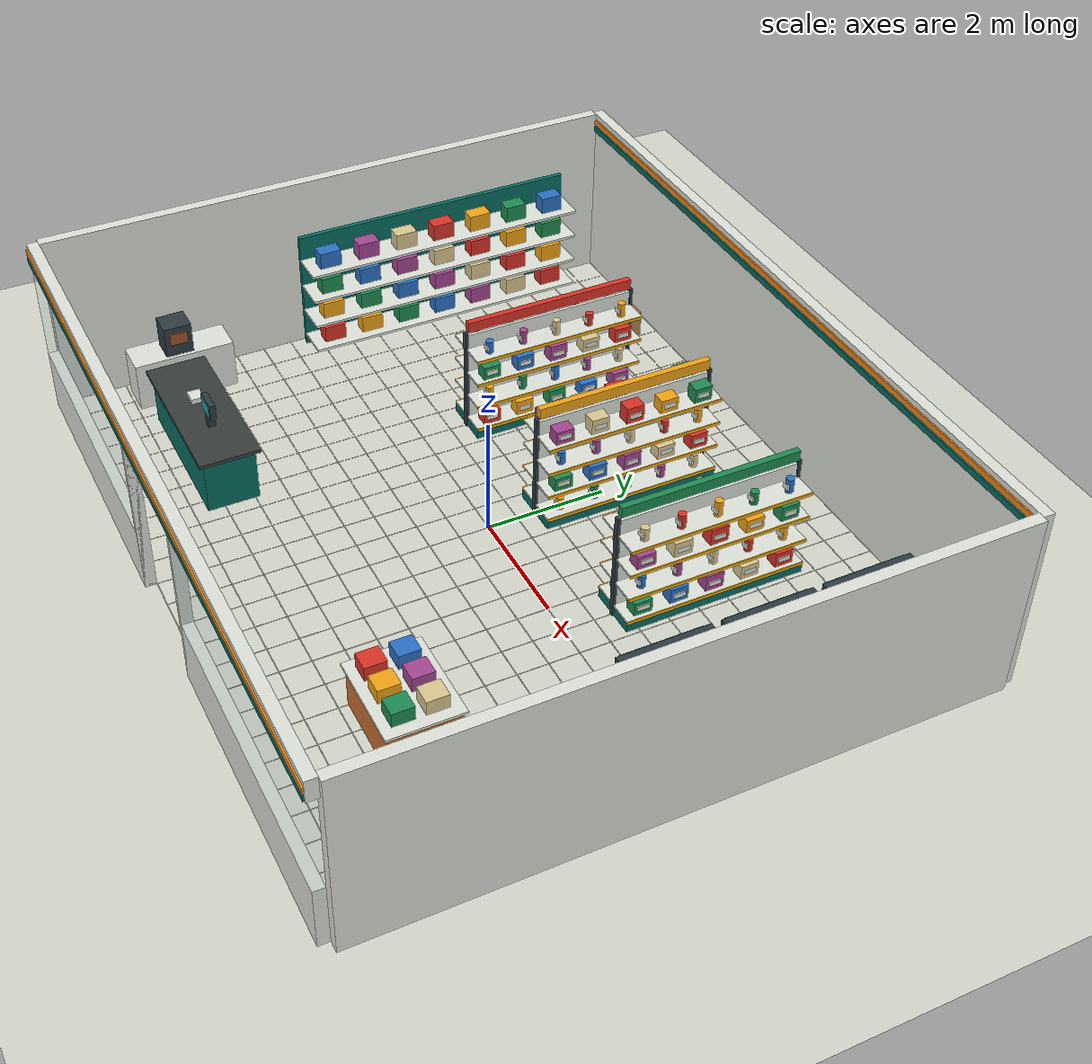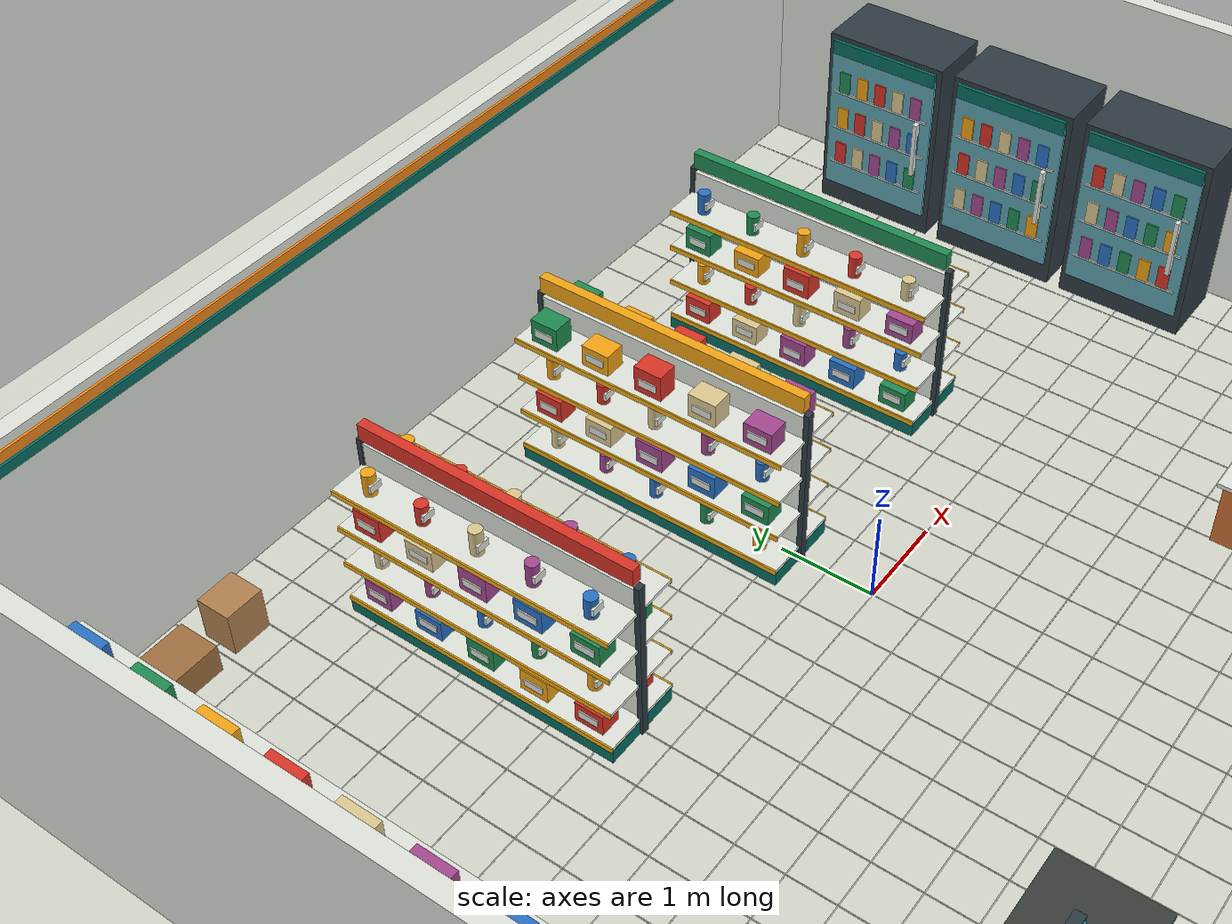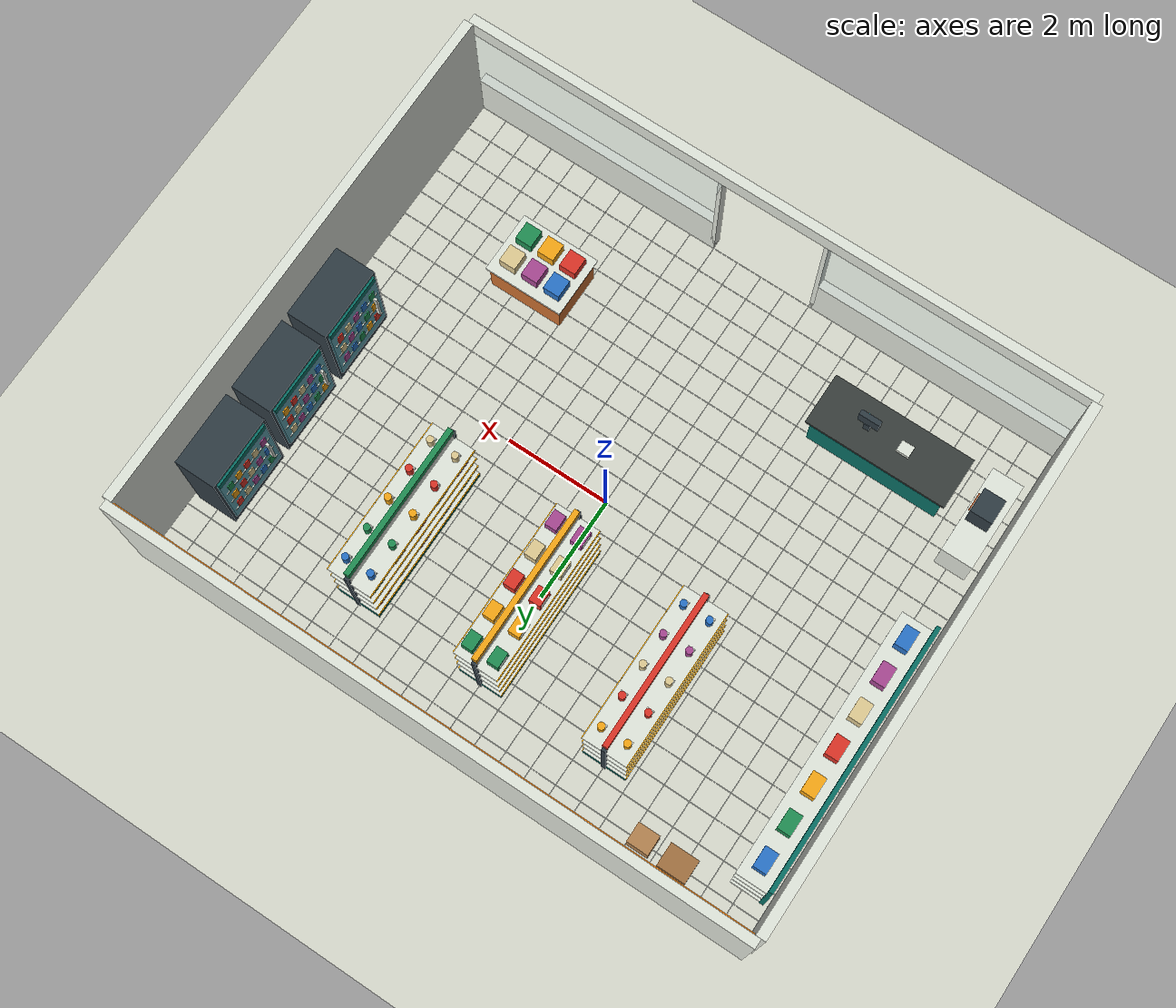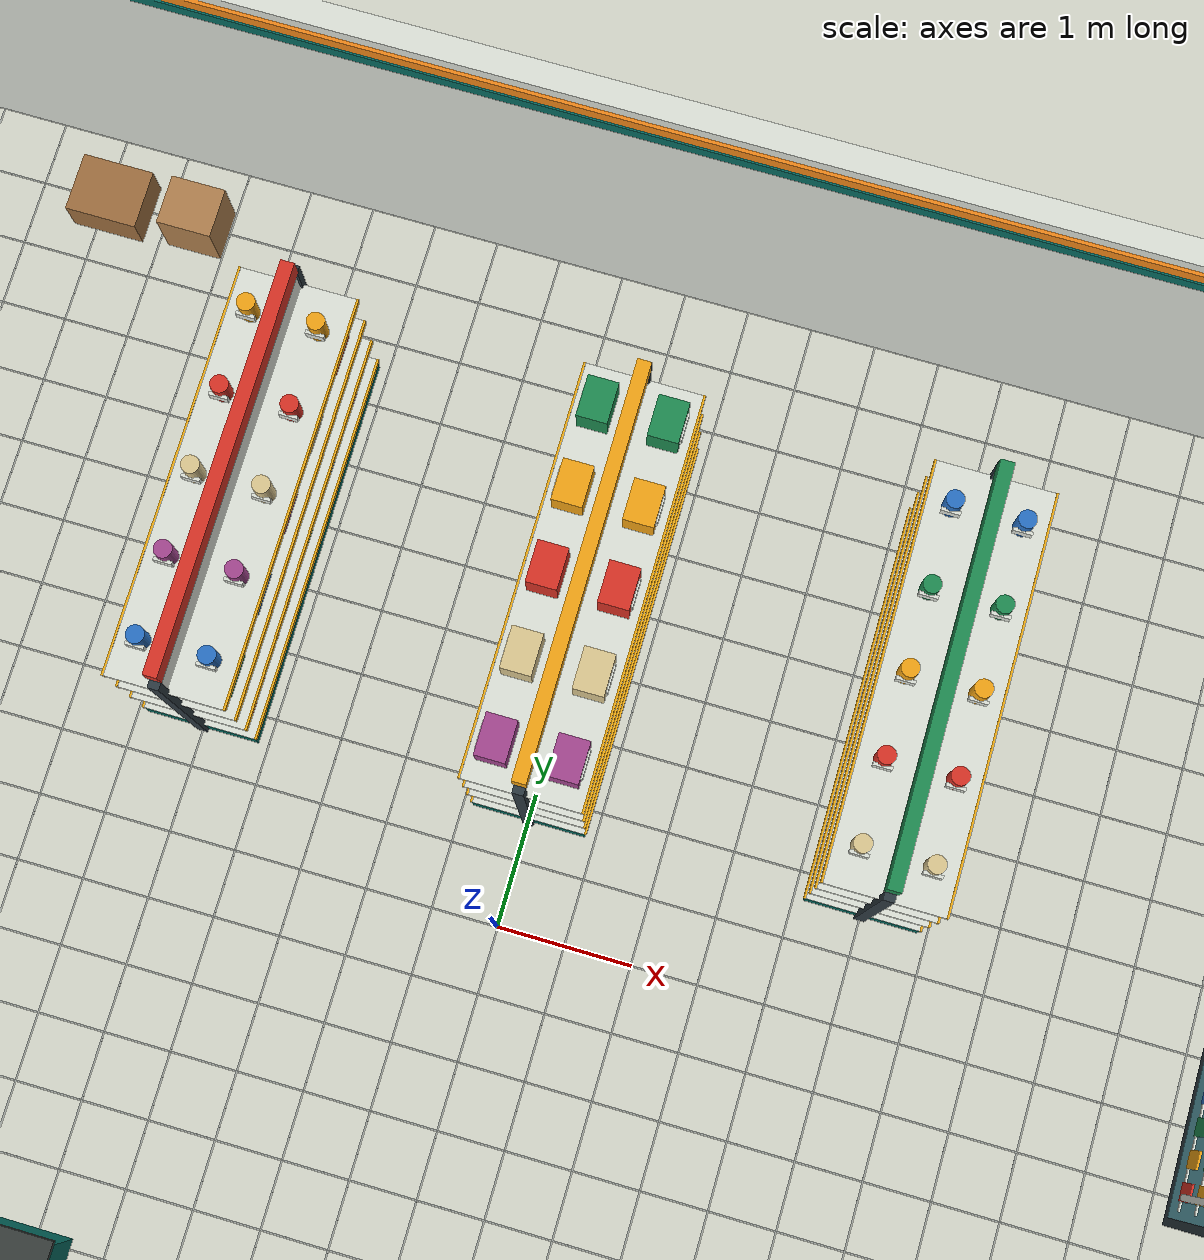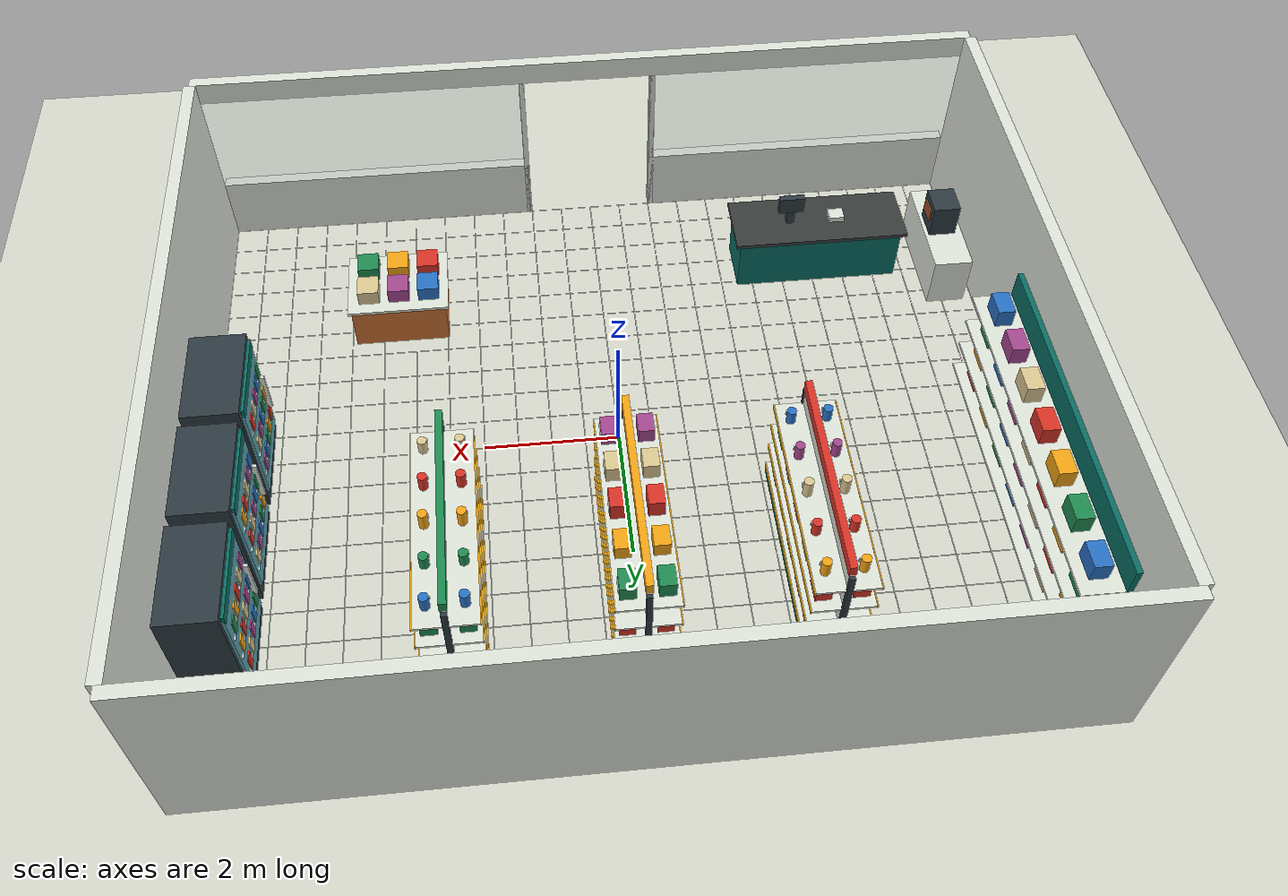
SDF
<sdf version="1.6">
  <world name="convenience_store">
    <physics name="ode_physics" default="1" type="ode">
      <max_step_size>0.001</max_step_size>
      <real_time_update_rate>1000.0</real_time_update_rate>
      <real_time_factor>1.0</real_time_factor>
      <ode>
        <solver>
          <type>quick</type>
          <iters>100</iters>
          <sor>1.3</sor>
        </solver>
      </ode>
    </physics>
    <gravity>0 0 -9.81</gravity>
    <light name="sun" type="directional">
      <cast_shadows>true</cast_shadows>
      <pose>0 0 10 0 0 0</pose>
      <diffuse>0.8 0.8 0.8 1</diffuse>
      <specular>0.2 0.2 0.2 1</specular>
      <attenuation>
        <range>1000</range>
        <constant>0.9</constant>
        <linear>0.01</linear>
        <quadratic>0.001</quadratic>
      </attenuation>
      <direction>-0.5 0.1 -0.9</direction>
    </light>
    <model name="ground_plane">
      <static>true</static>
      <link name="ground_link">
        <collision name="ground_collision">
          <geometry>
            <plane>
              <normal>0 0 1</normal>
              <size>100 100</size>
            </plane>
          </geometry>
          <surface>
            <friction>
              <ode>
                <mu>1.0</mu>
                <mu2>1.0</mu2>
              </ode>
            </friction>
          </surface>
        </collision>
        <visual name="ground_visual">
          <geometry>
            <plane>
              <normal>0 0 1</normal>
              <size>100 100</size>
            </plane>
          </geometry>
          <material>
            <ambient>.84 .85 .80 1</ambient>
            <diffuse>.84 .85 .80 1</diffuse>
          </material>
        </visual>
      </link>
    </model>
    <scene>
      <ambient>0.4 0.4 0.4 1</ambient>
      <background>.83 .88 .92 1</background>
      <shadows>true</shadows>
    </scene>
    <gui>
      <camera name="air_camera">
        <pose>10 -13 11 0 .60 2.22</pose>
        <view_controller>orbit</view_controller>
      </camera>
    </gui>
    <plugin name="gazebo_truth" filename="libgazebo_ros_state.so">
      <ros>
        <namespace>/gazebo</namespace>
      </ros>
      <update_rate>50.0</update_rate>
    </plugin>
    <model name="store_wall_north">
      <static>true</static>
      <pose>0 5.09 1.55 0 0 0</pose>
      <link name="body">
        <collision name="body_collision">
          <geometry>
            <box>
              <size>12.2 0.18 3.1</size>
            </box>
          </geometry>
          <surface>
            <friction>
              <ode>
                <mu>.8</mu>
                <mu2>.8</mu2>
              </ode>
            </friction>
          </surface>
        </collision>
        <visual name="body_visual">
          <geometry>
            <box>
              <size>12.2 0.18 3.1</size>
            </box>
          </geometry>
          <material>
            <ambient>.88 .90 .86 1</ambient>
            <diffuse>.88 .90 .86 1</diffuse>
          </material>
        </visual>
      </link>
    </model>
    <model name="store_wall_west">
      <static>true</static>
      <pose>-6.09 0 1.55 0 0 0</pose>
      <link name="body">
        <collision name="body_collision">
          <geometry>
            <box>
              <size>0.18 10 3.1</size>
            </box>
          </geometry>
          <surface>
            <friction>
              <ode>
                <mu>.8</mu>
                <mu2>.8</mu2>
              </ode>
            </friction>
          </surface>
        </collision>
        <visual name="body_visual">
          <geometry>
            <box>
              <size>0.18 10 3.1</size>
            </box>
          </geometry>
          <material>
            <ambient>.88 .90 .86 1</ambient>
            <diffuse>.88 .90 .86 1</diffuse>
          </material>
        </visual>
      </link>
    </model>
    <model name="store_wall_east">
      <static>true</static>
      <pose>6.09 0 1.55 0 0 0</pose>
      <link name="body">
        <collision name="body_collision">
          <geometry>
            <box>
              <size>0.18 10 3.1</size>
            </box>
          </geometry>
          <surface>
            <friction>
              <ode>
                <mu>.8</mu>
                <mu2>.8</mu2>
              </ode>
            </friction>
          </surface>
        </collision>
        <visual name="body_visual">
          <geometry>
            <box>
              <size>0.18 10 3.1</size>
            </box>
          </geometry>
          <material>
            <ambient>.88 .90 .86 1</ambient>
            <diffuse>.88 .90 .86 1</diffuse>
          </material>
        </visual>
      </link>
    </model>
    <model name="store_wall_front_left">
      <static>true</static>
      <pose>-3.5 -5.09 0.525 0 0 0</pose>
      <link name="body">
        <collision name="body_collision">
          <geometry>
            <box>
              <size>5 0.18 1.05</size>
            </box>
          </geometry>
          <surface>
            <friction>
              <ode>
                <mu>.8</mu>
                <mu2>.8</mu2>
              </ode>
            </friction>
          </surface>
        </collision>
        <visual name="body_visual">
          <geometry>
            <box>
              <size>5 0.18 1.05</size>
            </box>
          </geometry>
          <material>
            <ambient>.88 .90 .86 1</ambient>
            <diffuse>.88 .90 .86 1</diffuse>
          </material>
        </visual>
      </link>
    </model>
    <model name="store_wall_front_right">
      <static>true</static>
      <pose>3.5 -5.09 0.525 0 0 0</pose>
      <link name="body">
        <collision name="body_collision">
          <geometry>
            <box>
              <size>5 0.18 1.05</size>
            </box>
          </geometry>
          <surface>
            <friction>
              <ode>
                <mu>.8</mu>
                <mu2>.8</mu2>
              </ode>
            </friction>
          </surface>
        </collision>
        <visual name="body_visual">
          <geometry>
            <box>
              <size>5 0.18 1.05</size>
            </box>
          </geometry>
          <material>
            <ambient>.88 .90 .86 1</ambient>
            <diffuse>.88 .90 .86 1</diffuse>
          </material>
        </visual>
      </link>
    </model>
    <model name="store_wall_entry_header">
      <static>true</static>
      <pose>0 -5.09 2.925 0 0 0</pose>
      <link name="body">
        <collision name="body_collision">
          <geometry>
            <box>
              <size>12.2 0.18 0.35</size>
            </box>
          </geometry>
          <surface>
            <friction>
              <ode>
                <mu>.8</mu>
                <mu2>.8</mu2>
              </ode>
            </friction>
          </surface>
        </collision>
        <visual name="body_visual">
          <geometry>
            <box>
              <size>12.2 0.18 0.35</size>
            </box>
          </geometry>
          <material>
            <ambient>.88 .90 .86 1</ambient>
            <diffuse>.88 .90 .86 1</diffuse>
          </material>
        </visual>
      </link>
    </model>
    <model name="store_wall_entry_post_left">
      <static>true</static>
      <pose>-1.04 -5.09 1.375 0 0 0</pose>
      <link name="body">
        <collision name="body_collision">
          <geometry>
            <box>
              <size>0.08 0.18 2.75</size>
            </box>
          </geometry>
          <surface>
            <friction>
              <ode>
                <mu>.8</mu>
                <mu2>.8</mu2>
              </ode>
            </friction>
          </surface>
        </collision>
        <visual name="body_visual">
          <geometry>
            <box>
              <size>0.08 0.18 2.75</size>
            </box>
          </geometry>
          <material>
            <ambient>.88 .90 .86 1</ambient>
            <diffuse>.88 .90 .86 1</diffuse>
          </material>
        </visual>
      </link>
    </model>
    <model name="store_wall_entry_post_right">
      <static>true</static>
      <pose>1.04 -5.09 1.375 0 0 0</pose>
      <link name="body">
        <collision name="body_collision">
          <geometry>
            <box>
              <size>0.08 0.18 2.75</size>
            </box>
          </geometry>
          <surface>
            <friction>
              <ode>
                <mu>.8</mu>
                <mu2>.8</mu2>
              </ode>
            </friction>
          </surface>
        </collision>
        <visual name="body_visual">
          <geometry>
            <box>
              <size>0.08 0.18 2.75</size>
            </box>
          </geometry>
          <material>
            <ambient>.88 .90 .86 1</ambient>
            <diffuse>.88 .90 .86 1</diffuse>
          </material>
        </visual>
      </link>
    </model>
    <model name="store_ceiling">
      <static>true</static>
      <pose>0 0 3.16 0 0 0</pose>
      <link name="body">
        <collision name="body_collision">
          <geometry>
            <box>
              <size>12.0 10.0 0.12</size>
            </box>
          </geometry>
          <surface>
            <friction>
              <ode>
                <mu>.8</mu>
                <mu2>.8</mu2>
              </ode>
            </friction>
          </surface>
        </collision>
      </link>
    </model>
    <model name="store_front_upper_left">
      <static>true</static>
      <pose>-3.5 -5.09 1.9 0 0 0</pose>
      <link name="body">
        <collision name="body_collision">
          <geometry>
            <box>
              <size>5.0 0.18 1.7</size>
            </box>
          </geometry>
          <surface>
            <friction>
              <ode>
                <mu>.8</mu>
                <mu2>.8</mu2>
              </ode>
            </friction>
          </surface>
        </collision>
        <visual name="body_visual">
          <transparency>0.82</transparency>
          <geometry>
            <box>
              <size>5.0 0.18 1.7</size>
            </box>
          </geometry>
          <material>
            <ambient>.65 .78 .80 1</ambient>
            <diffuse>.65 .78 .80 1</diffuse>
          </material>
        </visual>
      </link>
    </model>
    <model name="store_front_upper_right">
      <static>true</static>
      <pose>3.5 -5.09 1.9 0 0 0</pose>
      <link name="body">
        <collision name="body_collision">
          <geometry>
            <box>
              <size>5.0 0.18 1.7</size>
            </box>
          </geometry>
          <surface>
            <friction>
              <ode>
                <mu>.8</mu>
                <mu2>.8</mu2>
              </ode>
            </friction>
          </surface>
        </collision>
        <visual name="body_visual">
          <transparency>0.82</transparency>
          <geometry>
            <box>
              <size>5.0 0.18 1.7</size>
            </box>
          </geometry>
          <material>
            <ambient>.65 .78 .80 1</ambient>
            <diffuse>.65 .78 .80 1</diffuse>
          </material>
        </visual>
      </link>
    </model>
    <model name="front_fascia_0">
      <static>true</static>
      <pose>0 -5.195 2.83 0 0 0</pose>
      <link name="body">
        <visual name="body_visual">
          <geometry>
            <box>
              <size>12.2 0.025 0.1</size>
            </box>
          </geometry>
          <material>
            <ambient>.03 .43 .39 1</ambient>
            <diffuse>.03 .43 .39 1</diffuse>
          </material>
        </visual>
      </link>
    </model>
    <model name="back_fascia_0">
      <static>true</static>
      <pose>0 4.985 2.83 0 0 0</pose>
      <link name="body">
        <visual name="body_visual">
          <geometry>
            <box>
              <size>11.98 0.025 0.1</size>
            </box>
          </geometry>
          <material>
            <ambient>.03 .43 .39 1</ambient>
            <diffuse>.03 .43 .39 1</diffuse>
          </material>
        </visual>
      </link>
    </model>
    <model name="front_fascia_1">
      <static>true</static>
      <pose>0 -5.195 2.96 0 0 0</pose>
      <link name="body">
        <visual name="body_visual">
          <geometry>
            <box>
              <size>12.2 0.025 0.1</size>
            </box>
          </geometry>
          <material>
            <ambient>.96 .54 .10 1</ambient>
            <diffuse>.96 .54 .10 1</diffuse>
          </material>
        </visual>
      </link>
    </model>
    <model name="back_fascia_1">
      <static>true</static>
      <pose>0 4.985 2.96 0 0 0</pose>
      <link name="body">
        <visual name="body_visual">
          <geometry>
            <box>
              <size>11.98 0.025 0.1</size>
            </box>
          </geometry>
          <material>
            <ambient>.96 .54 .10 1</ambient>
            <diffuse>.96 .54 .10 1</diffuse>
          </material>
        </visual>
      </link>
    </model>
    <model name="tile_x_0">
      <static>true</static>
      <pose>-6.0 0 0.001 0 0 0</pose>
      <link name="body">
        <visual name="body_visual">
          <geometry>
            <box>
              <size>0.012 10 0.001</size>
            </box>
          </geometry>
          <material>
            <ambient>.63 .65 .63 1</ambient>
            <diffuse>.63 .65 .63 1</diffuse>
          </material>
        </visual>
      </link>
    </model>
    <model name="tile_x_1">
      <static>true</static>
      <pose>-5.5 0 0.001 0 0 0</pose>
      <link name="body">
        <visual name="body_visual">
          <geometry>
            <box>
              <size>0.012 10 0.001</size>
            </box>
          </geometry>
          <material>
            <ambient>.63 .65 .63 1</ambient>
            <diffuse>.63 .65 .63 1</diffuse>
          </material>
        </visual>
      </link>
    </model>
    <model name="tile_x_2">
      <static>true</static>
      <pose>-5.0 0 0.001 0 0 0</pose>
      <link name="body">
        <visual name="body_visual">
          <geometry>
            <box>
              <size>0.012 10 0.001</size>
            </box>
          </geometry>
          <material>
            <ambient>.63 .65 .63 1</ambient>
            <diffuse>.63 .65 .63 1</diffuse>
          </material>
        </visual>
      </link>
    </model>
    <model name="tile_x_3">
      <static>true</static>
      <pose>-4.5 0 0.001 0 0 0</pose>
      <link name="body">
        <visual name="body_visual">
          <geometry>
            <box>
              <size>0.012 10 0.001</size>
            </box>
          </geometry>
          <material>
            <ambient>.63 .65 .63 1</ambient>
            <diffuse>.63 .65 .63 1</diffuse>
          </material>
        </visual>
      </link>
    </model>
    <model name="tile_x_4">
      <static>true</static>
      <pose>-4.0 0 0.001 0 0 0</pose>
      <link name="body">
        <visual name="body_visual">
          <geometry>
            <box>
              <size>0.012 10 0.001</size>
            </box>
          </geometry>
          <material>
            <ambient>.63 .65 .63 1</ambient>
            <diffuse>.63 .65 .63 1</diffuse>
          </material>
        </visual>
      </link>
    </model>
    <model name="tile_x_5">
      <static>true</static>
      <pose>-3.5 0 0.001 0 0 0</pose>
      <link name="body">
        <visual name="body_visual">
          <geometry>
            <box>
              <size>0.012 10 0.001</size>
            </box>
          </geometry>
          <material>
            <ambient>.63 .65 .63 1</ambient>
            <diffuse>.63 .65 .63 1</diffuse>
          </material>
        </visual>
      </link>
    </model>
    <model name="tile_x_6">
      <static>true</static>
      <pose>-3.0 0 0.001 0 0 0</pose>
      <link name="body">
        <visual name="body_visual">
          <geometry>
            <box>
              <size>0.012 10 0.001</size>
            </box>
          </geometry>
          <material>
            <ambient>.63 .65 .63 1</ambient>
            <diffuse>.63 .65 .63 1</diffuse>
          </material>
        </visual>
      </link>
    </model>
    <model name="tile_x_7">
      <static>true</static>
      <pose>-2.5 0 0.001 0 0 0</pose>
      <link name="body">
        <visual name="body_visual">
          <geometry>
            <box>
              <size>0.012 10 0.001</size>
            </box>
          </geometry>
          <material>
            <ambient>.63 .65 .63 1</ambient>
            <diffuse>.63 .65 .63 1</diffuse>
          </material>
        </visual>
      </link>
    </model>
    <model name="tile_x_8">
      <static>true</static>
      <pose>-2.0 0 0.001 0 0 0</pose>
      <link name="body">
        <visual name="body_visual">
          <geometry>
            <box>
              <size>0.012 10 0.001</size>
            </box>
          </geometry>
          <material>
            <ambient>.63 .65 .63 1</ambient>
            <diffuse>.63 .65 .63 1</diffuse>
          </material>
        </visual>
      </link>
    </model>
    <model name="tile_x_9">
      <static>true</static>
      <pose>-1.5 0 0.001 0 0 0</pose>
      <link name="body">
        <visual name="body_visual">
          <geometry>
            <box>
              <size>0.012 10 0.001</size>
            </box>
          </geometry>
          <material>
            <ambient>.63 .65 .63 1</ambient>
            <diffuse>.63 .65 .63 1</diffuse>
          </material>
        </visual>
      </link>
    </model>
    <model name="tile_x_10">
      <static>true</static>
      <pose>-1.0 0 0.001 0 0 0</pose>
      <link name="body">
        <visual name="body_visual">
          <geometry>
            <box>
              <size>0.012 10 0.001</size>
            </box>
          </geometry>
          <material>
            <ambient>.63 .65 .63 1</ambient>
            <diffuse>.63 .65 .63 1</diffuse>
          </material>
        </visual>
      </link>
    </model>
    <model name="tile_x_11">
      <static>true</static>
      <pose>-0.5 0 0.001 0 0 0</pose>
      <link name="body">
        <visual name="body_visual">
          <geometry>
            <box>
              <size>0.012 10 0.001</size>
            </box>
          </geometry>
          <material>
            <ambient>.63 .65 .63 1</ambient>
            <diffuse>.63 .65 .63 1</diffuse>
          </material>
        </visual>
      </link>
    </model>
    <model name="tile_x_12">
      <static>true</static>
      <pose>0.0 0 0.001 0 0 0</pose>
      <link name="body">
        <visual name="body_visual">
          <geometry>
            <box>
              <size>0.012 10 0.001</size>
            </box>
          </geometry>
          <material>
            <ambient>.63 .65 .63 1</ambient>
            <diffuse>.63 .65 .63 1</diffuse>
          </material>
        </visual>
      </link>
    </model>
    <model name="tile_x_13">
      <static>true</static>
      <pose>0.5 0 0.001 0 0 0</pose>
      <link name="body">
        <visual name="body_visual">
          <geometry>
            <box>
              <size>0.012 10 0.001</size>
            </box>
          </geometry>
          <material>
            <ambient>.63 .65 .63 1</ambient>
            <diffuse>.63 .65 .63 1</diffuse>
          </material>
        </visual>
      </link>
    </model>
    <model name="tile_x_14">
      <static>true</static>
      <pose>1.0 0 0.001 0 0 0</pose>
      <link name="body">
        <visual name="body_visual">
          <geometry>
            <box>
              <size>0.012 10 0.001</size>
            </box>
          </geometry>
          <material>
            <ambient>.63 .65 .63 1</ambient>
            <diffuse>.63 .65 .63 1</diffuse>
          </material>
        </visual>
      </link>
    </model>
    <model name="tile_x_15">
      <static>true</static>
      <pose>1.5 0 0.001 0 0 0</pose>
      <link name="body">
        <visual name="body_visual">
          <geometry>
            <box>
              <size>0.012 10 0.001</size>
            </box>
          </geometry>
          <material>
            <ambient>.63 .65 .63 1</ambient>
            <diffuse>.63 .65 .63 1</diffuse>
          </material>
        </visual>
      </link>
    </model>
    <model name="tile_x_16">
      <static>true</static>
      <pose>2.0 0 0.001 0 0 0</pose>
      <link name="body">
        <visual name="body_visual">
          <geometry>
            <box>
              <size>0.012 10 0.001</size>
            </box>
          </geometry>
          <material>
            <ambient>.63 .65 .63 1</ambient>
            <diffuse>.63 .65 .63 1</diffuse>
          </material>
        </visual>
      </link>
    </model>
    <model name="tile_x_17">
      <static>true</static>
      <pose>2.5 0 0.001 0 0 0</pose>
      <link name="body">
        <visual name="body_visual">
          <geometry>
            <box>
              <size>0.012 10 0.001</size>
            </box>
          </geometry>
          <material>
            <ambient>.63 .65 .63 1</ambient>
            <diffuse>.63 .65 .63 1</diffuse>
          </material>
        </visual>
      </link>
    </model>
    <model name="tile_x_18">
      <static>true</static>
      <pose>3.0 0 0.001 0 0 0</pose>
      <link name="body">
        <visual name="body_visual">
          <geometry>
            <box>
              <size>0.012 10 0.001</size>
            </box>
          </geometry>
          <material>
            <ambient>.63 .65 .63 1</ambient>
            <diffuse>.63 .65 .63 1</diffuse>
          </material>
        </visual>
      </link>
    </model>
    <model name="tile_x_19">
      <static>true</static>
      <pose>3.5 0 0.001 0 0 0</pose>
      <link name="body">
        <visual name="body_visual">
          <geometry>
            <box>
              <size>0.012 10 0.001</size>
            </box>
          </geometry>
          <material>
            <ambient>.63 .65 .63 1</ambient>
            <diffuse>.63 .65 .63 1</diffuse>
          </material>
        </visual>
      </link>
    </model>
    <model name="tile_x_20">
      <static>true</static>
      <pose>4.0 0 0.001 0 0 0</pose>
      <link name="body">
        <visual name="body_visual">
          <geometry>
            <box>
              <size>0.012 10 0.001</size>
            </box>
          </geometry>
          <material>
            <ambient>.63 .65 .63 1</ambient>
            <diffuse>.63 .65 .63 1</diffuse>
          </material>
        </visual>
      </link>
    </model>
    <model name="tile_x_21">
      <static>true</static>
      <pose>4.5 0 0.001 0 0 0</pose>
      <link name="body">
        <visual name="body_visual">
          <geometry>
            <box>
              <size>0.012 10 0.001</size>
            </box>
          </geometry>
          <material>
            <ambient>.63 .65 .63 1</ambient>
            <diffuse>.63 .65 .63 1</diffuse>
          </material>
        </visual>
      </link>
    </model>
    <model name="tile_x_22">
      <static>true</static>
      <pose>5.0 0 0.001 0 0 0</pose>
      <link name="body">
        <visual name="body_visual">
          <geometry>
            <box>
              <size>0.012 10 0.001</size>
            </box>
          </geometry>
          <material>
            <ambient>.63 .65 .63 1</ambient>
            <diffuse>.63 .65 .63 1</diffuse>
          </material>
        </visual>
      </link>
    </model>
    <model name="tile_x_23">
      <static>true</static>
      <pose>5.5 0 0.001 0 0 0</pose>
      <link name="body">
        <visual name="body_visual">
          <geometry>
            <box>
              <size>0.012 10 0.001</size>
            </box>
          </geometry>
          <material>
            <ambient>.63 .65 .63 1</ambient>
            <diffuse>.63 .65 .63 1</diffuse>
          </material>
        </visual>
      </link>
    </model>
    <model name="tile_x_24">
      <static>true</static>
      <pose>6.0 0 0.001 0 0 0</pose>
      <link name="body">
        <visual name="body_visual">
          <geometry>
            <box>
              <size>0.012 10 0.001</size>
            </box>
          </geometry>
          <material>
            <ambient>.63 .65 .63 1</ambient>
            <diffuse>.63 .65 .63 1</diffuse>
          </material>
        </visual>
      </link>
    </model>
    <model name="tile_y_0">
      <static>true</static>
      <pose>0 -5.0 0.001 0 0 0</pose>
      <link name="body">
        <visual name="body_visual">
          <geometry>
            <box>
              <size>12 0.012 0.001</size>
            </box>
          </geometry>
          <material>
            <ambient>.63 .65 .63 1</ambient>
            <diffuse>.63 .65 .63 1</diffuse>
          </material>
        </visual>
      </link>
    </model>
    <model name="tile_y_1">
      <static>true</static>
      <pose>0 -4.5 0.001 0 0 0</pose>
      <link name="body">
        <visual name="body_visual">
          <geometry>
            <box>
              <size>12 0.012 0.001</size>
            </box>
          </geometry>
          <material>
            <ambient>.63 .65 .63 1</ambient>
            <diffuse>.63 .65 .63 1</diffuse>
          </material>
        </visual>
      </link>
    </model>
    <model name="tile_y_2">
      <static>true</static>
      <pose>0 -4.0 0.001 0 0 0</pose>
      <link name="body">
        <visual name="body_visual">
          <geometry>
            <box>
              <size>12 0.012 0.001</size>
            </box>
          </geometry>
          <material>
            <ambient>.63 .65 .63 1</ambient>
            <diffuse>.63 .65 .63 1</diffuse>
          </material>
        </visual>
      </link>
    </model>
    <model name="tile_y_3">
      <static>true</static>
      <pose>0 -3.5 0.001 0 0 0</pose>
      <link name="body">
        <visual name="body_visual">
          <geometry>
            <box>
              <size>12 0.012 0.001</size>
            </box>
          </geometry>
          <material>
            <ambient>.63 .65 .63 1</ambient>
            <diffuse>.63 .65 .63 1</diffuse>
          </material>
        </visual>
      </link>
    </model>
    <model name="tile_y_4">
      <static>true</static>
      <pose>0 -3.0 0.001 0 0 0</pose>
      <link name="body">
        <visual name="body_visual">
          <geometry>
            <box>
              <size>12 0.012 0.001</size>
            </box>
          </geometry>
          <material>
            <ambient>.63 .65 .63 1</ambient>
            <diffuse>.63 .65 .63 1</diffuse>
          </material>
        </visual>
      </link>
    </model>
    <model name="tile_y_5">
      <static>true</static>
      <pose>0 -2.5 0.001 0 0 0</pose>
      <link name="body">
        <visual name="body_visual">
          <geometry>
            <box>
              <size>12 0.012 0.001</size>
            </box>
          </geometry>
          <material>
            <ambient>.63 .65 .63 1</ambient>
            <diffuse>.63 .65 .63 1</diffuse>
          </material>
        </visual>
      </link>
    </model>
    <model name="tile_y_6">
      <static>true</static>
      <pose>0 -2.0 0.001 0 0 0</pose>
      <link name="body">
        <visual name="body_visual">
          <geometry>
            <box>
              <size>12 0.012 0.001</size>
            </box>
          </geometry>
          <material>
            <ambient>.63 .65 .63 1</ambient>
            <diffuse>.63 .65 .63 1</diffuse>
          </material>
        </visual>
      </link>
    </model>
    <model name="tile_y_7">
      <static>true</static>
      <pose>0 -1.5 0.001 0 0 0</pose>
      <link name="body">
        <visual name="body_visual">
          <geometry>
            <box>
              <size>12 0.012 0.001</size>
            </box>
          </geometry>
          <material>
            <ambient>.63 .65 .63 1</ambient>
            <diffuse>.63 .65 .63 1</diffuse>
          </material>
        </visual>
      </link>
    </model>
    <model name="tile_y_8">
      <static>true</static>
      <pose>0 -1.0 0.001 0 0 0</pose>
      <link name="body">
        <visual name="body_visual">
          <geometry>
            <box>
              <size>12 0.012 0.001</size>
            </box>
          </geometry>
          <material>
            <ambient>.63 .65 .63 1</ambient>
            <diffuse>.63 .65 .63 1</diffuse>
          </material>
        </visual>
      </link>
    </model>
    <model name="tile_y_9">
      <static>true</static>
      <pose>0 -0.5 0.001 0 0 0</pose>
      <link name="body">
        <visual name="body_visual">
          <geometry>
            <box>
              <size>12 0.012 0.001</size>
            </box>
          </geometry>
          <material>
            <ambient>.63 .65 .63 1</ambient>
            <diffuse>.63 .65 .63 1</diffuse>
          </material>
        </visual>
      </link>
    </model>
    <model name="tile_y_10">
      <static>true</static>
      <pose>0 0.0 0.001 0 0 0</pose>
      <link name="body">
        <visual name="body_visual">
          <geometry>
            <box>
              <size>12 0.012 0.001</size>
            </box>
          </geometry>
          <material>
            <ambient>.63 .65 .63 1</ambient>
            <diffuse>.63 .65 .63 1</diffuse>
          </material>
        </visual>
      </link>
    </model>
    <model name="tile_y_11">
      <static>true</static>
      <pose>0 0.5 0.001 0 0 0</pose>
      <link name="body">
        <visual name="body_visual">
          <geometry>
            <box>
              <size>12 0.012 0.001</size>
            </box>
          </geometry>
          <material>
            <ambient>.63 .65 .63 1</ambient>
            <diffuse>.63 .65 .63 1</diffuse>
          </material>
        </visual>
      </link>
    </model>
    <model name="tile_y_12">
      <static>true</static>
      <pose>0 1.0 0.001 0 0 0</pose>
      <link name="body">
        <visual name="body_visual">
          <geometry>
            <box>
              <size>12 0.012 0.001</size>
            </box>
          </geometry>
          <material>
            <ambient>.63 .65 .63 1</ambient>
            <diffuse>.63 .65 .63 1</diffuse>
          </material>
        </visual>
      </link>
    </model>
    <model name="tile_y_13">
      <static>true</static>
      <pose>0 1.5 0.001 0 0 0</pose>
      <link name="body">
        <visual name="body_visual">
          <geometry>
            <box>
              <size>12 0.012 0.001</size>
            </box>
          </geometry>
          <material>
            <ambient>.63 .65 .63 1</ambient>
            <diffuse>.63 .65 .63 1</diffuse>
          </material>
        </visual>
      </link>
    </model>
    <model name="tile_y_14">
      <static>true</static>
      <pose>0 2.0 0.001 0 0 0</pose>
      <link name="body">
        <visual name="body_visual">
          <geometry>
            <box>
              <size>12 0.012 0.001</size>
            </box>
          </geometry>
          <material>
            <ambient>.63 .65 .63 1</ambient>
            <diffuse>.63 .65 .63 1</diffuse>
          </material>
        </visual>
      </link>
    </model>
    <model name="tile_y_15">
      <static>true</static>
      <pose>0 2.5 0.001 0 0 0</pose>
      <link name="body">
        <visual name="body_visual">
          <geometry>
            <box>
              <size>12 0.012 0.001</size>
            </box>
          </geometry>
          <material>
            <ambient>.63 .65 .63 1</ambient>
            <diffuse>.63 .65 .63 1</diffuse>
          </material>
        </visual>
      </link>
    </model>
    <model name="tile_y_16">
      <static>true</static>
      <pose>0 3.0 0.001 0 0 0</pose>
      <link name="body">
        <visual name="body_visual">
          <geometry>
            <box>
              <size>12 0.012 0.001</size>
            </box>
          </geometry>
          <material>
            <ambient>.63 .65 .63 1</ambient>
            <diffuse>.63 .65 .63 1</diffuse>
          </material>
        </visual>
      </link>
    </model>
    <model name="tile_y_17">
      <static>true</static>
      <pose>0 3.5 0.001 0 0 0</pose>
      <link name="body">
        <visual name="body_visual">
          <geometry>
            <box>
              <size>12 0.012 0.001</size>
            </box>
          </geometry>
          <material>
            <ambient>.63 .65 .63 1</ambient>
            <diffuse>.63 .65 .63 1</diffuse>
          </material>
        </visual>
      </link>
    </model>
    <model name="tile_y_18">
      <static>true</static>
      <pose>0 4.0 0.001 0 0 0</pose>
      <link name="body">
        <visual name="body_visual">
          <geometry>
            <box>
              <size>12 0.012 0.001</size>
            </box>
          </geometry>
          <material>
            <ambient>.63 .65 .63 1</ambient>
            <diffuse>.63 .65 .63 1</diffuse>
          </material>
        </visual>
      </link>
    </model>
    <model name="tile_y_19">
      <static>true</static>
      <pose>0 4.5 0.001 0 0 0</pose>
      <link name="body">
        <visual name="body_visual">
          <geometry>
            <box>
              <size>12 0.012 0.001</size>
            </box>
          </geometry>
          <material>
            <ambient>.63 .65 .63 1</ambient>
            <diffuse>.63 .65 .63 1</diffuse>
          </material>
        </visual>
      </link>
    </model>
    <model name="tile_y_20">
      <static>true</static>
      <pose>0 5.0 0.001 0 0 0</pose>
      <link name="body">
        <visual name="body_visual">
          <geometry>
            <box>
              <size>12 0.012 0.001</size>
            </box>
          </geometry>
          <material>
            <ambient>.63 .65 .63 1</ambient>
            <diffuse>.63 .65 .63 1</diffuse>
          </material>
        </visual>
      </link>
    </model>
    <model name="gondola_0_plinth">
      <static>true</static>
      <pose>-2.5 2.3 0.08 0 0 0</pose>
      <link name="body">
        <collision name="body_collision">
          <geometry>
            <box>
              <size>0.85 3.0 0.16</size>
            </box>
          </geometry>
          <surface>
            <friction>
              <ode>
                <mu>.8</mu>
                <mu2>.8</mu2>
              </ode>
            </friction>
          </surface>
        </collision>
        <visual name="body_visual">
          <geometry>
            <box>
              <size>0.85 3.0 0.16</size>
            </box>
          </geometry>
          <material>
            <ambient>.03 .43 .39 1</ambient>
            <diffuse>.03 .43 .39 1</diffuse>
          </material>
        </visual>
      </link>
    </model>
    <model name="gondola_0_divider">
      <static>true</static>
      <pose>-2.5 2.3 0.95 0 0 0</pose>
      <link name="body">
        <collision name="body_collision">
          <geometry>
            <box>
              <size>0.045 3.0 1.7</size>
            </box>
          </geometry>
          <surface>
            <friction>
              <ode>
                <mu>.8</mu>
                <mu2>.8</mu2>
              </ode>
            </friction>
          </surface>
        </collision>
        <visual name="body_visual">
          <geometry>
            <box>
              <size>0.045 3.0 1.7</size>
            </box>
          </geometry>
          <material>
            <ambient>.88 .90 .86 1</ambient>
            <diffuse>.88 .90 .86 1</diffuse>
          </material>
        </visual>
      </link>
    </model>
    <model name="gondola_0_end_0">
      <static>true</static>
      <pose>-2.5 0.7999999999999998 0.925 0 0 0</pose>
      <link name="body">
        <collision name="body_collision">
          <geometry>
            <box>
              <size>0.08 0.055 1.85</size>
            </box>
          </geometry>
          <surface>
            <friction>
              <ode>
                <mu>.8</mu>
                <mu2>.8</mu2>
              </ode>
            </friction>
          </surface>
        </collision>
        <visual name="body_visual">
          <geometry>
            <box>
              <size>0.08 0.055 1.85</size>
            </box>
          </geometry>
          <material>
            <ambient>.18 .23 .26 1</ambient>
            <diffuse>.18 .23 .26 1</diffuse>
          </material>
        </visual>
      </link>
    </model>
    <model name="gondola_0_end_1">
      <static>true</static>
      <pose>-2.5 3.8 0.925 0 0 0</pose>
      <link name="body">
        <collision name="body_collision">
          <geometry>
            <box>
              <size>0.08 0.055 1.85</size>
            </box>
          </geometry>
          <surface>
            <friction>
              <ode>
                <mu>.8</mu>
                <mu2>.8</mu2>
              </ode>
            </friction>
          </surface>
        </collision>
        <visual name="body_visual">
          <geometry>
            <box>
              <size>0.08 0.055 1.85</size>
            </box>
          </geometry>
          <material>
            <ambient>.18 .23 .26 1</ambient>
            <diffuse>.18 .23 .26 1</diffuse>
          </material>
        </visual>
      </link>
    </model>
    <model name="gondola_0_shelf_0">
      <static>true</static>
      <pose>-2.5 2.3 0.1825 0 0 0</pose>
      <link name="body">
        <collision name="body_collision">
          <geometry>
            <box>
              <size>0.85 3.0 0.035</size>
            </box>
          </geometry>
          <surface>
            <friction>
              <ode>
                <mu>.8</mu>
                <mu2>.8</mu2>
              </ode>
            </friction>
          </surface>
        </collision>
        <visual name="body_visual">
          <geometry>
            <box>
              <size>0.85 3.0 0.035</size>
            </box>
          </geometry>
          <material>
            <ambient>.88 .90 .86 1</ambient>
            <diffuse>.88 .90 .86 1</diffuse>
          </material>
        </visual>
      </link>
    </model>
    <model name="gondola_0_price_0_-1">
      <static>true</static>
      <pose>-2.93 2.3 0.17500000000000002 0 0 0</pose>
      <link name="body">
        <visual name="body_visual">
          <geometry>
            <box>
              <size>0.016 3.0 0.055</size>
            </box>
          </geometry>
          <material>
            <ambient>.95 .68 .08 1</ambient>
            <diffuse>.95 .68 .08 1</diffuse>
          </material>
        </visual>
      </link>
    </model>
    <model name="gondola_0_goods_0_-1_0">
      <static>true</static>
      <pose>-2.75 1.0999999999999999 0.315 0 0 0</pose>
      <link name="body">
        <collision name="body_collision">
          <geometry>
            <box>
              <size>0.22 0.3 0.23</size>
            </box>
          </geometry>
          <surface>
            <friction>
              <ode>
                <mu>.8</mu>
                <mu2>.8</mu2>
              </ode>
            </friction>
          </surface>
        </collision>
        <visual name="body_visual">
          <geometry>
            <box>
              <size>0.22 0.3 0.23</size>
            </box>
          </geometry>
          <material>
            <ambient>.86 .20 .15 1</ambient>
            <diffuse>.86 .20 .15 1</diffuse>
          </material>
        </visual>
      </link>
    </model>
    <model name="gondola_0_goods_0_-1_0_label">
      <static>true</static>
      <pose>-2.866 1.0999999999999999 0.32 0 0 0</pose>
      <link name="body">
        <visual name="body_visual">
          <geometry>
            <box>
              <size>0.012 0.2 0.08</size>
            </box>
          </geometry>
          <material>
            <ambient>.88 .90 .86 1</ambient>
            <diffuse>.88 .90 .86 1</diffuse>
          </material>
        </visual>
      </link>
    </model>
    <model name="gondola_0_goods_0_-1_1">
      <static>true</static>
      <pose>-2.75 1.6999999999999997 0.3275 0 0 0</pose>
      <link name="body">
        <collision name="body_collision">
          <geometry>
            <box>
              <size>0.22 0.3 0.255</size>
            </box>
          </geometry>
          <surface>
            <friction>
              <ode>
                <mu>.8</mu>
                <mu2>.8</mu2>
              </ode>
            </friction>
          </surface>
        </collision>
        <visual name="body_visual">
          <geometry>
            <box>
              <size>0.22 0.3 0.255</size>
            </box>
          </geometry>
          <material>
            <ambient>.96 .65 .08 1</ambient>
            <diffuse>.96 .65 .08 1</diffuse>
          </material>
        </visual>
      </link>
    </model>
    <model name="gondola_0_goods_0_-1_1_label">
      <static>true</static>
      <pose>-2.866 1.6999999999999997 0.32 0 0 0</pose>
      <link name="body">
        <visual name="body_visual">
          <geometry>
            <box>
              <size>0.012 0.2 0.08</size>
            </box>
          </geometry>
          <material>
            <ambient>.88 .90 .86 1</ambient>
            <diffuse>.88 .90 .86 1</diffuse>
          </material>
        </visual>
      </link>
    </model>
    <model name="gondola_0_goods_0_-1_2">
      <static>true</static>
      <pose>-2.75 2.3 0.34 0 0 0</pose>
      <link name="body">
        <collision name="body_collision">
          <geometry>
            <box>
              <size>0.22 0.3 0.28</size>
            </box>
          </geometry>
          <surface>
            <friction>
              <ode>
                <mu>.8</mu>
                <mu2>.8</mu2>
              </ode>
            </friction>
          </surface>
        </collision>
        <visual name="body_visual">
          <geometry>
            <box>
              <size>0.22 0.3 0.28</size>
            </box>
          </geometry>
          <material>
            <ambient>.12 .55 .32 1</ambient>
            <diffuse>.12 .55 .32 1</diffuse>
          </material>
        </visual>
      </link>
    </model>
    <model name="gondola_0_goods_0_-1_2_label">
      <static>true</static>
      <pose>-2.866 2.3 0.32 0 0 0</pose>
      <link name="body">
        <visual name="body_visual">
          <geometry>
            <box>
              <size>0.012 0.2 0.08</size>
            </box>
          </geometry>
          <material>
            <ambient>.88 .90 .86 1</ambient>
            <diffuse>.88 .90 .86 1</diffuse>
          </material>
        </visual>
      </link>
    </model>
    <model name="gondola_0_goods_0_-1_3">
      <static>true</static>
      <pose>-2.75 2.8999999999999995 0.315 0 0 0</pose>
      <link name="body">
        <collision name="body_collision">
          <geometry>
            <box>
              <size>0.22 0.3 0.23</size>
            </box>
          </geometry>
          <surface>
            <friction>
              <ode>
                <mu>.8</mu>
                <mu2>.8</mu2>
              </ode>
            </friction>
          </surface>
        </collision>
        <visual name="body_visual">
          <geometry>
            <box>
              <size>0.22 0.3 0.23</size>
            </box>
          </geometry>
          <material>
            <ambient>.16 .45 .78 1</ambient>
            <diffuse>.16 .45 .78 1</diffuse>
          </material>
        </visual>
      </link>
    </model>
    <model name="gondola_0_goods_0_-1_3_label">
      <static>true</static>
      <pose>-2.866 2.8999999999999995 0.32 0 0 0</pose>
      <link name="body">
        <visual name="body_visual">
          <geometry>
            <box>
              <size>0.012 0.2 0.08</size>
            </box>
          </geometry>
          <material>
            <ambient>.88 .90 .86 1</ambient>
            <diffuse>.88 .90 .86 1</diffuse>
          </material>
        </visual>
      </link>
    </model>
    <model name="gondola_0_goods_0_-1_4">
      <static>true</static>
      <pose>-2.75 3.5 0.3275 0 0 0</pose>
      <link name="body">
        <collision name="body_collision">
          <geometry>
            <box>
              <size>0.22 0.3 0.255</size>
            </box>
          </geometry>
          <surface>
            <friction>
              <ode>
                <mu>.8</mu>
                <mu2>.8</mu2>
              </ode>
            </friction>
          </surface>
        </collision>
        <visual name="body_visual">
          <geometry>
            <box>
              <size>0.22 0.3 0.255</size>
            </box>
          </geometry>
          <material>
            <ambient>.65 .28 .57 1</ambient>
            <diffuse>.65 .28 .57 1</diffuse>
          </material>
        </visual>
      </link>
    </model>
    <model name="gondola_0_goods_0_-1_4_label">
      <static>true</static>
      <pose>-2.866 3.5 0.32 0 0 0</pose>
      <link name="body">
        <visual name="body_visual">
          <geometry>
            <box>
              <size>0.012 0.2 0.08</size>
            </box>
          </geometry>
          <material>
            <ambient>.88 .90 .86 1</ambient>
            <diffuse>.88 .90 .86 1</diffuse>
          </material>
        </visual>
      </link>
    </model>
    <model name="gondola_0_price_0_1">
      <static>true</static>
      <pose>-2.07 2.3 0.17500000000000002 0 0 0</pose>
      <link name="body">
        <visual name="body_visual">
          <geometry>
            <box>
              <size>0.016 3.0 0.055</size>
            </box>
          </geometry>
          <material>
            <ambient>.95 .68 .08 1</ambient>
            <diffuse>.95 .68 .08 1</diffuse>
          </material>
        </visual>
      </link>
    </model>
    <model name="gondola_0_goods_0_1_0">
      <static>true</static>
      <pose>-2.25 1.0999999999999999 0.315 0 0 0</pose>
      <link name="body">
        <collision name="body_collision">
          <geometry>
            <box>
              <size>0.22 0.3 0.23</size>
            </box>
          </geometry>
          <surface>
            <friction>
              <ode>
                <mu>.8</mu>
                <mu2>.8</mu2>
              </ode>
            </friction>
          </surface>
        </collision>
        <visual name="body_visual">
          <geometry>
            <box>
              <size>0.22 0.3 0.23</size>
            </box>
          </geometry>
          <material>
            <ambient>.86 .20 .15 1</ambient>
            <diffuse>.86 .20 .15 1</diffuse>
          </material>
        </visual>
      </link>
    </model>
    <model name="gondola_0_goods_0_1_0_label">
      <static>true</static>
      <pose>-2.134 1.0999999999999999 0.32 0 0 0</pose>
      <link name="body">
        <visual name="body_visual">
          <geometry>
            <box>
              <size>0.012 0.2 0.08</size>
            </box>
          </geometry>
          <material>
            <ambient>.88 .90 .86 1</ambient>
            <diffuse>.88 .90 .86 1</diffuse>
          </material>
        </visual>
      </link>
    </model>
    <model name="gondola_0_goods_0_1_1">
      <static>true</static>
      <pose>-2.25 1.6999999999999997 0.3275 0 0 0</pose>
      <link name="body">
        <collision name="body_collision">
          <geometry>
            <box>
              <size>0.22 0.3 0.255</size>
            </box>
          </geometry>
          <surface>
            <friction>
              <ode>
                <mu>.8</mu>
                <mu2>.8</mu2>
              </ode>
            </friction>
          </surface>
        </collision>
        <visual name="body_visual">
          <geometry>
            <box>
              <size>0.22 0.3 0.255</size>
            </box>
          </geometry>
          <material>
            <ambient>.96 .65 .08 1</ambient>
            <diffuse>.96 .65 .08 1</diffuse>
          </material>
        </visual>
      </link>
    </model>
    <model name="gondola_0_goods_0_1_1_label">
      <static>true</static>
      <pose>-2.134 1.6999999999999997 0.32 0 0 0</pose>
      <link name="body">
        <visual name="body_visual">
          <geometry>
            <box>
              <size>0.012 0.2 0.08</size>
            </box>
          </geometry>
          <material>
            <ambient>.88 .90 .86 1</ambient>
            <diffuse>.88 .90 .86 1</diffuse>
          </material>
        </visual>
      </link>
    </model>
    <model name="gondola_0_goods_0_1_2">
      <static>true</static>
      <pose>-2.25 2.3 0.34 0 0 0</pose>
      <link name="body">
        <collision name="body_collision">
          <geometry>
            <box>
              <size>0.22 0.3 0.28</size>
            </box>
          </geometry>
          <surface>
            <friction>
              <ode>
                <mu>.8</mu>
                <mu2>.8</mu2>
              </ode>
            </friction>
          </surface>
        </collision>
        <visual name="body_visual">
          <geometry>
            <box>
              <size>0.22 0.3 0.28</size>
            </box>
          </geometry>
          <material>
            <ambient>.12 .55 .32 1</ambient>
            <diffuse>.12 .55 .32 1</diffuse>
          </material>
        </visual>
      </link>
    </model>
    <model name="gondola_0_goods_0_1_2_label">
      <static>true</static>
      <pose>-2.134 2.3 0.32 0 0 0</pose>
      <link name="body">
        <visual name="body_visual">
          <geometry>
            <box>
              <size>0.012 0.2 0.08</size>
            </box>
          </geometry>
          <material>
            <ambient>.88 .90 .86 1</ambient>
            <diffuse>.88 .90 .86 1</diffuse>
          </material>
        </visual>
      </link>
    </model>
    <model name="gondola_0_goods_0_1_3">
      <static>true</static>
      <pose>-2.25 2.8999999999999995 0.315 0 0 0</pose>
      <link name="body">
        <collision name="body_collision">
          <geometry>
            <box>
              <size>0.22 0.3 0.23</size>
            </box>
          </geometry>
          <surface>
            <friction>
              <ode>
                <mu>.8</mu>
                <mu2>.8</mu2>
              </ode>
            </friction>
          </surface>
        </collision>
        <visual name="body_visual">
          <geometry>
            <box>
              <size>0.22 0.3 0.23</size>
            </box>
          </geometry>
          <material>
            <ambient>.16 .45 .78 1</ambient>
            <diffuse>.16 .45 .78 1</diffuse>
          </material>
        </visual>
      </link>
    </model>
    <model name="gondola_0_goods_0_1_3_label">
      <static>true</static>
      <pose>-2.134 2.8999999999999995 0.32 0 0 0</pose>
      <link name="body">
        <visual name="body_visual">
          <geometry>
            <box>
              <size>0.012 0.2 0.08</size>
            </box>
          </geometry>
          <material>
            <ambient>.88 .90 .86 1</ambient>
            <diffuse>.88 .90 .86 1</diffuse>
          </material>
        </visual>
      </link>
    </model>
    <model name="gondola_0_goods_0_1_4">
      <static>true</static>
      <pose>-2.25 3.5 0.3275 0 0 0</pose>
      <link name="body">
        <collision name="body_collision">
          <geometry>
            <box>
              <size>0.22 0.3 0.255</size>
            </box>
          </geometry>
          <surface>
            <friction>
              <ode>
                <mu>.8</mu>
                <mu2>.8</mu2>
              </ode>
            </friction>
          </surface>
        </collision>
        <visual name="body_visual">
          <geometry>
            <box>
              <size>0.22 0.3 0.255</size>
            </box>
          </geometry>
          <material>
            <ambient>.65 .28 .57 1</ambient>
            <diffuse>.65 .28 .57 1</diffuse>
          </material>
        </visual>
      </link>
    </model>
    <model name="gondola_0_goods_0_1_4_label">
      <static>true</static>
      <pose>-2.134 3.5 0.32 0 0 0</pose>
      <link name="body">
        <visual name="body_visual">
          <geometry>
            <box>
              <size>0.012 0.2 0.08</size>
            </box>
          </geometry>
          <material>
            <ambient>.88 .90 .86 1</ambient>
            <diffuse>.88 .90 .86 1</diffuse>
          </material>
        </visual>
      </link>
    </model>
    <model name="gondola_0_shelf_1">
      <static>true</static>
      <pose>-2.5 2.3 0.6325000000000001 0 0 0</pose>
      <link name="body">
        <collision name="body_collision">
          <geometry>
            <box>
              <size>0.85 3.0 0.035</size>
            </box>
          </geometry>
          <surface>
            <friction>
              <ode>
                <mu>.8</mu>
                <mu2>.8</mu2>
              </ode>
            </friction>
          </surface>
        </collision>
        <visual name="body_visual">
          <geometry>
            <box>
              <size>0.85 3.0 0.035</size>
            </box>
          </geometry>
          <material>
            <ambient>.88 .90 .86 1</ambient>
            <diffuse>.88 .90 .86 1</diffuse>
          </material>
        </visual>
      </link>
    </model>
    <model name="gondola_0_price_1_-1">
      <static>true</static>
      <pose>-2.93 2.3 0.625 0 0 0</pose>
      <link name="body">
        <visual name="body_visual">
          <geometry>
            <box>
              <size>0.016 3.0 0.055</size>
            </box>
          </geometry>
          <material>
            <ambient>.95 .68 .08 1</ambient>
            <diffuse>.95 .68 .08 1</diffuse>
          </material>
        </visual>
      </link>
    </model>
    <model name="gondola_0_goods_1_-1_0">
      <static>true</static>
      <pose>-2.75 1.0999999999999999 0.76 0 0 0</pose>
      <link name="body">
        <collision name="body_collision">
          <geometry>
            <cylinder>
              <length>0.22</length>
              <radius>0.065</radius>
            </cylinder>
          </geometry>
          <surface>
            <friction>
              <ode>
                <mu>.8</mu>
                <mu2>.8</mu2>
              </ode>
            </friction>
          </surface>
        </collision>
        <visual name="body_visual">
          <geometry>
            <cylinder>
              <length>0.22</length>
              <radius>0.065</radius>
            </cylinder>
          </geometry>
          <material>
            <ambient>.96 .65 .08 1</ambient>
            <diffuse>.96 .65 .08 1</diffuse>
          </material>
        </visual>
      </link>
    </model>
    <model name="gondola_0_goods_1_-1_0_label">
      <static>true</static>
      <pose>-2.75 1.0379999999999998 0.76 0 0 0</pose>
      <link name="body">
        <visual name="body_visual">
          <geometry>
            <box>
              <size>0.135 0.025 0.08</size>
            </box>
          </geometry>
          <material>
            <ambient>.88 .90 .86 1</ambient>
            <diffuse>.88 .90 .86 1</diffuse>
          </material>
        </visual>
      </link>
    </model>
    <model name="gondola_0_goods_1_-1_1">
      <static>true</static>
      <pose>-2.75 1.6999999999999997 0.7725 0 0 0</pose>
      <link name="body">
        <collision name="body_collision">
          <geometry>
            <cylinder>
              <length>0.245</length>
              <radius>0.065</radius>
            </cylinder>
          </geometry>
          <surface>
            <friction>
              <ode>
                <mu>.8</mu>
                <mu2>.8</mu2>
              </ode>
            </friction>
          </surface>
        </collision>
        <visual name="body_visual">
          <geometry>
            <cylinder>
              <length>0.245</length>
              <radius>0.065</radius>
            </cylinder>
          </geometry>
          <material>
            <ambient>.12 .55 .32 1</ambient>
            <diffuse>.12 .55 .32 1</diffuse>
          </material>
        </visual>
      </link>
    </model>
    <model name="gondola_0_goods_1_-1_1_label">
      <static>true</static>
      <pose>-2.75 1.6379999999999997 0.76 0 0 0</pose>
      <link name="body">
        <visual name="body_visual">
          <geometry>
            <box>
              <size>0.135 0.025 0.08</size>
            </box>
          </geometry>
          <material>
            <ambient>.88 .90 .86 1</ambient>
            <diffuse>.88 .90 .86 1</diffuse>
          </material>
        </visual>
      </link>
    </model>
    <model name="gondola_0_goods_1_-1_2">
      <static>true</static>
      <pose>-2.75 2.3 0.785 0 0 0</pose>
      <link name="body">
        <collision name="body_collision">
          <geometry>
            <cylinder>
              <length>0.27</length>
              <radius>0.065</radius>
            </cylinder>
          </geometry>
          <surface>
            <friction>
              <ode>
                <mu>.8</mu>
                <mu2>.8</mu2>
              </ode>
            </friction>
          </surface>
        </collision>
        <visual name="body_visual">
          <geometry>
            <cylinder>
              <length>0.27</length>
              <radius>0.065</radius>
            </cylinder>
          </geometry>
          <material>
            <ambient>.16 .45 .78 1</ambient>
            <diffuse>.16 .45 .78 1</diffuse>
          </material>
        </visual>
      </link>
    </model>
    <model name="gondola_0_goods_1_-1_2_label">
      <static>true</static>
      <pose>-2.75 2.238 0.76 0 0 0</pose>
      <link name="body">
        <visual name="body_visual">
          <geometry>
            <box>
              <size>0.135 0.025 0.08</size>
            </box>
          </geometry>
          <material>
            <ambient>.88 .90 .86 1</ambient>
            <diffuse>.88 .90 .86 1</diffuse>
          </material>
        </visual>
      </link>
    </model>
    <model name="gondola_0_goods_1_-1_3">
      <static>true</static>
      <pose>-2.75 2.8999999999999995 0.76 0 0 0</pose>
      <link name="body">
        <collision name="body_collision">
          <geometry>
            <cylinder>
              <length>0.22</length>
              <radius>0.065</radius>
            </cylinder>
          </geometry>
          <surface>
            <friction>
              <ode>
                <mu>.8</mu>
                <mu2>.8</mu2>
              </ode>
            </friction>
          </surface>
        </collision>
        <visual name="body_visual">
          <geometry>
            <cylinder>
              <length>0.22</length>
              <radius>0.065</radius>
            </cylinder>
          </geometry>
          <material>
            <ambient>.65 .28 .57 1</ambient>
            <diffuse>.65 .28 .57 1</diffuse>
          </material>
        </visual>
      </link>
    </model>
    <model name="gondola_0_goods_1_-1_3_label">
      <static>true</static>
      <pose>-2.75 2.8379999999999996 0.76 0 0 0</pose>
      <link name="body">
        <visual name="body_visual">
          <geometry>
            <box>
              <size>0.135 0.025 0.08</size>
            </box>
          </geometry>
          <material>
            <ambient>.88 .90 .86 1</ambient>
            <diffuse>.88 .90 .86 1</diffuse>
          </material>
        </visual>
      </link>
    </model>
    <model name="gondola_0_goods_1_-1_4">
      <static>true</static>
      <pose>-2.75 3.5 0.7725 0 0 0</pose>
      <link name="body">
        <collision name="body_collision">
          <geometry>
            <cylinder>
              <length>0.245</length>
              <radius>0.065</radius>
            </cylinder>
          </geometry>
          <surface>
            <friction>
              <ode>
                <mu>.8</mu>
                <mu2>.8</mu2>
              </ode>
            </friction>
          </surface>
        </collision>
        <visual name="body_visual">
          <geometry>
            <cylinder>
              <length>0.245</length>
              <radius>0.065</radius>
            </cylinder>
          </geometry>
          <material>
            <ambient>.87 .79 .57 1</ambient>
            <diffuse>.87 .79 .57 1</diffuse>
          </material>
        </visual>
      </link>
    </model>
    <model name="gondola_0_goods_1_-1_4_label">
      <static>true</static>
      <pose>-2.75 3.438 0.76 0 0 0</pose>
      <link name="body">
        <visual name="body_visual">
          <geometry>
            <box>
              <size>0.135 0.025 0.08</size>
            </box>
          </geometry>
          <material>
            <ambient>.88 .90 .86 1</ambient>
            <diffuse>.88 .90 .86 1</diffuse>
          </material>
        </visual>
      </link>
    </model>
    <model name="gondola_0_price_1_1">
      <static>true</static>
      <pose>-2.07 2.3 0.625 0 0 0</pose>
      <link name="body">
        <visual name="body_visual">
          <geometry>
            <box>
              <size>0.016 3.0 0.055</size>
            </box>
          </geometry>
          <material>
            <ambient>.95 .68 .08 1</ambient>
            <diffuse>.95 .68 .08 1</diffuse>
          </material>
        </visual>
      </link>
    </model>
    <model name="gondola_0_goods_1_1_0">
      <static>true</static>
      <pose>-2.25 1.0999999999999999 0.76 0 0 0</pose>
      <link name="body">
        <collision name="body_collision">
          <geometry>
            <cylinder>
              <length>0.22</length>
              <radius>0.065</radius>
            </cylinder>
          </geometry>
          <surface>
            <friction>
              <ode>
                <mu>.8</mu>
                <mu2>.8</mu2>
              </ode>
            </friction>
          </surface>
        </collision>
        <visual name="body_visual">
          <geometry>
            <cylinder>
              <length>0.22</length>
              <radius>0.065</radius>
            </cylinder>
          </geometry>
          <material>
            <ambient>.96 .65 .08 1</ambient>
            <diffuse>.96 .65 .08 1</diffuse>
          </material>
        </visual>
      </link>
    </model>
    <model name="gondola_0_goods_1_1_0_label">
      <static>true</static>
      <pose>-2.25 1.0379999999999998 0.76 0 0 0</pose>
      <link name="body">
        <visual name="body_visual">
          <geometry>
            <box>
              <size>0.135 0.025 0.08</size>
            </box>
          </geometry>
          <material>
            <ambient>.88 .90 .86 1</ambient>
            <diffuse>.88 .90 .86 1</diffuse>
          </material>
        </visual>
      </link>
    </model>
    <model name="gondola_0_goods_1_1_1">
      <static>true</static>
      <pose>-2.25 1.6999999999999997 0.7725 0 0 0</pose>
      <link name="body">
        <collision name="body_collision">
          <geometry>
            <cylinder>
              <length>0.245</length>
              <radius>0.065</radius>
            </cylinder>
          </geometry>
          <surface>
            <friction>
              <ode>
                <mu>.8</mu>
                <mu2>.8</mu2>
              </ode>
            </friction>
          </surface>
        </collision>
        <visual name="body_visual">
          <geometry>
            <cylinder>
              <length>0.245</length>
              <radius>0.065</radius>
            </cylinder>
          </geometry>
          <material>
            <ambient>.12 .55 .32 1</ambient>
            <diffuse>.12 .55 .32 1</diffuse>
          </material>
        </visual>
      </link>
    </model>
    <model name="gondola_0_goods_1_1_1_label">
      <static>true</static>
      <pose>-2.25 1.6379999999999997 0.76 0 0 0</pose>
      <link name="body">
        <visual name="body_visual">
          <geometry>
            <box>
              <size>0.135 0.025 0.08</size>
            </box>
          </geometry>
          <material>
            <ambient>.88 .90 .86 1</ambient>
            <diffuse>.88 .90 .86 1</diffuse>
          </material>
        </visual>
      </link>
    </model>
    <model name="gondola_0_goods_1_1_2">
      <static>true</static>
      <pose>-2.25 2.3 0.785 0 0 0</pose>
      <link name="body">
        <collision name="body_collision">
          <geometry>
            <cylinder>
              <length>0.27</length>
              <radius>0.065</radius>
            </cylinder>
          </geometry>
          <surface>
            <friction>
              <ode>
                <mu>.8</mu>
                <mu2>.8</mu2>
              </ode>
            </friction>
          </surface>
        </collision>
        <visual name="body_visual">
          <geometry>
            <cylinder>
              <length>0.27</length>
              <radius>0.065</radius>
            </cylinder>
          </geometry>
          <material>
            <ambient>.16 .45 .78 1</ambient>
            <diffuse>.16 .45 .78 1</diffuse>
          </material>
        </visual>
      </link>
    </model>
    <model name="gondola_0_goods_1_1_2_label">
      <static>true</static>
      <pose>-2.25 2.238 0.76 0 0 0</pose>
      <link name="body">
        <visual name="body_visual">
          <geometry>
            <box>
              <size>0.135 0.025 0.08</size>
            </box>
          </geometry>
          <material>
            <ambient>.88 .90 .86 1</ambient>
            <diffuse>.88 .90 .86 1</diffuse>
          </material>
        </visual>
      </link>
    </model>
    <model name="gondola_0_goods_1_1_3">
      <static>true</static>
      <pose>-2.25 2.8999999999999995 0.76 0 0 0</pose>
      <link name="body">
        <collision name="body_collision">
          <geometry>
            <cylinder>
              <length>0.22</length>
              <radius>0.065</radius>
            </cylinder>
          </geometry>
          <surface>
            <friction>
              <ode>
                <mu>.8</mu>
                <mu2>.8</mu2>
              </ode>
            </friction>
          </surface>
        </collision>
        <visual name="body_visual">
          <geometry>
            <cylinder>
              <length>0.22</length>
              <radius>0.065</radius>
            </cylinder>
          </geometry>
          <material>
            <ambient>.65 .28 .57 1</ambient>
            <diffuse>.65 .28 .57 1</diffuse>
          </material>
        </visual>
      </link>
    </model>
    <model name="gondola_0_goods_1_1_3_label">
      <static>true</static>
      <pose>-2.25 2.8379999999999996 0.76 0 0 0</pose>
      <link name="body">
        <visual name="body_visual">
          <geometry>
            <box>
              <size>0.135 0.025 0.08</size>
            </box>
          </geometry>
          <material>
            <ambient>.88 .90 .86 1</ambient>
            <diffuse>.88 .90 .86 1</diffuse>
          </material>
        </visual>
      </link>
    </model>
    <model name="gondola_0_goods_1_1_4">
      <static>true</static>
      <pose>-2.25 3.5 0.7725 0 0 0</pose>
      <link name="body">
        <collision name="body_collision">
          <geometry>
            <cylinder>
              <length>0.245</length>
              <radius>0.065</radius>
            </cylinder>
          </geometry>
          <surface>
            <friction>
              <ode>
                <mu>.8</mu>
                <mu2>.8</mu2>
              </ode>
            </friction>
          </surface>
        </collision>
        <visual name="body_visual">
          <geometry>
            <cylinder>
              <length>0.245</length>
              <radius>0.065</radius>
            </cylinder>
          </geometry>
          <material>
            <ambient>.87 .79 .57 1</ambient>
            <diffuse>.87 .79 .57 1</diffuse>
          </material>
        </visual>
      </link>
    </model>
    <model name="gondola_0_goods_1_1_4_label">
      <static>true</static>
      <pose>-2.25 3.438 0.76 0 0 0</pose>
      <link name="body">
        <visual name="body_visual">
          <geometry>
            <box>
              <size>0.135 0.025 0.08</size>
            </box>
          </geometry>
          <material>
            <ambient>.88 .90 .86 1</ambient>
            <diffuse>.88 .90 .86 1</diffuse>
          </material>
        </visual>
      </link>
    </model>
    <model name="gondola_0_shelf_2">
      <static>true</static>
      <pose>-2.5 2.3 1.0825 0 0 0</pose>
      <link name="body">
        <collision name="body_collision">
          <geometry>
            <box>
              <size>0.85 3.0 0.035</size>
            </box>
          </geometry>
          <surface>
            <friction>
              <ode>
                <mu>.8</mu>
                <mu2>.8</mu2>
              </ode>
            </friction>
          </surface>
        </collision>
        <visual name="body_visual">
          <geometry>
            <box>
              <size>0.85 3.0 0.035</size>
            </box>
          </geometry>
          <material>
            <ambient>.88 .90 .86 1</ambient>
            <diffuse>.88 .90 .86 1</diffuse>
          </material>
        </visual>
      </link>
    </model>
    <model name="gondola_0_price_2_-1">
      <static>true</static>
      <pose>-2.93 2.3 1.0750000000000002 0 0 0</pose>
      <link name="body">
        <visual name="body_visual">
          <geometry>
            <box>
              <size>0.016 3.0 0.055</size>
            </box>
          </geometry>
          <material>
            <ambient>.95 .68 .08 1</ambient>
            <diffuse>.95 .68 .08 1</diffuse>
          </material>
        </visual>
      </link>
    </model>
    <model name="gondola_0_goods_2_-1_0">
      <static>true</static>
      <pose>-2.75 1.0999999999999999 1.215 0 0 0</pose>
      <link name="body">
        <collision name="body_collision">
          <geometry>
            <box>
              <size>0.22 0.3 0.23</size>
            </box>
          </geometry>
          <surface>
            <friction>
              <ode>
                <mu>.8</mu>
                <mu2>.8</mu2>
              </ode>
            </friction>
          </surface>
        </collision>
        <visual name="body_visual">
          <geometry>
            <box>
              <size>0.22 0.3 0.23</size>
            </box>
          </geometry>
          <material>
            <ambient>.12 .55 .32 1</ambient>
            <diffuse>.12 .55 .32 1</diffuse>
          </material>
        </visual>
      </link>
    </model>
    <model name="gondola_0_goods_2_-1_0_label">
      <static>true</static>
      <pose>-2.866 1.0999999999999999 1.2200000000000002 0 0 0</pose>
      <link name="body">
        <visual name="body_visual">
          <geometry>
            <box>
              <size>0.012 0.2 0.08</size>
            </box>
          </geometry>
          <material>
            <ambient>.88 .90 .86 1</ambient>
            <diffuse>.88 .90 .86 1</diffuse>
          </material>
        </visual>
      </link>
    </model>
    <model name="gondola_0_goods_2_-1_1">
      <static>true</static>
      <pose>-2.75 1.6999999999999997 1.2275 0 0 0</pose>
      <link name="body">
        <collision name="body_collision">
          <geometry>
            <box>
              <size>0.22 0.3 0.255</size>
            </box>
          </geometry>
          <surface>
            <friction>
              <ode>
                <mu>.8</mu>
                <mu2>.8</mu2>
              </ode>
            </friction>
          </surface>
        </collision>
        <visual name="body_visual">
          <geometry>
            <box>
              <size>0.22 0.3 0.255</size>
            </box>
          </geometry>
          <material>
            <ambient>.16 .45 .78 1</ambient>
            <diffuse>.16 .45 .78 1</diffuse>
          </material>
        </visual>
      </link>
    </model>
    <model name="gondola_0_goods_2_-1_1_label">
      <static>true</static>
      <pose>-2.866 1.6999999999999997 1.2200000000000002 0 0 0</pose>
      <link name="body">
        <visual name="body_visual">
          <geometry>
            <box>
              <size>0.012 0.2 0.08</size>
            </box>
          </geometry>
          <material>
            <ambient>.88 .90 .86 1</ambient>
            <diffuse>.88 .90 .86 1</diffuse>
          </material>
        </visual>
      </link>
    </model>
    <model name="gondola_0_goods_2_-1_2">
      <static>true</static>
      <pose>-2.75 2.3 1.2400000000000002 0 0 0</pose>
      <link name="body">
        <collision name="body_collision">
          <geometry>
            <box>
              <size>0.22 0.3 0.28</size>
            </box>
          </geometry>
          <surface>
            <friction>
              <ode>
                <mu>.8</mu>
                <mu2>.8</mu2>
              </ode>
            </friction>
          </surface>
        </collision>
        <visual name="body_visual">
          <geometry>
            <box>
              <size>0.22 0.3 0.28</size>
            </box>
          </geometry>
          <material>
            <ambient>.65 .28 .57 1</ambient>
            <diffuse>.65 .28 .57 1</diffuse>
          </material>
        </visual>
      </link>
    </model>
    <model name="gondola_0_goods_2_-1_2_label">
      <static>true</static>
      <pose>-2.866 2.3 1.2200000000000002 0 0 0</pose>
      <link name="body">
        <visual name="body_visual">
          <geometry>
            <box>
              <size>0.012 0.2 0.08</size>
            </box>
          </geometry>
          <material>
            <ambient>.88 .90 .86 1</ambient>
            <diffuse>.88 .90 .86 1</diffuse>
          </material>
        </visual>
      </link>
    </model>
    <model name="gondola_0_goods_2_-1_3">
      <static>true</static>
      <pose>-2.75 2.8999999999999995 1.215 0 0 0</pose>
      <link name="body">
        <collision name="body_collision">
          <geometry>
            <box>
              <size>0.22 0.3 0.23</size>
            </box>
          </geometry>
          <surface>
            <friction>
              <ode>
                <mu>.8</mu>
                <mu2>.8</mu2>
              </ode>
            </friction>
          </surface>
        </collision>
        <visual name="body_visual">
          <geometry>
            <box>
              <size>0.22 0.3 0.23</size>
            </box>
          </geometry>
          <material>
            <ambient>.87 .79 .57 1</ambient>
            <diffuse>.87 .79 .57 1</diffuse>
          </material>
        </visual>
      </link>
    </model>
    <model name="gondola_0_goods_2_-1_3_label">
      <static>true</static>
      <pose>-2.866 2.8999999999999995 1.2200000000000002 0 0 0</pose>
      <link name="body">
        <visual name="body_visual">
          <geometry>
            <box>
              <size>0.012 0.2 0.08</size>
            </box>
          </geometry>
          <material>
            <ambient>.88 .90 .86 1</ambient>
            <diffuse>.88 .90 .86 1</diffuse>
          </material>
        </visual>
      </link>
    </model>
    <model name="gondola_0_goods_2_-1_4">
      <static>true</static>
      <pose>-2.75 3.5 1.2275 0 0 0</pose>
      <link name="body">
        <collision name="body_collision">
          <geometry>
            <box>
              <size>0.22 0.3 0.255</size>
            </box>
          </geometry>
          <surface>
            <friction>
              <ode>
                <mu>.8</mu>
                <mu2>.8</mu2>
              </ode>
            </friction>
          </surface>
        </collision>
        <visual name="body_visual">
          <geometry>
            <box>
              <size>0.22 0.3 0.255</size>
            </box>
          </geometry>
          <material>
            <ambient>.86 .20 .15 1</ambient>
            <diffuse>.86 .20 .15 1</diffuse>
          </material>
        </visual>
      </link>
    </model>
    <model name="gondola_0_goods_2_-1_4_label">
      <static>true</static>
      <pose>-2.866 3.5 1.2200000000000002 0 0 0</pose>
      <link name="body">
        <visual name="body_visual">
          <geometry>
            <box>
              <size>0.012 0.2 0.08</size>
            </box>
          </geometry>
          <material>
            <ambient>.88 .90 .86 1</ambient>
            <diffuse>.88 .90 .86 1</diffuse>
          </material>
        </visual>
      </link>
    </model>
    <model name="gondola_0_price_2_1">
      <static>true</static>
      <pose>-2.07 2.3 1.0750000000000002 0 0 0</pose>
      <link name="body">
        <visual name="body_visual">
          <geometry>
            <box>
              <size>0.016 3.0 0.055</size>
            </box>
          </geometry>
          <material>
            <ambient>.95 .68 .08 1</ambient>
            <diffuse>.95 .68 .08 1</diffuse>
          </material>
        </visual>
      </link>
    </model>
    <model name="gondola_0_goods_2_1_0">
      <static>true</static>
      <pose>-2.25 1.0999999999999999 1.215 0 0 0</pose>
      <link name="body">
        <collision name="body_collision">
          <geometry>
            <box>
              <size>0.22 0.3 0.23</size>
            </box>
          </geometry>
          <surface>
            <friction>
              <ode>
                <mu>.8</mu>
                <mu2>.8</mu2>
              </ode>
            </friction>
          </surface>
        </collision>
        <visual name="body_visual">
          <geometry>
            <box>
              <size>0.22 0.3 0.23</size>
            </box>
          </geometry>
          <material>
            <ambient>.12 .55 .32 1</ambient>
            <diffuse>.12 .55 .32 1</diffuse>
          </material>
        </visual>
      </link>
    </model>
    <model name="gondola_0_goods_2_1_0_label">
      <static>true</static>
      <pose>-2.134 1.0999999999999999 1.2200000000000002 0 0 0</pose>
      <link name="body">
        <visual name="body_visual">
          <geometry>
            <box>
              <size>0.012 0.2 0.08</size>
            </box>
          </geometry>
          <material>
            <ambient>.88 .90 .86 1</ambient>
            <diffuse>.88 .90 .86 1</diffuse>
          </material>
        </visual>
      </link>
    </model>
    <model name="gondola_0_goods_2_1_1">
      <static>true</static>
      <pose>-2.25 1.6999999999999997 1.2275 0 0 0</pose>
      <link name="body">
        <collision name="body_collision">
          <geometry>
            <box>
              <size>0.22 0.3 0.255</size>
            </box>
          </geometry>
          <surface>
            <friction>
              <ode>
                <mu>.8</mu>
                <mu2>.8</mu2>
              </ode>
            </friction>
          </surface>
        </collision>
        <visual name="body_visual">
          <geometry>
            <box>
              <size>0.22 0.3 0.255</size>
            </box>
          </geometry>
          <material>
            <ambient>.16 .45 .78 1</ambient>
            <diffuse>.16 .45 .78 1</diffuse>
          </material>
        </visual>
      </link>
    </model>
    <model name="gondola_0_goods_2_1_1_label">
      <static>true</static>
      <pose>-2.134 1.6999999999999997 1.2200000000000002 0 0 0</pose>
      <link name="body">
        <visual name="body_visual">
          <geometry>
            <box>
              <size>0.012 0.2 0.08</size>
            </box>
          </geometry>
          <material>
            <ambient>.88 .90 .86 1</ambient>
            <diffuse>.88 .90 .86 1</diffuse>
          </material>
        </visual>
      </link>
    </model>
    <model name="gondola_0_goods_2_1_2">
      <static>true</static>
      <pose>-2.25 2.3 1.2400000000000002 0 0 0</pose>
      <link name="body">
        <collision name="body_collision">
          <geometry>
            <box>
              <size>0.22 0.3 0.28</size>
            </box>
          </geometry>
          <surface>
            <friction>
              <ode>
                <mu>.8</mu>
                <mu2>.8</mu2>
              </ode>
            </friction>
          </surface>
        </collision>
        <visual name="body_visual">
          <geometry>
            <box>
              <size>0.22 0.3 0.28</size>
            </box>
          </geometry>
          <material>
            <ambient>.65 .28 .57 1</ambient>
            <diffuse>.65 .28 .57 1</diffuse>
          </material>
        </visual>
      </link>
    </model>
    <model name="gondola_0_goods_2_1_2_label">
      <static>true</static>
      <pose>-2.134 2.3 1.2200000000000002 0 0 0</pose>
      <link name="body">
        <visual name="body_visual">
          <geometry>
            <box>
              <size>0.012 0.2 0.08</size>
            </box>
          </geometry>
          <material>
            <ambient>.88 .90 .86 1</ambient>
            <diffuse>.88 .90 .86 1</diffuse>
          </material>
        </visual>
      </link>
    </model>
    <model name="gondola_0_goods_2_1_3">
      <static>true</static>
      <pose>-2.25 2.8999999999999995 1.215 0 0 0</pose>
      <link name="body">
        <collision name="body_collision">
          <geometry>
            <box>
              <size>0.22 0.3 0.23</size>
            </box>
          </geometry>
          <surface>
            <friction>
              <ode>
                <mu>.8</mu>
                <mu2>.8</mu2>
              </ode>
            </friction>
          </surface>
        </collision>
        <visual name="body_visual">
          <geometry>
            <box>
              <size>0.22 0.3 0.23</size>
            </box>
          </geometry>
          <material>
            <ambient>.87 .79 .57 1</ambient>
            <diffuse>.87 .79 .57 1</diffuse>
          </material>
        </visual>
      </link>
    </model>
    <model name="gondola_0_goods_2_1_3_label">
      <static>true</static>
      <pose>-2.134 2.8999999999999995 1.2200000000000002 0 0 0</pose>
      <link name="body">
        <visual name="body_visual">
          <geometry>
            <box>
              <size>0.012 0.2 0.08</size>
            </box>
          </geometry>
          <material>
            <ambient>.88 .90 .86 1</ambient>
            <diffuse>.88 .90 .86 1</diffuse>
          </material>
        </visual>
      </link>
    </model>
    <model name="gondola_0_goods_2_1_4">
      <static>true</static>
      <pose>-2.25 3.5 1.2275 0 0 0</pose>
      <link name="body">
        <collision name="body_collision">
          <geometry>
            <box>
              <size>0.22 0.3 0.255</size>
            </box>
          </geometry>
          <surface>
            <friction>
              <ode>
                <mu>.8</mu>
                <mu2>.8</mu2>
              </ode>
            </friction>
          </surface>
        </collision>
        <visual name="body_visual">
          <geometry>
            <box>
              <size>0.22 0.3 0.255</size>
            </box>
          </geometry>
          <material>
            <ambient>.86 .20 .15 1</ambient>
            <diffuse>.86 .20 .15 1</diffuse>
          </material>
        </visual>
      </link>
    </model>
    <model name="gondola_0_goods_2_1_4_label">
      <static>true</static>
      <pose>-2.134 3.5 1.2200000000000002 0 0 0</pose>
      <link name="body">
        <visual name="body_visual">
          <geometry>
            <box>
              <size>0.012 0.2 0.08</size>
            </box>
          </geometry>
          <material>
            <ambient>.88 .90 .86 1</ambient>
            <diffuse>.88 .90 .86 1</diffuse>
          </material>
        </visual>
      </link>
    </model>
    <model name="gondola_0_shelf_3">
      <static>true</static>
      <pose>-2.5 2.3 1.5325 0 0 0</pose>
      <link name="body">
        <collision name="body_collision">
          <geometry>
            <box>
              <size>0.85 3.0 0.035</size>
            </box>
          </geometry>
          <surface>
            <friction>
              <ode>
                <mu>.8</mu>
                <mu2>.8</mu2>
              </ode>
            </friction>
          </surface>
        </collision>
        <visual name="body_visual">
          <geometry>
            <box>
              <size>0.85 3.0 0.035</size>
            </box>
          </geometry>
          <material>
            <ambient>.88 .90 .86 1</ambient>
            <diffuse>.88 .90 .86 1</diffuse>
          </material>
        </visual>
      </link>
    </model>
    <model name="gondola_0_price_3_-1">
      <static>true</static>
      <pose>-2.93 2.3 1.5250000000000001 0 0 0</pose>
      <link name="body">
        <visual name="body_visual">
          <geometry>
            <box>
              <size>0.016 3.0 0.055</size>
            </box>
          </geometry>
          <material>
            <ambient>.95 .68 .08 1</ambient>
            <diffuse>.95 .68 .08 1</diffuse>
          </material>
        </visual>
      </link>
    </model>
    <model name="gondola_0_goods_3_-1_0">
      <static>true</static>
      <pose>-2.75 1.0999999999999999 1.6600000000000001 0 0 0</pose>
      <link name="body">
        <collision name="body_collision">
          <geometry>
            <cylinder>
              <length>0.22</length>
              <radius>0.065</radius>
            </cylinder>
          </geometry>
          <surface>
            <friction>
              <ode>
                <mu>.8</mu>
                <mu2>.8</mu2>
              </ode>
            </friction>
          </surface>
        </collision>
        <visual name="body_visual">
          <geometry>
            <cylinder>
              <length>0.22</length>
              <radius>0.065</radius>
            </cylinder>
          </geometry>
          <material>
            <ambient>.16 .45 .78 1</ambient>
            <diffuse>.16 .45 .78 1</diffuse>
          </material>
        </visual>
      </link>
    </model>
    <model name="gondola_0_goods_3_-1_0_label">
      <static>true</static>
      <pose>-2.75 1.0379999999999998 1.6600000000000001 0 0 0</pose>
      <link name="body">
        <visual name="body_visual">
          <geometry>
            <box>
              <size>0.135 0.025 0.08</size>
            </box>
          </geometry>
          <material>
            <ambient>.88 .90 .86 1</ambient>
            <diffuse>.88 .90 .86 1</diffuse>
          </material>
        </visual>
      </link>
    </model>
    <model name="gondola_0_goods_3_-1_1">
      <static>true</static>
      <pose>-2.75 1.6999999999999997 1.6725 0 0 0</pose>
      <link name="body">
        <collision name="body_collision">
          <geometry>
            <cylinder>
              <length>0.245</length>
              <radius>0.065</radius>
            </cylinder>
          </geometry>
          <surface>
            <friction>
              <ode>
                <mu>.8</mu>
                <mu2>.8</mu2>
              </ode>
            </friction>
          </surface>
        </collision>
        <visual name="body_visual">
          <geometry>
            <cylinder>
              <length>0.245</length>
              <radius>0.065</radius>
            </cylinder>
          </geometry>
          <material>
            <ambient>.65 .28 .57 1</ambient>
            <diffuse>.65 .28 .57 1</diffuse>
          </material>
        </visual>
      </link>
    </model>
    <model name="gondola_0_goods_3_-1_1_label">
      <static>true</static>
      <pose>-2.75 1.6379999999999997 1.6600000000000001 0 0 0</pose>
      <link name="body">
        <visual name="body_visual">
          <geometry>
            <box>
              <size>0.135 0.025 0.08</size>
            </box>
          </geometry>
          <material>
            <ambient>.88 .90 .86 1</ambient>
            <diffuse>.88 .90 .86 1</diffuse>
          </material>
        </visual>
      </link>
    </model>
    <model name="gondola_0_goods_3_-1_2">
      <static>true</static>
      <pose>-2.75 2.3 1.685 0 0 0</pose>
      <link name="body">
        <collision name="body_collision">
          <geometry>
            <cylinder>
              <length>0.27</length>
              <radius>0.065</radius>
            </cylinder>
          </geometry>
          <surface>
            <friction>
              <ode>
                <mu>.8</mu>
                <mu2>.8</mu2>
              </ode>
            </friction>
          </surface>
        </collision>
        <visual name="body_visual">
          <geometry>
            <cylinder>
              <length>0.27</length>
              <radius>0.065</radius>
            </cylinder>
          </geometry>
          <material>
            <ambient>.87 .79 .57 1</ambient>
            <diffuse>.87 .79 .57 1</diffuse>
          </material>
        </visual>
      </link>
    </model>
    <model name="gondola_0_goods_3_-1_2_label">
      <static>true</static>
      <pose>-2.75 2.238 1.6600000000000001 0 0 0</pose>
      <link name="body">
        <visual name="body_visual">
          <geometry>
            <box>
              <size>0.135 0.025 0.08</size>
            </box>
          </geometry>
          <material>
            <ambient>.88 .90 .86 1</ambient>
            <diffuse>.88 .90 .86 1</diffuse>
          </material>
        </visual>
      </link>
    </model>
    <model name="gondola_0_goods_3_-1_3">
      <static>true</static>
      <pose>-2.75 2.8999999999999995 1.6600000000000001 0 0 0</pose>
      <link name="body">
        <collision name="body_collision">
          <geometry>
            <cylinder>
              <length>0.22</length>
              <radius>0.065</radius>
            </cylinder>
          </geometry>
          <surface>
            <friction>
              <ode>
                <mu>.8</mu>
                <mu2>.8</mu2>
              </ode>
            </friction>
          </surface>
        </collision>
        <visual name="body_visual">
          <geometry>
            <cylinder>
              <length>0.22</length>
              <radius>0.065</radius>
            </cylinder>
          </geometry>
          <material>
            <ambient>.86 .20 .15 1</ambient>
            <diffuse>.86 .20 .15 1</diffuse>
          </material>
        </visual>
      </link>
    </model>
    <model name="gondola_0_goods_3_-1_3_label">
      <static>true</static>
      <pose>-2.75 2.8379999999999996 1.6600000000000001 0 0 0</pose>
      <link name="body">
        <visual name="body_visual">
          <geometry>
            <box>
              <size>0.135 0.025 0.08</size>
            </box>
          </geometry>
          <material>
            <ambient>.88 .90 .86 1</ambient>
            <diffuse>.88 .90 .86 1</diffuse>
          </material>
        </visual>
      </link>
    </model>
    <model name="gondola_0_goods_3_-1_4">
      <static>true</static>
      <pose>-2.75 3.5 1.6725 0 0 0</pose>
      <link name="body">
        <collision name="body_collision">
          <geometry>
            <cylinder>
              <length>0.245</length>
              <radius>0.065</radius>
            </cylinder>
          </geometry>
          <surface>
            <friction>
              <ode>
                <mu>.8</mu>
                <mu2>.8</mu2>
              </ode>
            </friction>
          </surface>
        </collision>
        <visual name="body_visual">
          <geometry>
            <cylinder>
              <length>0.245</length>
              <radius>0.065</radius>
            </cylinder>
          </geometry>
          <material>
            <ambient>.96 .65 .08 1</ambient>
            <diffuse>.96 .65 .08 1</diffuse>
          </material>
        </visual>
      </link>
    </model>
    <model name="gondola_0_goods_3_-1_4_label">
      <static>true</static>
      <pose>-2.75 3.438 1.6600000000000001 0 0 0</pose>
      <link name="body">
        <visual name="body_visual">
          <geometry>
            <box>
              <size>0.135 0.025 0.08</size>
            </box>
          </geometry>
          <material>
            <ambient>.88 .90 .86 1</ambient>
            <diffuse>.88 .90 .86 1</diffuse>
          </material>
        </visual>
      </link>
    </model>
    <model name="gondola_0_price_3_1">
      <static>true</static>
      <pose>-2.07 2.3 1.5250000000000001 0 0 0</pose>
      <link name="body">
        <visual name="body_visual">
          <geometry>
            <box>
              <size>0.016 3.0 0.055</size>
            </box>
          </geometry>
          <material>
            <ambient>.95 .68 .08 1</ambient>
            <diffuse>.95 .68 .08 1</diffuse>
          </material>
        </visual>
      </link>
    </model>
    <model name="gondola_0_goods_3_1_0">
      <static>true</static>
      <pose>-2.25 1.0999999999999999 1.6600000000000001 0 0 0</pose>
      <link name="body">
        <collision name="body_collision">
          <geometry>
            <cylinder>
              <length>0.22</length>
              <radius>0.065</radius>
            </cylinder>
          </geometry>
          <surface>
            <friction>
              <ode>
                <mu>.8</mu>
                <mu2>.8</mu2>
              </ode>
            </friction>
          </surface>
        </collision>
        <visual name="body_visual">
          <geometry>
            <cylinder>
              <length>0.22</length>
              <radius>0.065</radius>
            </cylinder>
          </geometry>
          <material>
            <ambient>.16 .45 .78 1</ambient>
            <diffuse>.16 .45 .78 1</diffuse>
          </material>
        </visual>
      </link>
    </model>
    <model name="gondola_0_goods_3_1_0_label">
      <static>true</static>
      <pose>-2.25 1.0379999999999998 1.6600000000000001 0 0 0</pose>
      <link name="body">
        <visual name="body_visual">
          <geometry>
            <box>
              <size>0.135 0.025 0.08</size>
            </box>
          </geometry>
          <material>
            <ambient>.88 .90 .86 1</ambient>
            <diffuse>.88 .90 .86 1</diffuse>
          </material>
        </visual>
      </link>
    </model>
    <model name="gondola_0_goods_3_1_1">
      <static>true</static>
      <pose>-2.25 1.6999999999999997 1.6725 0 0 0</pose>
      <link name="body">
        <collision name="body_collision">
          <geometry>
            <cylinder>
              <length>0.245</length>
              <radius>0.065</radius>
            </cylinder>
          </geometry>
          <surface>
            <friction>
              <ode>
                <mu>.8</mu>
                <mu2>.8</mu2>
              </ode>
            </friction>
          </surface>
        </collision>
        <visual name="body_visual">
          <geometry>
            <cylinder>
              <length>0.245</length>
              <radius>0.065</radius>
            </cylinder>
          </geometry>
          <material>
            <ambient>.65 .28 .57 1</ambient>
            <diffuse>.65 .28 .57 1</diffuse>
          </material>
        </visual>
      </link>
    </model>
    <model name="gondola_0_goods_3_1_1_label">
      <static>true</static>
      <pose>-2.25 1.6379999999999997 1.6600000000000001 0 0 0</pose>
      <link name="body">
        <visual name="body_visual">
          <geometry>
            <box>
              <size>0.135 0.025 0.08</size>
            </box>
          </geometry>
          <material>
            <ambient>.88 .90 .86 1</ambient>
            <diffuse>.88 .90 .86 1</diffuse>
          </material>
        </visual>
      </link>
    </model>
    <model name="gondola_0_goods_3_1_2">
      <static>true</static>
      <pose>-2.25 2.3 1.685 0 0 0</pose>
      <link name="body">
        <collision name="body_collision">
          <geometry>
            <cylinder>
              <length>0.27</length>
              <radius>0.065</radius>
            </cylinder>
          </geometry>
          <surface>
            <friction>
              <ode>
                <mu>.8</mu>
                <mu2>.8</mu2>
              </ode>
            </friction>
          </surface>
        </collision>
        <visual name="body_visual">
          <geometry>
            <cylinder>
              <length>0.27</length>
              <radius>0.065</radius>
            </cylinder>
          </geometry>
          <material>
            <ambient>.87 .79 .57 1</ambient>
            <diffuse>.87 .79 .57 1</diffuse>
          </material>
        </visual>
      </link>
    </model>
    <model name="gondola_0_goods_3_1_2_label">
      <static>true</static>
      <pose>-2.25 2.238 1.6600000000000001 0 0 0</pose>
      <link name="body">
        <visual name="body_visual">
          <geometry>
            <box>
              <size>0.135 0.025 0.08</size>
            </box>
          </geometry>
          <material>
            <ambient>.88 .90 .86 1</ambient>
            <diffuse>.88 .90 .86 1</diffuse>
          </material>
        </visual>
      </link>
    </model>
    <model name="gondola_0_goods_3_1_3">
      <static>true</static>
      <pose>-2.25 2.8999999999999995 1.6600000000000001 0 0 0</pose>
      <link name="body">
        <collision name="body_collision">
          <geometry>
            <cylinder>
              <length>0.22</length>
              <radius>0.065</radius>
            </cylinder>
          </geometry>
          <surface>
            <friction>
              <ode>
                <mu>.8</mu>
                <mu2>.8</mu2>
              </ode>
            </friction>
          </surface>
        </collision>
        <visual name="body_visual">
          <geometry>
            <cylinder>
              <length>0.22</length>
              <radius>0.065</radius>
            </cylinder>
          </geometry>
          <material>
            <ambient>.86 .20 .15 1</ambient>
            <diffuse>.86 .20 .15 1</diffuse>
          </material>
        </visual>
      </link>
    </model>
    <model name="gondola_0_goods_3_1_3_label">
      <static>true</static>
      <pose>-2.25 2.8379999999999996 1.6600000000000001 0 0 0</pose>
      <link name="body">
        <visual name="body_visual">
          <geometry>
            <box>
              <size>0.135 0.025 0.08</size>
            </box>
          </geometry>
          <material>
            <ambient>.88 .90 .86 1</ambient>
            <diffuse>.88 .90 .86 1</diffuse>
          </material>
        </visual>
      </link>
    </model>
    <model name="gondola_0_goods_3_1_4">
      <static>true</static>
      <pose>-2.25 3.5 1.6725 0 0 0</pose>
      <link name="body">
        <collision name="body_collision">
          <geometry>
            <cylinder>
              <length>0.245</length>
              <radius>0.065</radius>
            </cylinder>
          </geometry>
          <surface>
            <friction>
              <ode>
                <mu>.8</mu>
                <mu2>.8</mu2>
              </ode>
            </friction>
          </surface>
        </collision>
        <visual name="body_visual">
          <geometry>
            <cylinder>
              <length>0.245</length>
              <radius>0.065</radius>
            </cylinder>
          </geometry>
          <material>
            <ambient>.96 .65 .08 1</ambient>
            <diffuse>.96 .65 .08 1</diffuse>
          </material>
        </visual>
      </link>
    </model>
    <model name="gondola_0_goods_3_1_4_label">
      <static>true</static>
      <pose>-2.25 3.438 1.6600000000000001 0 0 0</pose>
      <link name="body">
        <visual name="body_visual">
          <geometry>
            <box>
              <size>0.135 0.025 0.08</size>
            </box>
          </geometry>
          <material>
            <ambient>.88 .90 .86 1</ambient>
            <diffuse>.88 .90 .86 1</diffuse>
          </material>
        </visual>
      </link>
    </model>
    <model name="gondola_0_header">
      <static>true</static>
      <pose>-2.5 2.3 1.96 0 0 0</pose>
      <link name="body">
        <collision name="body_collision">
          <geometry>
            <box>
              <size>0.1 2.95 0.18</size>
            </box>
          </geometry>
          <surface>
            <friction>
              <ode>
                <mu>.8</mu>
                <mu2>.8</mu2>
              </ode>
            </friction>
          </surface>
        </collision>
        <visual name="body_visual">
          <geometry>
            <box>
              <size>0.1 2.95 0.18</size>
            </box>
          </geometry>
          <material>
            <ambient>.86 .20 .15 1</ambient>
            <diffuse>.86 .20 .15 1</diffuse>
          </material>
        </visual>
      </link>
    </model>
    <model name="gondola_1_plinth">
      <static>true</static>
      <pose>0.0 2.3 0.08 0 0 0</pose>
      <link name="body">
        <collision name="body_collision">
          <geometry>
            <box>
              <size>0.85 3.0 0.16</size>
            </box>
          </geometry>
          <surface>
            <friction>
              <ode>
                <mu>.8</mu>
                <mu2>.8</mu2>
              </ode>
            </friction>
          </surface>
        </collision>
        <visual name="body_visual">
          <geometry>
            <box>
              <size>0.85 3.0 0.16</size>
            </box>
          </geometry>
          <material>
            <ambient>.03 .43 .39 1</ambient>
            <diffuse>.03 .43 .39 1</diffuse>
          </material>
        </visual>
      </link>
    </model>
    <model name="gondola_1_divider">
      <static>true</static>
      <pose>0.0 2.3 0.95 0 0 0</pose>
      <link name="body">
        <collision name="body_collision">
          <geometry>
            <box>
              <size>0.045 3.0 1.7</size>
            </box>
          </geometry>
          <surface>
            <friction>
              <ode>
                <mu>.8</mu>
                <mu2>.8</mu2>
              </ode>
            </friction>
          </surface>
        </collision>
        <visual name="body_visual">
          <geometry>
            <box>
              <size>0.045 3.0 1.7</size>
            </box>
          </geometry>
          <material>
            <ambient>.88 .90 .86 1</ambient>
            <diffuse>.88 .90 .86 1</diffuse>
          </material>
        </visual>
      </link>
    </model>
    <model name="gondola_1_end_0">
      <static>true</static>
      <pose>0.0 0.7999999999999998 0.925 0 0 0</pose>
      <link name="body">
        <collision name="body_collision">
          <geometry>
            <box>
              <size>0.08 0.055 1.85</size>
            </box>
          </geometry>
          <surface>
            <friction>
              <ode>
                <mu>.8</mu>
                <mu2>.8</mu2>
              </ode>
            </friction>
          </surface>
        </collision>
        <visual name="body_visual">
          <geometry>
            <box>
              <size>0.08 0.055 1.85</size>
            </box>
          </geometry>
          <material>
            <ambient>.18 .23 .26 1</ambient>
            <diffuse>.18 .23 .26 1</diffuse>
          </material>
        </visual>
      </link>
    </model>
    <model name="gondola_1_end_1">
      <static>true</static>
      <pose>0.0 3.8 0.925 0 0 0</pose>
      <link name="body">
        <collision name="body_collision">
          <geometry>
            <box>
              <size>0.08 0.055 1.85</size>
            </box>
          </geometry>
          <surface>
            <friction>
              <ode>
                <mu>.8</mu>
                <mu2>.8</mu2>
              </ode>
            </friction>
          </surface>
        </collision>
        <visual name="body_visual">
          <geometry>
            <box>
              <size>0.08 0.055 1.85</size>
            </box>
          </geometry>
          <material>
            <ambient>.18 .23 .26 1</ambient>
            <diffuse>.18 .23 .26 1</diffuse>
          </material>
        </visual>
      </link>
    </model>
    <model name="gondola_1_shelf_0">
      <static>true</static>
      <pose>0.0 2.3 0.1825 0 0 0</pose>
      <link name="body">
        <collision name="body_collision">
          <geometry>
            <box>
              <size>0.85 3.0 0.035</size>
            </box>
          </geometry>
          <surface>
            <friction>
              <ode>
                <mu>.8</mu>
                <mu2>.8</mu2>
              </ode>
            </friction>
          </surface>
        </collision>
        <visual name="body_visual">
          <geometry>
            <box>
              <size>0.85 3.0 0.035</size>
            </box>
          </geometry>
          <material>
            <ambient>.88 .90 .86 1</ambient>
            <diffuse>.88 .90 .86 1</diffuse>
          </material>
        </visual>
      </link>
    </model>
    <model name="gondola_1_price_0_-1">
      <static>true</static>
      <pose>-0.43 2.3 0.17500000000000002 0 0 0</pose>
      <link name="body">
        <visual name="body_visual">
          <geometry>
            <box>
              <size>0.016 3.0 0.055</size>
            </box>
          </geometry>
          <material>
            <ambient>.95 .68 .08 1</ambient>
            <diffuse>.95 .68 .08 1</diffuse>
          </material>
        </visual>
      </link>
    </model>
    <model name="gondola_1_goods_0_-1_0">
      <static>true</static>
      <pose>-0.25 1.0999999999999999 0.31 0 0 0</pose>
      <link name="body">
        <collision name="body_collision">
          <geometry>
            <cylinder>
              <length>0.22</length>
              <radius>0.065</radius>
            </cylinder>
          </geometry>
          <surface>
            <friction>
              <ode>
                <mu>.8</mu>
                <mu2>.8</mu2>
              </ode>
            </friction>
          </surface>
        </collision>
        <visual name="body_visual">
          <geometry>
            <cylinder>
              <length>0.22</length>
              <radius>0.065</radius>
            </cylinder>
          </geometry>
          <material>
            <ambient>.96 .65 .08 1</ambient>
            <diffuse>.96 .65 .08 1</diffuse>
          </material>
        </visual>
      </link>
    </model>
    <model name="gondola_1_goods_0_-1_0_label">
      <static>true</static>
      <pose>-0.25 1.0379999999999998 0.31 0 0 0</pose>
      <link name="body">
        <visual name="body_visual">
          <geometry>
            <box>
              <size>0.135 0.025 0.08</size>
            </box>
          </geometry>
          <material>
            <ambient>.88 .90 .86 1</ambient>
            <diffuse>.88 .90 .86 1</diffuse>
          </material>
        </visual>
      </link>
    </model>
    <model name="gondola_1_goods_0_-1_1">
      <static>true</static>
      <pose>-0.25 1.6999999999999997 0.3225 0 0 0</pose>
      <link name="body">
        <collision name="body_collision">
          <geometry>
            <cylinder>
              <length>0.245</length>
              <radius>0.065</radius>
            </cylinder>
          </geometry>
          <surface>
            <friction>
              <ode>
                <mu>.8</mu>
                <mu2>.8</mu2>
              </ode>
            </friction>
          </surface>
        </collision>
        <visual name="body_visual">
          <geometry>
            <cylinder>
              <length>0.245</length>
              <radius>0.065</radius>
            </cylinder>
          </geometry>
          <material>
            <ambient>.12 .55 .32 1</ambient>
            <diffuse>.12 .55 .32 1</diffuse>
          </material>
        </visual>
      </link>
    </model>
    <model name="gondola_1_goods_0_-1_1_label">
      <static>true</static>
      <pose>-0.25 1.6379999999999997 0.31 0 0 0</pose>
      <link name="body">
        <visual name="body_visual">
          <geometry>
            <box>
              <size>0.135 0.025 0.08</size>
            </box>
          </geometry>
          <material>
            <ambient>.88 .90 .86 1</ambient>
            <diffuse>.88 .90 .86 1</diffuse>
          </material>
        </visual>
      </link>
    </model>
    <model name="gondola_1_goods_0_-1_2">
      <static>true</static>
      <pose>-0.25 2.3 0.335 0 0 0</pose>
      <link name="body">
        <collision name="body_collision">
          <geometry>
            <cylinder>
              <length>0.27</length>
              <radius>0.065</radius>
            </cylinder>
          </geometry>
          <surface>
            <friction>
              <ode>
                <mu>.8</mu>
                <mu2>.8</mu2>
              </ode>
            </friction>
          </surface>
        </collision>
        <visual name="body_visual">
          <geometry>
            <cylinder>
              <length>0.27</length>
              <radius>0.065</radius>
            </cylinder>
          </geometry>
          <material>
            <ambient>.16 .45 .78 1</ambient>
            <diffuse>.16 .45 .78 1</diffuse>
          </material>
        </visual>
      </link>
    </model>
    <model name="gondola_1_goods_0_-1_2_label">
      <static>true</static>
      <pose>-0.25 2.238 0.31 0 0 0</pose>
      <link name="body">
        <visual name="body_visual">
          <geometry>
            <box>
              <size>0.135 0.025 0.08</size>
            </box>
          </geometry>
          <material>
            <ambient>.88 .90 .86 1</ambient>
            <diffuse>.88 .90 .86 1</diffuse>
          </material>
        </visual>
      </link>
    </model>
    <model name="gondola_1_goods_0_-1_3">
      <static>true</static>
      <pose>-0.25 2.8999999999999995 0.31 0 0 0</pose>
      <link name="body">
        <collision name="body_collision">
          <geometry>
            <cylinder>
              <length>0.22</length>
              <radius>0.065</radius>
            </cylinder>
          </geometry>
          <surface>
            <friction>
              <ode>
                <mu>.8</mu>
                <mu2>.8</mu2>
              </ode>
            </friction>
          </surface>
        </collision>
        <visual name="body_visual">
          <geometry>
            <cylinder>
              <length>0.22</length>
              <radius>0.065</radius>
            </cylinder>
          </geometry>
          <material>
            <ambient>.65 .28 .57 1</ambient>
            <diffuse>.65 .28 .57 1</diffuse>
          </material>
        </visual>
      </link>
    </model>
    <model name="gondola_1_goods_0_-1_3_label">
      <static>true</static>
      <pose>-0.25 2.8379999999999996 0.31 0 0 0</pose>
      <link name="body">
        <visual name="body_visual">
          <geometry>
            <box>
              <size>0.135 0.025 0.08</size>
            </box>
          </geometry>
          <material>
            <ambient>.88 .90 .86 1</ambient>
            <diffuse>.88 .90 .86 1</diffuse>
          </material>
        </visual>
      </link>
    </model>
    <model name="gondola_1_goods_0_-1_4">
      <static>true</static>
      <pose>-0.25 3.5 0.3225 0 0 0</pose>
      <link name="body">
        <collision name="body_collision">
          <geometry>
            <cylinder>
              <length>0.245</length>
              <radius>0.065</radius>
            </cylinder>
          </geometry>
          <surface>
            <friction>
              <ode>
                <mu>.8</mu>
                <mu2>.8</mu2>
              </ode>
            </friction>
          </surface>
        </collision>
        <visual name="body_visual">
          <geometry>
            <cylinder>
              <length>0.245</length>
              <radius>0.065</radius>
            </cylinder>
          </geometry>
          <material>
            <ambient>.87 .79 .57 1</ambient>
            <diffuse>.87 .79 .57 1</diffuse>
          </material>
        </visual>
      </link>
    </model>
    <model name="gondola_1_goods_0_-1_4_label">
      <static>true</static>
      <pose>-0.25 3.438 0.31 0 0 0</pose>
      <link name="body">
        <visual name="body_visual">
          <geometry>
            <box>
              <size>0.135 0.025 0.08</size>
            </box>
          </geometry>
          <material>
            <ambient>.88 .90 .86 1</ambient>
            <diffuse>.88 .90 .86 1</diffuse>
          </material>
        </visual>
      </link>
    </model>
    <model name="gondola_1_price_0_1">
      <static>true</static>
      <pose>0.43 2.3 0.17500000000000002 0 0 0</pose>
      <link name="body">
        <visual name="body_visual">
          <geometry>
            <box>
              <size>0.016 3.0 0.055</size>
            </box>
          </geometry>
          <material>
            <ambient>.95 .68 .08 1</ambient>
            <diffuse>.95 .68 .08 1</diffuse>
          </material>
        </visual>
      </link>
    </model>
    <model name="gondola_1_goods_0_1_0">
      <static>true</static>
      <pose>0.25 1.0999999999999999 0.31 0 0 0</pose>
      <link name="body">
        <collision name="body_collision">
          <geometry>
            <cylinder>
              <length>0.22</length>
              <radius>0.065</radius>
            </cylinder>
          </geometry>
          <surface>
            <friction>
              <ode>
                <mu>.8</mu>
                <mu2>.8</mu2>
              </ode>
            </friction>
          </surface>
        </collision>
        <visual name="body_visual">
          <geometry>
            <cylinder>
              <length>0.22</length>
              <radius>0.065</radius>
            </cylinder>
          </geometry>
          <material>
            <ambient>.96 .65 .08 1</ambient>
            <diffuse>.96 .65 .08 1</diffuse>
          </material>
        </visual>
      </link>
    </model>
    <model name="gondola_1_goods_0_1_0_label">
      <static>true</static>
      <pose>0.25 1.0379999999999998 0.31 0 0 0</pose>
      <link name="body">
        <visual name="body_visual">
          <geometry>
            <box>
              <size>0.135 0.025 0.08</size>
            </box>
          </geometry>
          <material>
            <ambient>.88 .90 .86 1</ambient>
            <diffuse>.88 .90 .86 1</diffuse>
          </material>
        </visual>
      </link>
    </model>
    <model name="gondola_1_goods_0_1_1">
      <static>true</static>
      <pose>0.25 1.6999999999999997 0.3225 0 0 0</pose>
      <link name="body">
        <collision name="body_collision">
          <geometry>
            <cylinder>
              <length>0.245</length>
              <radius>0.065</radius>
            </cylinder>
          </geometry>
          <surface>
            <friction>
              <ode>
                <mu>.8</mu>
                <mu2>.8</mu2>
              </ode>
            </friction>
          </surface>
        </collision>
        <visual name="body_visual">
          <geometry>
            <cylinder>
              <length>0.245</length>
              <radius>0.065</radius>
            </cylinder>
          </geometry>
          <material>
            <ambient>.12 .55 .32 1</ambient>
            <diffuse>.12 .55 .32 1</diffuse>
          </material>
        </visual>
      </link>
    </model>
    <model name="gondola_1_goods_0_1_1_label">
      <static>true</static>
      <pose>0.25 1.6379999999999997 0.31 0 0 0</pose>
      <link name="body">
        <visual name="body_visual">
          <geometry>
            <box>
              <size>0.135 0.025 0.08</size>
            </box>
          </geometry>
          <material>
            <ambient>.88 .90 .86 1</ambient>
            <diffuse>.88 .90 .86 1</diffuse>
          </material>
        </visual>
      </link>
    </model>
    <model name="gondola_1_goods_0_1_2">
      <static>true</static>
      <pose>0.25 2.3 0.335 0 0 0</pose>
      <link name="body">
        <collision name="body_collision">
          <geometry>
            <cylinder>
              <length>0.27</length>
              <radius>0.065</radius>
            </cylinder>
          </geometry>
          <surface>
            <friction>
              <ode>
                <mu>.8</mu>
                <mu2>.8</mu2>
              </ode>
            </friction>
          </surface>
        </collision>
        <visual name="body_visual">
          <geometry>
            <cylinder>
              <length>0.27</length>
              <radius>0.065</radius>
            </cylinder>
          </geometry>
          <material>
            <ambient>.16 .45 .78 1</ambient>
            <diffuse>.16 .45 .78 1</diffuse>
          </material>
        </visual>
      </link>
    </model>
    <model name="gondola_1_goods_0_1_2_label">
      <static>true</static>
      <pose>0.25 2.238 0.31 0 0 0</pose>
      <link name="body">
        <visual name="body_visual">
          <geometry>
            <box>
              <size>0.135 0.025 0.08</size>
            </box>
          </geometry>
          <material>
            <ambient>.88 .90 .86 1</ambient>
            <diffuse>.88 .90 .86 1</diffuse>
          </material>
        </visual>
      </link>
    </model>
    <model name="gondola_1_goods_0_1_3">
      <static>true</static>
      <pose>0.25 2.8999999999999995 0.31 0 0 0</pose>
      <link name="body">
        <collision name="body_collision">
          <geometry>
            <cylinder>
              <length>0.22</length>
              <radius>0.065</radius>
            </cylinder>
          </geometry>
          <surface>
            <friction>
              <ode>
                <mu>.8</mu>
                <mu2>.8</mu2>
              </ode>
            </friction>
          </surface>
        </collision>
        <visual name="body_visual">
          <geometry>
            <cylinder>
              <length>0.22</length>
              <radius>0.065</radius>
            </cylinder>
          </geometry>
          <material>
            <ambient>.65 .28 .57 1</ambient>
            <diffuse>.65 .28 .57 1</diffuse>
          </material>
        </visual>
      </link>
    </model>
    <model name="gondola_1_goods_0_1_3_label">
      <static>true</static>
      <pose>0.25 2.8379999999999996 0.31 0 0 0</pose>
      <link name="body">
        <visual name="body_visual">
          <geometry>
            <box>
              <size>0.135 0.025 0.08</size>
            </box>
          </geometry>
          <material>
            <ambient>.88 .90 .86 1</ambient>
            <diffuse>.88 .90 .86 1</diffuse>
          </material>
        </visual>
      </link>
    </model>
    <model name="gondola_1_goods_0_1_4">
      <static>true</static>
      <pose>0.25 3.5 0.3225 0 0 0</pose>
      <link name="body">
        <collision name="body_collision">
          <geometry>
            <cylinder>
              <length>0.245</length>
              <radius>0.065</radius>
            </cylinder>
          </geometry>
          <surface>
            <friction>
              <ode>
                <mu>.8</mu>
                <mu2>.8</mu2>
              </ode>
            </friction>
          </surface>
        </collision>
        <visual name="body_visual">
          <geometry>
            <cylinder>
              <length>0.245</length>
              <radius>0.065</radius>
            </cylinder>
          </geometry>
          <material>
            <ambient>.87 .79 .57 1</ambient>
            <diffuse>.87 .79 .57 1</diffuse>
          </material>
        </visual>
      </link>
    </model>
    <model name="gondola_1_goods_0_1_4_label">
      <static>true</static>
      <pose>0.25 3.438 0.31 0 0 0</pose>
      <link name="body">
        <visual name="body_visual">
          <geometry>
            <box>
              <size>0.135 0.025 0.08</size>
            </box>
          </geometry>
          <material>
            <ambient>.88 .90 .86 1</ambient>
            <diffuse>.88 .90 .86 1</diffuse>
          </material>
        </visual>
      </link>
    </model>
    <model name="gondola_1_shelf_1">
      <static>true</static>
      <pose>0.0 2.3 0.6325000000000001 0 0 0</pose>
      <link name="body">
        <collision name="body_collision">
          <geometry>
            <box>
              <size>0.85 3.0 0.035</size>
            </box>
          </geometry>
          <surface>
            <friction>
              <ode>
                <mu>.8</mu>
                <mu2>.8</mu2>
              </ode>
            </friction>
          </surface>
        </collision>
        <visual name="body_visual">
          <geometry>
            <box>
              <size>0.85 3.0 0.035</size>
            </box>
          </geometry>
          <material>
            <ambient>.88 .90 .86 1</ambient>
            <diffuse>.88 .90 .86 1</diffuse>
          </material>
        </visual>
      </link>
    </model>
    <model name="gondola_1_price_1_-1">
      <static>true</static>
      <pose>-0.43 2.3 0.625 0 0 0</pose>
      <link name="body">
        <visual name="body_visual">
          <geometry>
            <box>
              <size>0.016 3.0 0.055</size>
            </box>
          </geometry>
          <material>
            <ambient>.95 .68 .08 1</ambient>
            <diffuse>.95 .68 .08 1</diffuse>
          </material>
        </visual>
      </link>
    </model>
    <model name="gondola_1_goods_1_-1_0">
      <static>true</static>
      <pose>-0.25 1.0999999999999999 0.765 0 0 0</pose>
      <link name="body">
        <collision name="body_collision">
          <geometry>
            <box>
              <size>0.22 0.3 0.23</size>
            </box>
          </geometry>
          <surface>
            <friction>
              <ode>
                <mu>.8</mu>
                <mu2>.8</mu2>
              </ode>
            </friction>
          </surface>
        </collision>
        <visual name="body_visual">
          <geometry>
            <box>
              <size>0.22 0.3 0.23</size>
            </box>
          </geometry>
          <material>
            <ambient>.12 .55 .32 1</ambient>
            <diffuse>.12 .55 .32 1</diffuse>
          </material>
        </visual>
      </link>
    </model>
    <model name="gondola_1_goods_1_-1_0_label">
      <static>true</static>
      <pose>-0.366 1.0999999999999999 0.77 0 0 0</pose>
      <link name="body">
        <visual name="body_visual">
          <geometry>
            <box>
              <size>0.012 0.2 0.08</size>
            </box>
          </geometry>
          <material>
            <ambient>.88 .90 .86 1</ambient>
            <diffuse>.88 .90 .86 1</diffuse>
          </material>
        </visual>
      </link>
    </model>
    <model name="gondola_1_goods_1_-1_1">
      <static>true</static>
      <pose>-0.25 1.6999999999999997 0.7775000000000001 0 0 0</pose>
      <link name="body">
        <collision name="body_collision">
          <geometry>
            <box>
              <size>0.22 0.3 0.255</size>
            </box>
          </geometry>
          <surface>
            <friction>
              <ode>
                <mu>.8</mu>
                <mu2>.8</mu2>
              </ode>
            </friction>
          </surface>
        </collision>
        <visual name="body_visual">
          <geometry>
            <box>
              <size>0.22 0.3 0.255</size>
            </box>
          </geometry>
          <material>
            <ambient>.16 .45 .78 1</ambient>
            <diffuse>.16 .45 .78 1</diffuse>
          </material>
        </visual>
      </link>
    </model>
    <model name="gondola_1_goods_1_-1_1_label">
      <static>true</static>
      <pose>-0.366 1.6999999999999997 0.77 0 0 0</pose>
      <link name="body">
        <visual name="body_visual">
          <geometry>
            <box>
              <size>0.012 0.2 0.08</size>
            </box>
          </geometry>
          <material>
            <ambient>.88 .90 .86 1</ambient>
            <diffuse>.88 .90 .86 1</diffuse>
          </material>
        </visual>
      </link>
    </model>
    <model name="gondola_1_goods_1_-1_2">
      <static>true</static>
      <pose>-0.25 2.3 0.79 0 0 0</pose>
      <link name="body">
        <collision name="body_collision">
          <geometry>
            <box>
              <size>0.22 0.3 0.28</size>
            </box>
          </geometry>
          <surface>
            <friction>
              <ode>
                <mu>.8</mu>
                <mu2>.8</mu2>
              </ode>
            </friction>
          </surface>
        </collision>
        <visual name="body_visual">
          <geometry>
            <box>
              <size>0.22 0.3 0.28</size>
            </box>
          </geometry>
          <material>
            <ambient>.65 .28 .57 1</ambient>
            <diffuse>.65 .28 .57 1</diffuse>
          </material>
        </visual>
      </link>
    </model>
    <model name="gondola_1_goods_1_-1_2_label">
      <static>true</static>
      <pose>-0.366 2.3 0.77 0 0 0</pose>
      <link name="body">
        <visual name="body_visual">
          <geometry>
            <box>
              <size>0.012 0.2 0.08</size>
            </box>
          </geometry>
          <material>
            <ambient>.88 .90 .86 1</ambient>
            <diffuse>.88 .90 .86 1</diffuse>
          </material>
        </visual>
      </link>
    </model>
    <model name="gondola_1_goods_1_-1_3">
      <static>true</static>
      <pose>-0.25 2.8999999999999995 0.765 0 0 0</pose>
      <link name="body">
        <collision name="body_collision">
          <geometry>
            <box>
              <size>0.22 0.3 0.23</size>
            </box>
          </geometry>
          <surface>
            <friction>
              <ode>
                <mu>.8</mu>
                <mu2>.8</mu2>
              </ode>
            </friction>
          </surface>
        </collision>
        <visual name="body_visual">
          <geometry>
            <box>
              <size>0.22 0.3 0.23</size>
            </box>
          </geometry>
          <material>
            <ambient>.87 .79 .57 1</ambient>
            <diffuse>.87 .79 .57 1</diffuse>
          </material>
        </visual>
      </link>
    </model>
    <model name="gondola_1_goods_1_-1_3_label">
      <static>true</static>
      <pose>-0.366 2.8999999999999995 0.77 0 0 0</pose>
      <link name="body">
        <visual name="body_visual">
          <geometry>
            <box>
              <size>0.012 0.2 0.08</size>
            </box>
          </geometry>
          <material>
            <ambient>.88 .90 .86 1</ambient>
            <diffuse>.88 .90 .86 1</diffuse>
          </material>
        </visual>
      </link>
    </model>
    <model name="gondola_1_goods_1_-1_4">
      <static>true</static>
      <pose>-0.25 3.5 0.7775000000000001 0 0 0</pose>
      <link name="body">
        <collision name="body_collision">
          <geometry>
            <box>
              <size>0.22 0.3 0.255</size>
            </box>
          </geometry>
          <surface>
            <friction>
              <ode>
                <mu>.8</mu>
                <mu2>.8</mu2>
              </ode>
            </friction>
          </surface>
        </collision>
        <visual name="body_visual">
          <geometry>
            <box>
              <size>0.22 0.3 0.255</size>
            </box>
          </geometry>
          <material>
            <ambient>.86 .20 .15 1</ambient>
            <diffuse>.86 .20 .15 1</diffuse>
          </material>
        </visual>
      </link>
    </model>
    <model name="gondola_1_goods_1_-1_4_label">
      <static>true</static>
      <pose>-0.366 3.5 0.77 0 0 0</pose>
      <link name="body">
        <visual name="body_visual">
          <geometry>
            <box>
              <size>0.012 0.2 0.08</size>
            </box>
          </geometry>
          <material>
            <ambient>.88 .90 .86 1</ambient>
            <diffuse>.88 .90 .86 1</diffuse>
          </material>
        </visual>
      </link>
    </model>
    <model name="gondola_1_price_1_1">
      <static>true</static>
      <pose>0.43 2.3 0.625 0 0 0</pose>
      <link name="body">
        <visual name="body_visual">
          <geometry>
            <box>
              <size>0.016 3.0 0.055</size>
            </box>
          </geometry>
          <material>
            <ambient>.95 .68 .08 1</ambient>
            <diffuse>.95 .68 .08 1</diffuse>
          </material>
        </visual>
      </link>
    </model>
    <model name="gondola_1_goods_1_1_0">
      <static>true</static>
      <pose>0.25 1.0999999999999999 0.765 0 0 0</pose>
      <link name="body">
        <collision name="body_collision">
          <geometry>
            <box>
              <size>0.22 0.3 0.23</size>
            </box>
          </geometry>
          <surface>
            <friction>
              <ode>
                <mu>.8</mu>
                <mu2>.8</mu2>
              </ode>
            </friction>
          </surface>
        </collision>
        <visual name="body_visual">
          <geometry>
            <box>
              <size>0.22 0.3 0.23</size>
            </box>
          </geometry>
          <material>
            <ambient>.12 .55 .32 1</ambient>
            <diffuse>.12 .55 .32 1</diffuse>
          </material>
        </visual>
      </link>
    </model>
    <model name="gondola_1_goods_1_1_0_label">
      <static>true</static>
      <pose>0.366 1.0999999999999999 0.77 0 0 0</pose>
      <link name="body">
        <visual name="body_visual">
          <geometry>
            <box>
              <size>0.012 0.2 0.08</size>
            </box>
          </geometry>
          <material>
            <ambient>.88 .90 .86 1</ambient>
            <diffuse>.88 .90 .86 1</diffuse>
          </material>
        </visual>
      </link>
    </model>
    <model name="gondola_1_goods_1_1_1">
      <static>true</static>
      <pose>0.25 1.6999999999999997 0.7775000000000001 0 0 0</pose>
      <link name="body">
        <collision name="body_collision">
          <geometry>
            <box>
              <size>0.22 0.3 0.255</size>
            </box>
          </geometry>
          <surface>
            <friction>
              <ode>
                <mu>.8</mu>
                <mu2>.8</mu2>
              </ode>
            </friction>
          </surface>
        </collision>
        <visual name="body_visual">
          <geometry>
            <box>
              <size>0.22 0.3 0.255</size>
            </box>
          </geometry>
          <material>
            <ambient>.16 .45 .78 1</ambient>
            <diffuse>.16 .45 .78 1</diffuse>
          </material>
        </visual>
      </link>
    </model>
    <model name="gondola_1_goods_1_1_1_label">
      <static>true</static>
      <pose>0.366 1.6999999999999997 0.77 0 0 0</pose>
      <link name="body">
        <visual name="body_visual">
          <geometry>
            <box>
              <size>0.012 0.2 0.08</size>
            </box>
          </geometry>
          <material>
            <ambient>.88 .90 .86 1</ambient>
            <diffuse>.88 .90 .86 1</diffuse>
          </material>
        </visual>
      </link>
    </model>
    <model name="gondola_1_goods_1_1_2">
      <static>true</static>
      <pose>0.25 2.3 0.79 0 0 0</pose>
      <link name="body">
        <collision name="body_collision">
          <geometry>
            <box>
              <size>0.22 0.3 0.28</size>
            </box>
          </geometry>
          <surface>
            <friction>
              <ode>
                <mu>.8</mu>
                <mu2>.8</mu2>
              </ode>
            </friction>
          </surface>
        </collision>
        <visual name="body_visual">
          <geometry>
            <box>
              <size>0.22 0.3 0.28</size>
            </box>
          </geometry>
          <material>
            <ambient>.65 .28 .57 1</ambient>
            <diffuse>.65 .28 .57 1</diffuse>
          </material>
        </visual>
      </link>
    </model>
    <model name="gondola_1_goods_1_1_2_label">
      <static>true</static>
      <pose>0.366 2.3 0.77 0 0 0</pose>
      <link name="body">
        <visual name="body_visual">
          <geometry>
            <box>
              <size>0.012 0.2 0.08</size>
            </box>
          </geometry>
          <material>
            <ambient>.88 .90 .86 1</ambient>
            <diffuse>.88 .90 .86 1</diffuse>
          </material>
        </visual>
      </link>
    </model>
    <model name="gondola_1_goods_1_1_3">
      <static>true</static>
      <pose>0.25 2.8999999999999995 0.765 0 0 0</pose>
      <link name="body">
        <collision name="body_collision">
          <geometry>
            <box>
              <size>0.22 0.3 0.23</size>
            </box>
          </geometry>
          <surface>
            <friction>
              <ode>
                <mu>.8</mu>
                <mu2>.8</mu2>
              </ode>
            </friction>
          </surface>
        </collision>
        <visual name="body_visual">
          <geometry>
            <box>
              <size>0.22 0.3 0.23</size>
            </box>
          </geometry>
          <material>
            <ambient>.87 .79 .57 1</ambient>
            <diffuse>.87 .79 .57 1</diffuse>
          </material>
        </visual>
      </link>
    </model>
    <model name="gondola_1_goods_1_1_3_label">
      <static>true</static>
      <pose>0.366 2.8999999999999995 0.77 0 0 0</pose>
      <link name="body">
        <visual name="body_visual">
          <geometry>
            <box>
              <size>0.012 0.2 0.08</size>
            </box>
          </geometry>
          <material>
            <ambient>.88 .90 .86 1</ambient>
            <diffuse>.88 .90 .86 1</diffuse>
          </material>
        </visual>
      </link>
    </model>
    <model name="gondola_1_goods_1_1_4">
      <static>true</static>
      <pose>0.25 3.5 0.7775000000000001 0 0 0</pose>
      <link name="body">
        <collision name="body_collision">
          <geometry>
            <box>
              <size>0.22 0.3 0.255</size>
            </box>
          </geometry>
          <surface>
            <friction>
              <ode>
                <mu>.8</mu>
                <mu2>.8</mu2>
              </ode>
            </friction>
          </surface>
        </collision>
        <visual name="body_visual">
          <geometry>
            <box>
              <size>0.22 0.3 0.255</size>
            </box>
          </geometry>
          <material>
            <ambient>.86 .20 .15 1</ambient>
            <diffuse>.86 .20 .15 1</diffuse>
          </material>
        </visual>
      </link>
    </model>
    <model name="gondola_1_goods_1_1_4_label">
      <static>true</static>
      <pose>0.366 3.5 0.77 0 0 0</pose>
      <link name="body">
        <visual name="body_visual">
          <geometry>
            <box>
              <size>0.012 0.2 0.08</size>
            </box>
          </geometry>
          <material>
            <ambient>.88 .90 .86 1</ambient>
            <diffuse>.88 .90 .86 1</diffuse>
          </material>
        </visual>
      </link>
    </model>
    <model name="gondola_1_shelf_2">
      <static>true</static>
      <pose>0.0 2.3 1.0825 0 0 0</pose>
      <link name="body">
        <collision name="body_collision">
          <geometry>
            <box>
              <size>0.85 3.0 0.035</size>
            </box>
          </geometry>
          <surface>
            <friction>
              <ode>
                <mu>.8</mu>
                <mu2>.8</mu2>
              </ode>
            </friction>
          </surface>
        </collision>
        <visual name="body_visual">
          <geometry>
            <box>
              <size>0.85 3.0 0.035</size>
            </box>
          </geometry>
          <material>
            <ambient>.88 .90 .86 1</ambient>
            <diffuse>.88 .90 .86 1</diffuse>
          </material>
        </visual>
      </link>
    </model>
    <model name="gondola_1_price_2_-1">
      <static>true</static>
      <pose>-0.43 2.3 1.0750000000000002 0 0 0</pose>
      <link name="body">
        <visual name="body_visual">
          <geometry>
            <box>
              <size>0.016 3.0 0.055</size>
            </box>
          </geometry>
          <material>
            <ambient>.95 .68 .08 1</ambient>
            <diffuse>.95 .68 .08 1</diffuse>
          </material>
        </visual>
      </link>
    </model>
    <model name="gondola_1_goods_2_-1_0">
      <static>true</static>
      <pose>-0.25 1.0999999999999999 1.2100000000000002 0 0 0</pose>
      <link name="body">
        <collision name="body_collision">
          <geometry>
            <cylinder>
              <length>0.22</length>
              <radius>0.065</radius>
            </cylinder>
          </geometry>
          <surface>
            <friction>
              <ode>
                <mu>.8</mu>
                <mu2>.8</mu2>
              </ode>
            </friction>
          </surface>
        </collision>
        <visual name="body_visual">
          <geometry>
            <cylinder>
              <length>0.22</length>
              <radius>0.065</radius>
            </cylinder>
          </geometry>
          <material>
            <ambient>.16 .45 .78 1</ambient>
            <diffuse>.16 .45 .78 1</diffuse>
          </material>
        </visual>
      </link>
    </model>
    <model name="gondola_1_goods_2_-1_0_label">
      <static>true</static>
      <pose>-0.25 1.0379999999999998 1.2100000000000002 0 0 0</pose>
      <link name="body">
        <visual name="body_visual">
          <geometry>
            <box>
              <size>0.135 0.025 0.08</size>
            </box>
          </geometry>
          <material>
            <ambient>.88 .90 .86 1</ambient>
            <diffuse>.88 .90 .86 1</diffuse>
          </material>
        </visual>
      </link>
    </model>
    <model name="gondola_1_goods_2_-1_1">
      <static>true</static>
      <pose>-0.25 1.6999999999999997 1.2225000000000001 0 0 0</pose>
      <link name="body">
        <collision name="body_collision">
          <geometry>
            <cylinder>
              <length>0.245</length>
              <radius>0.065</radius>
            </cylinder>
          </geometry>
          <surface>
            <friction>
              <ode>
                <mu>.8</mu>
                <mu2>.8</mu2>
              </ode>
            </friction>
          </surface>
        </collision>
        <visual name="body_visual">
          <geometry>
            <cylinder>
              <length>0.245</length>
              <radius>0.065</radius>
            </cylinder>
          </geometry>
          <material>
            <ambient>.65 .28 .57 1</ambient>
            <diffuse>.65 .28 .57 1</diffuse>
          </material>
        </visual>
      </link>
    </model>
    <model name="gondola_1_goods_2_-1_1_label">
      <static>true</static>
      <pose>-0.25 1.6379999999999997 1.2100000000000002 0 0 0</pose>
      <link name="body">
        <visual name="body_visual">
          <geometry>
            <box>
              <size>0.135 0.025 0.08</size>
            </box>
          </geometry>
          <material>
            <ambient>.88 .90 .86 1</ambient>
            <diffuse>.88 .90 .86 1</diffuse>
          </material>
        </visual>
      </link>
    </model>
    <model name="gondola_1_goods_2_-1_2">
      <static>true</static>
      <pose>-0.25 2.3 1.235 0 0 0</pose>
      <link name="body">
        <collision name="body_collision">
          <geometry>
            <cylinder>
              <length>0.27</length>
              <radius>0.065</radius>
            </cylinder>
          </geometry>
          <surface>
            <friction>
              <ode>
                <mu>.8</mu>
                <mu2>.8</mu2>
              </ode>
            </friction>
          </surface>
        </collision>
        <visual name="body_visual">
          <geometry>
            <cylinder>
              <length>0.27</length>
              <radius>0.065</radius>
            </cylinder>
          </geometry>
          <material>
            <ambient>.87 .79 .57 1</ambient>
            <diffuse>.87 .79 .57 1</diffuse>
          </material>
        </visual>
      </link>
    </model>
    <model name="gondola_1_goods_2_-1_2_label">
      <static>true</static>
      <pose>-0.25 2.238 1.2100000000000002 0 0 0</pose>
      <link name="body">
        <visual name="body_visual">
          <geometry>
            <box>
              <size>0.135 0.025 0.08</size>
            </box>
          </geometry>
          <material>
            <ambient>.88 .90 .86 1</ambient>
            <diffuse>.88 .90 .86 1</diffuse>
          </material>
        </visual>
      </link>
    </model>
    <model name="gondola_1_goods_2_-1_3">
      <static>true</static>
      <pose>-0.25 2.8999999999999995 1.2100000000000002 0 0 0</pose>
      <link name="body">
        <collision name="body_collision">
          <geometry>
            <cylinder>
              <length>0.22</length>
              <radius>0.065</radius>
            </cylinder>
          </geometry>
          <surface>
            <friction>
              <ode>
                <mu>.8</mu>
                <mu2>.8</mu2>
              </ode>
            </friction>
          </surface>
        </collision>
        <visual name="body_visual">
          <geometry>
            <cylinder>
              <length>0.22</length>
              <radius>0.065</radius>
            </cylinder>
          </geometry>
          <material>
            <ambient>.86 .20 .15 1</ambient>
            <diffuse>.86 .20 .15 1</diffuse>
          </material>
        </visual>
      </link>
    </model>
    <model name="gondola_1_goods_2_-1_3_label">
      <static>true</static>
      <pose>-0.25 2.8379999999999996 1.2100000000000002 0 0 0</pose>
      <link name="body">
        <visual name="body_visual">
          <geometry>
            <box>
              <size>0.135 0.025 0.08</size>
            </box>
          </geometry>
          <material>
            <ambient>.88 .90 .86 1</ambient>
            <diffuse>.88 .90 .86 1</diffuse>
          </material>
        </visual>
      </link>
    </model>
    <model name="gondola_1_goods_2_-1_4">
      <static>true</static>
      <pose>-0.25 3.5 1.2225000000000001 0 0 0</pose>
      <link name="body">
        <collision name="body_collision">
          <geometry>
            <cylinder>
              <length>0.245</length>
              <radius>0.065</radius>
            </cylinder>
          </geometry>
          <surface>
            <friction>
              <ode>
                <mu>.8</mu>
                <mu2>.8</mu2>
              </ode>
            </friction>
          </surface>
        </collision>
        <visual name="body_visual">
          <geometry>
            <cylinder>
              <length>0.245</length>
              <radius>0.065</radius>
            </cylinder>
          </geometry>
          <material>
            <ambient>.96 .65 .08 1</ambient>
            <diffuse>.96 .65 .08 1</diffuse>
          </material>
        </visual>
      </link>
    </model>
    <model name="gondola_1_goods_2_-1_4_label">
      <static>true</static>
      <pose>-0.25 3.438 1.2100000000000002 0 0 0</pose>
      <link name="body">
        <visual name="body_visual">
          <geometry>
            <box>
              <size>0.135 0.025 0.08</size>
            </box>
          </geometry>
          <material>
            <ambient>.88 .90 .86 1</ambient>
            <diffuse>.88 .90 .86 1</diffuse>
          </material>
        </visual>
      </link>
    </model>
    <model name="gondola_1_price_2_1">
      <static>true</static>
      <pose>0.43 2.3 1.0750000000000002 0 0 0</pose>
      <link name="body">
        <visual name="body_visual">
          <geometry>
            <box>
              <size>0.016 3.0 0.055</size>
            </box>
          </geometry>
          <material>
            <ambient>.95 .68 .08 1</ambient>
            <diffuse>.95 .68 .08 1</diffuse>
          </material>
        </visual>
      </link>
    </model>
    <model name="gondola_1_goods_2_1_0">
      <static>true</static>
      <pose>0.25 1.0999999999999999 1.2100000000000002 0 0 0</pose>
      <link name="body">
        <collision name="body_collision">
          <geometry>
            <cylinder>
              <length>0.22</length>
              <radius>0.065</radius>
            </cylinder>
          </geometry>
          <surface>
            <friction>
              <ode>
                <mu>.8</mu>
                <mu2>.8</mu2>
              </ode>
            </friction>
          </surface>
        </collision>
        <visual name="body_visual">
          <geometry>
            <cylinder>
              <length>0.22</length>
              <radius>0.065</radius>
            </cylinder>
          </geometry>
          <material>
            <ambient>.16 .45 .78 1</ambient>
            <diffuse>.16 .45 .78 1</diffuse>
          </material>
        </visual>
      </link>
    </model>
    <model name="gondola_1_goods_2_1_0_label">
      <static>true</static>
      <pose>0.25 1.0379999999999998 1.2100000000000002 0 0 0</pose>
      <link name="body">
        <visual name="body_visual">
          <geometry>
            <box>
              <size>0.135 0.025 0.08</size>
            </box>
          </geometry>
          <material>
            <ambient>.88 .90 .86 1</ambient>
            <diffuse>.88 .90 .86 1</diffuse>
          </material>
        </visual>
      </link>
    </model>
    <model name="gondola_1_goods_2_1_1">
      <static>true</static>
      <pose>0.25 1.6999999999999997 1.2225000000000001 0 0 0</pose>
      <link name="body">
        <collision name="body_collision">
          <geometry>
            <cylinder>
              <length>0.245</length>
              <radius>0.065</radius>
            </cylinder>
          </geometry>
          <surface>
            <friction>
              <ode>
                <mu>.8</mu>
                <mu2>.8</mu2>
              </ode>
            </friction>
          </surface>
        </collision>
        <visual name="body_visual">
          <geometry>
            <cylinder>
              <length>0.245</length>
              <radius>0.065</radius>
            </cylinder>
          </geometry>
          <material>
            <ambient>.65 .28 .57 1</ambient>
            <diffuse>.65 .28 .57 1</diffuse>
          </material>
        </visual>
      </link>
    </model>
    <model name="gondola_1_goods_2_1_1_label">
      <static>true</static>
      <pose>0.25 1.6379999999999997 1.2100000000000002 0 0 0</pose>
      <link name="body">
        <visual name="body_visual">
          <geometry>
            <box>
              <size>0.135 0.025 0.08</size>
            </box>
          </geometry>
          <material>
            <ambient>.88 .90 .86 1</ambient>
            <diffuse>.88 .90 .86 1</diffuse>
          </material>
        </visual>
      </link>
    </model>
    <model name="gondola_1_goods_2_1_2">
      <static>true</static>
      <pose>0.25 2.3 1.235 0 0 0</pose>
      <link name="body">
        <collision name="body_collision">
          <geometry>
            <cylinder>
              <length>0.27</length>
              <radius>0.065</radius>
            </cylinder>
          </geometry>
          <surface>
            <friction>
              <ode>
                <mu>.8</mu>
                <mu2>.8</mu2>
              </ode>
            </friction>
          </surface>
        </collision>
        <visual name="body_visual">
          <geometry>
            <cylinder>
              <length>0.27</length>
              <radius>0.065</radius>
            </cylinder>
          </geometry>
          <material>
            <ambient>.87 .79 .57 1</ambient>
            <diffuse>.87 .79 .57 1</diffuse>
          </material>
        </visual>
      </link>
    </model>
    <model name="gondola_1_goods_2_1_2_label">
      <static>true</static>
      <pose>0.25 2.238 1.2100000000000002 0 0 0</pose>
      <link name="body">
        <visual name="body_visual">
          <geometry>
            <box>
              <size>0.135 0.025 0.08</size>
            </box>
          </geometry>
          <material>
            <ambient>.88 .90 .86 1</ambient>
            <diffuse>.88 .90 .86 1</diffuse>
          </material>
        </visual>
      </link>
    </model>
    <model name="gondola_1_goods_2_1_3">
      <static>true</static>
      <pose>0.25 2.8999999999999995 1.2100000000000002 0 0 0</pose>
      <link name="body">
        <collision name="body_collision">
          <geometry>
            <cylinder>
              <length>0.22</length>
              <radius>0.065</radius>
            </cylinder>
          </geometry>
          <surface>
            <friction>
              <ode>
                <mu>.8</mu>
                <mu2>.8</mu2>
              </ode>
            </friction>
          </surface>
        </collision>
        <visual name="body_visual">
          <geometry>
            <cylinder>
              <length>0.22</length>
              <radius>0.065</radius>
            </cylinder>
          </geometry>
          <material>
            <ambient>.86 .20 .15 1</ambient>
            <diffuse>.86 .20 .15 1</diffuse>
          </material>
        </visual>
      </link>
    </model>
    <model name="gondola_1_goods_2_1_3_label">
      <static>true</static>
      <pose>0.25 2.8379999999999996 1.2100000000000002 0 0 0</pose>
      <link name="body">
        <visual name="body_visual">
          <geometry>
            <box>
              <size>0.135 0.025 0.08</size>
            </box>
          </geometry>
          <material>
            <ambient>.88 .90 .86 1</ambient>
            <diffuse>.88 .90 .86 1</diffuse>
          </material>
        </visual>
      </link>
    </model>
    <model name="gondola_1_goods_2_1_4">
      <static>true</static>
      <pose>0.25 3.5 1.2225000000000001 0 0 0</pose>
      <link name="body">
        <collision name="body_collision">
          <geometry>
            <cylinder>
              <length>0.245</length>
              <radius>0.065</radius>
            </cylinder>
          </geometry>
          <surface>
            <friction>
              <ode>
                <mu>.8</mu>
                <mu2>.8</mu2>
              </ode>
            </friction>
          </surface>
        </collision>
        <visual name="body_visual">
          <geometry>
            <cylinder>
              <length>0.245</length>
              <radius>0.065</radius>
            </cylinder>
          </geometry>
          <material>
            <ambient>.96 .65 .08 1</ambient>
            <diffuse>.96 .65 .08 1</diffuse>
          </material>
        </visual>
      </link>
    </model>
    <model name="gondola_1_goods_2_1_4_label">
      <static>true</static>
      <pose>0.25 3.438 1.2100000000000002 0 0 0</pose>
      <link name="body">
        <visual name="body_visual">
          <geometry>
            <box>
              <size>0.135 0.025 0.08</size>
            </box>
          </geometry>
          <material>
            <ambient>.88 .90 .86 1</ambient>
            <diffuse>.88 .90 .86 1</diffuse>
          </material>
        </visual>
      </link>
    </model>
    <model name="gondola_1_shelf_3">
      <static>true</static>
      <pose>0.0 2.3 1.5325 0 0 0</pose>
      <link name="body">
        <collision name="body_collision">
          <geometry>
            <box>
              <size>0.85 3.0 0.035</size>
            </box>
          </geometry>
          <surface>
            <friction>
              <ode>
                <mu>.8</mu>
                <mu2>.8</mu2>
              </ode>
            </friction>
          </surface>
        </collision>
        <visual name="body_visual">
          <geometry>
            <box>
              <size>0.85 3.0 0.035</size>
            </box>
          </geometry>
          <material>
            <ambient>.88 .90 .86 1</ambient>
            <diffuse>.88 .90 .86 1</diffuse>
          </material>
        </visual>
      </link>
    </model>
    <model name="gondola_1_price_3_-1">
      <static>true</static>
      <pose>-0.43 2.3 1.5250000000000001 0 0 0</pose>
      <link name="body">
        <visual name="body_visual">
          <geometry>
            <box>
              <size>0.016 3.0 0.055</size>
            </box>
          </geometry>
          <material>
            <ambient>.95 .68 .08 1</ambient>
            <diffuse>.95 .68 .08 1</diffuse>
          </material>
        </visual>
      </link>
    </model>
    <model name="gondola_1_goods_3_-1_0">
      <static>true</static>
      <pose>-0.25 1.0999999999999999 1.665 0 0 0</pose>
      <link name="body">
        <collision name="body_collision">
          <geometry>
            <box>
              <size>0.22 0.3 0.23</size>
            </box>
          </geometry>
          <surface>
            <friction>
              <ode>
                <mu>.8</mu>
                <mu2>.8</mu2>
              </ode>
            </friction>
          </surface>
        </collision>
        <visual name="body_visual">
          <geometry>
            <box>
              <size>0.22 0.3 0.23</size>
            </box>
          </geometry>
          <material>
            <ambient>.65 .28 .57 1</ambient>
            <diffuse>.65 .28 .57 1</diffuse>
          </material>
        </visual>
      </link>
    </model>
    <model name="gondola_1_goods_3_-1_0_label">
      <static>true</static>
      <pose>-0.366 1.0999999999999999 1.67 0 0 0</pose>
      <link name="body">
        <visual name="body_visual">
          <geometry>
            <box>
              <size>0.012 0.2 0.08</size>
            </box>
          </geometry>
          <material>
            <ambient>.88 .90 .86 1</ambient>
            <diffuse>.88 .90 .86 1</diffuse>
          </material>
        </visual>
      </link>
    </model>
    <model name="gondola_1_goods_3_-1_1">
      <static>true</static>
      <pose>-0.25 1.6999999999999997 1.6775 0 0 0</pose>
      <link name="body">
        <collision name="body_collision">
          <geometry>
            <box>
              <size>0.22 0.3 0.255</size>
            </box>
          </geometry>
          <surface>
            <friction>
              <ode>
                <mu>.8</mu>
                <mu2>.8</mu2>
              </ode>
            </friction>
          </surface>
        </collision>
        <visual name="body_visual">
          <geometry>
            <box>
              <size>0.22 0.3 0.255</size>
            </box>
          </geometry>
          <material>
            <ambient>.87 .79 .57 1</ambient>
            <diffuse>.87 .79 .57 1</diffuse>
          </material>
        </visual>
      </link>
    </model>
    <model name="gondola_1_goods_3_-1_1_label">
      <static>true</static>
      <pose>-0.366 1.6999999999999997 1.67 0 0 0</pose>
      <link name="body">
        <visual name="body_visual">
          <geometry>
            <box>
              <size>0.012 0.2 0.08</size>
            </box>
          </geometry>
          <material>
            <ambient>.88 .90 .86 1</ambient>
            <diffuse>.88 .90 .86 1</diffuse>
          </material>
        </visual>
      </link>
    </model>
    <model name="gondola_1_goods_3_-1_2">
      <static>true</static>
      <pose>-0.25 2.3 1.69 0 0 0</pose>
      <link name="body">
        <collision name="body_collision">
          <geometry>
            <box>
              <size>0.22 0.3 0.28</size>
            </box>
          </geometry>
          <surface>
            <friction>
              <ode>
                <mu>.8</mu>
                <mu2>.8</mu2>
              </ode>
            </friction>
          </surface>
        </collision>
        <visual name="body_visual">
          <geometry>
            <box>
              <size>0.22 0.3 0.28</size>
            </box>
          </geometry>
          <material>
            <ambient>.86 .20 .15 1</ambient>
            <diffuse>.86 .20 .15 1</diffuse>
          </material>
        </visual>
      </link>
    </model>
    <model name="gondola_1_goods_3_-1_2_label">
      <static>true</static>
      <pose>-0.366 2.3 1.67 0 0 0</pose>
      <link name="body">
        <visual name="body_visual">
          <geometry>
            <box>
              <size>0.012 0.2 0.08</size>
            </box>
          </geometry>
          <material>
            <ambient>.88 .90 .86 1</ambient>
            <diffuse>.88 .90 .86 1</diffuse>
          </material>
        </visual>
      </link>
    </model>
    <model name="gondola_1_goods_3_-1_3">
      <static>true</static>
      <pose>-0.25 2.8999999999999995 1.665 0 0 0</pose>
      <link name="body">
        <collision name="body_collision">
          <geometry>
            <box>
              <size>0.22 0.3 0.23</size>
            </box>
          </geometry>
          <surface>
            <friction>
              <ode>
                <mu>.8</mu>
                <mu2>.8</mu2>
              </ode>
            </friction>
          </surface>
        </collision>
        <visual name="body_visual">
          <geometry>
            <box>
              <size>0.22 0.3 0.23</size>
            </box>
          </geometry>
          <material>
            <ambient>.96 .65 .08 1</ambient>
            <diffuse>.96 .65 .08 1</diffuse>
          </material>
        </visual>
      </link>
    </model>
    <model name="gondola_1_goods_3_-1_3_label">
      <static>true</static>
      <pose>-0.366 2.8999999999999995 1.67 0 0 0</pose>
      <link name="body">
        <visual name="body_visual">
          <geometry>
            <box>
              <size>0.012 0.2 0.08</size>
            </box>
          </geometry>
          <material>
            <ambient>.88 .90 .86 1</ambient>
            <diffuse>.88 .90 .86 1</diffuse>
          </material>
        </visual>
      </link>
    </model>
    <model name="gondola_1_goods_3_-1_4">
      <static>true</static>
      <pose>-0.25 3.5 1.6775 0 0 0</pose>
      <link name="body">
        <collision name="body_collision">
          <geometry>
            <box>
              <size>0.22 0.3 0.255</size>
            </box>
          </geometry>
          <surface>
            <friction>
              <ode>
                <mu>.8</mu>
                <mu2>.8</mu2>
              </ode>
            </friction>
          </surface>
        </collision>
        <visual name="body_visual">
          <geometry>
            <box>
              <size>0.22 0.3 0.255</size>
            </box>
          </geometry>
          <material>
            <ambient>.12 .55 .32 1</ambient>
            <diffuse>.12 .55 .32 1</diffuse>
          </material>
        </visual>
      </link>
    </model>
    <model name="gondola_1_goods_3_-1_4_label">
      <static>true</static>
      <pose>-0.366 3.5 1.67 0 0 0</pose>
      <link name="body">
        <visual name="body_visual">
          <geometry>
            <box>
              <size>0.012 0.2 0.08</size>
            </box>
          </geometry>
          <material>
            <ambient>.88 .90 .86 1</ambient>
            <diffuse>.88 .90 .86 1</diffuse>
          </material>
        </visual>
      </link>
    </model>
    <model name="gondola_1_price_3_1">
      <static>true</static>
      <pose>0.43 2.3 1.5250000000000001 0 0 0</pose>
      <link name="body">
        <visual name="body_visual">
          <geometry>
            <box>
              <size>0.016 3.0 0.055</size>
            </box>
          </geometry>
          <material>
            <ambient>.95 .68 .08 1</ambient>
            <diffuse>.95 .68 .08 1</diffuse>
          </material>
        </visual>
      </link>
    </model>
    <model name="gondola_1_goods_3_1_0">
      <static>true</static>
      <pose>0.25 1.0999999999999999 1.665 0 0 0</pose>
      <link name="body">
        <collision name="body_collision">
          <geometry>
            <box>
              <size>0.22 0.3 0.23</size>
            </box>
          </geometry>
          <surface>
            <friction>
              <ode>
                <mu>.8</mu>
                <mu2>.8</mu2>
              </ode>
            </friction>
          </surface>
        </collision>
        <visual name="body_visual">
          <geometry>
            <box>
              <size>0.22 0.3 0.23</size>
            </box>
          </geometry>
          <material>
            <ambient>.65 .28 .57 1</ambient>
            <diffuse>.65 .28 .57 1</diffuse>
          </material>
        </visual>
      </link>
    </model>
    <model name="gondola_1_goods_3_1_0_label">
      <static>true</static>
      <pose>0.366 1.0999999999999999 1.67 0 0 0</pose>
      <link name="body">
        <visual name="body_visual">
          <geometry>
            <box>
              <size>0.012 0.2 0.08</size>
            </box>
          </geometry>
          <material>
            <ambient>.88 .90 .86 1</ambient>
            <diffuse>.88 .90 .86 1</diffuse>
          </material>
        </visual>
      </link>
    </model>
    <model name="gondola_1_goods_3_1_1">
      <static>true</static>
      <pose>0.25 1.6999999999999997 1.6775 0 0 0</pose>
      <link name="body">
        <collision name="body_collision">
          <geometry>
            <box>
              <size>0.22 0.3 0.255</size>
            </box>
          </geometry>
          <surface>
            <friction>
              <ode>
                <mu>.8</mu>
                <mu2>.8</mu2>
              </ode>
            </friction>
          </surface>
        </collision>
        <visual name="body_visual">
          <geometry>
            <box>
              <size>0.22 0.3 0.255</size>
            </box>
          </geometry>
          <material>
            <ambient>.87 .79 .57 1</ambient>
            <diffuse>.87 .79 .57 1</diffuse>
          </material>
        </visual>
      </link>
    </model>
    <model name="gondola_1_goods_3_1_1_label">
      <static>true</static>
      <pose>0.366 1.6999999999999997 1.67 0 0 0</pose>
      <link name="body">
        <visual name="body_visual">
          <geometry>
            <box>
              <size>0.012 0.2 0.08</size>
            </box>
          </geometry>
          <material>
            <ambient>.88 .90 .86 1</ambient>
            <diffuse>.88 .90 .86 1</diffuse>
          </material>
        </visual>
      </link>
    </model>
    <model name="gondola_1_goods_3_1_2">
      <static>true</static>
      <pose>0.25 2.3 1.69 0 0 0</pose>
      <link name="body">
        <collision name="body_collision">
          <geometry>
            <box>
              <size>0.22 0.3 0.28</size>
            </box>
          </geometry>
          <surface>
            <friction>
              <ode>
                <mu>.8</mu>
                <mu2>.8</mu2>
              </ode>
            </friction>
          </surface>
        </collision>
        <visual name="body_visual">
          <geometry>
            <box>
              <size>0.22 0.3 0.28</size>
            </box>
          </geometry>
          <material>
            <ambient>.86 .20 .15 1</ambient>
            <diffuse>.86 .20 .15 1</diffuse>
          </material>
        </visual>
      </link>
    </model>
    <model name="gondola_1_goods_3_1_2_label">
      <static>true</static>
      <pose>0.366 2.3 1.67 0 0 0</pose>
      <link name="body">
        <visual name="body_visual">
          <geometry>
            <box>
              <size>0.012 0.2 0.08</size>
            </box>
          </geometry>
          <material>
            <ambient>.88 .90 .86 1</ambient>
            <diffuse>.88 .90 .86 1</diffuse>
          </material>
        </visual>
      </link>
    </model>
    <model name="gondola_1_goods_3_1_3">
      <static>true</static>
      <pose>0.25 2.8999999999999995 1.665 0 0 0</pose>
      <link name="body">
        <collision name="body_collision">
          <geometry>
            <box>
              <size>0.22 0.3 0.23</size>
            </box>
          </geometry>
          <surface>
            <friction>
              <ode>
                <mu>.8</mu>
                <mu2>.8</mu2>
              </ode>
            </friction>
          </surface>
        </collision>
        <visual name="body_visual">
          <geometry>
            <box>
              <size>0.22 0.3 0.23</size>
            </box>
          </geometry>
          <material>
            <ambient>.96 .65 .08 1</ambient>
            <diffuse>.96 .65 .08 1</diffuse>
          </material>
        </visual>
      </link>
    </model>
    <model name="gondola_1_goods_3_1_3_label">
      <static>true</static>
      <pose>0.366 2.8999999999999995 1.67 0 0 0</pose>
      <link name="body">
        <visual name="body_visual">
          <geometry>
            <box>
              <size>0.012 0.2 0.08</size>
            </box>
          </geometry>
          <material>
            <ambient>.88 .90 .86 1</ambient>
            <diffuse>.88 .90 .86 1</diffuse>
          </material>
        </visual>
      </link>
    </model>
    <model name="gondola_1_goods_3_1_4">
      <static>true</static>
      <pose>0.25 3.5 1.6775 0 0 0</pose>
      <link name="body">
        <collision name="body_collision">
          <geometry>
            <box>
              <size>0.22 0.3 0.255</size>
            </box>
          </geometry>
          <surface>
            <friction>
              <ode>
                <mu>.8</mu>
                <mu2>.8</mu2>
              </ode>
            </friction>
          </surface>
        </collision>
        <visual name="body_visual">
          <geometry>
            <box>
              <size>0.22 0.3 0.255</size>
            </box>
          </geometry>
          <material>
            <ambient>.12 .55 .32 1</ambient>
            <diffuse>.12 .55 .32 1</diffuse>
          </material>
        </visual>
      </link>
    </model>
    <model name="gondola_1_goods_3_1_4_label">
      <static>true</static>
      <pose>0.366 3.5 1.67 0 0 0</pose>
      <link name="body">
        <visual name="body_visual">
          <geometry>
            <box>
              <size>0.012 0.2 0.08</size>
            </box>
          </geometry>
          <material>
            <ambient>.88 .90 .86 1</ambient>
            <diffuse>.88 .90 .86 1</diffuse>
          </material>
        </visual>
      </link>
    </model>
    <model name="gondola_1_header">
      <static>true</static>
      <pose>0.0 2.3 1.96 0 0 0</pose>
      <link name="body">
        <collision name="body_collision">
          <geometry>
            <box>
              <size>0.1 2.95 0.18</size>
            </box>
          </geometry>
          <surface>
            <friction>
              <ode>
                <mu>.8</mu>
                <mu2>.8</mu2>
              </ode>
            </friction>
          </surface>
        </collision>
        <visual name="body_visual">
          <geometry>
            <box>
              <size>0.1 2.95 0.18</size>
            </box>
          </geometry>
          <material>
            <ambient>.96 .65 .08 1</ambient>
            <diffuse>.96 .65 .08 1</diffuse>
          </material>
        </visual>
      </link>
    </model>
    <model name="gondola_2_plinth">
      <static>true</static>
      <pose>2.5 2.3 0.08 0 0 0</pose>
      <link name="body">
        <collision name="body_collision">
          <geometry>
            <box>
              <size>0.85 3.0 0.16</size>
            </box>
          </geometry>
          <surface>
            <friction>
              <ode>
                <mu>.8</mu>
                <mu2>.8</mu2>
              </ode>
            </friction>
          </surface>
        </collision>
        <visual name="body_visual">
          <geometry>
            <box>
              <size>0.85 3.0 0.16</size>
            </box>
          </geometry>
          <material>
            <ambient>.03 .43 .39 1</ambient>
            <diffuse>.03 .43 .39 1</diffuse>
          </material>
        </visual>
      </link>
    </model>
    <model name="gondola_2_divider">
      <static>true</static>
      <pose>2.5 2.3 0.95 0 0 0</pose>
      <link name="body">
        <collision name="body_collision">
          <geometry>
            <box>
              <size>0.045 3.0 1.7</size>
            </box>
          </geometry>
          <surface>
            <friction>
              <ode>
                <mu>.8</mu>
                <mu2>.8</mu2>
              </ode>
            </friction>
          </surface>
        </collision>
        <visual name="body_visual">
          <geometry>
            <box>
              <size>0.045 3.0 1.7</size>
            </box>
          </geometry>
          <material>
            <ambient>.88 .90 .86 1</ambient>
            <diffuse>.88 .90 .86 1</diffuse>
          </material>
        </visual>
      </link>
    </model>
    <model name="gondola_2_end_0">
      <static>true</static>
      <pose>2.5 0.7999999999999998 0.925 0 0 0</pose>
      <link name="body">
        <collision name="body_collision">
          <geometry>
            <box>
              <size>0.08 0.055 1.85</size>
            </box>
          </geometry>
          <surface>
            <friction>
              <ode>
                <mu>.8</mu>
                <mu2>.8</mu2>
              </ode>
            </friction>
          </surface>
        </collision>
        <visual name="body_visual">
          <geometry>
            <box>
              <size>0.08 0.055 1.85</size>
            </box>
          </geometry>
          <material>
            <ambient>.18 .23 .26 1</ambient>
            <diffuse>.18 .23 .26 1</diffuse>
          </material>
        </visual>
      </link>
    </model>
    <model name="gondola_2_end_1">
      <static>true</static>
      <pose>2.5 3.8 0.925 0 0 0</pose>
      <link name="body">
        <collision name="body_collision">
          <geometry>
            <box>
              <size>0.08 0.055 1.85</size>
            </box>
          </geometry>
          <surface>
            <friction>
              <ode>
                <mu>.8</mu>
                <mu2>.8</mu2>
              </ode>
            </friction>
          </surface>
        </collision>
        <visual name="body_visual">
          <geometry>
            <box>
              <size>0.08 0.055 1.85</size>
            </box>
          </geometry>
          <material>
            <ambient>.18 .23 .26 1</ambient>
            <diffuse>.18 .23 .26 1</diffuse>
          </material>
        </visual>
      </link>
    </model>
    <model name="gondola_2_shelf_0">
      <static>true</static>
      <pose>2.5 2.3 0.1825 0 0 0</pose>
      <link name="body">
        <collision name="body_collision">
          <geometry>
            <box>
              <size>0.85 3.0 0.035</size>
            </box>
          </geometry>
          <surface>
            <friction>
              <ode>
                <mu>.8</mu>
                <mu2>.8</mu2>
              </ode>
            </friction>
          </surface>
        </collision>
        <visual name="body_visual">
          <geometry>
            <box>
              <size>0.85 3.0 0.035</size>
            </box>
          </geometry>
          <material>
            <ambient>.88 .90 .86 1</ambient>
            <diffuse>.88 .90 .86 1</diffuse>
          </material>
        </visual>
      </link>
    </model>
    <model name="gondola_2_price_0_-1">
      <static>true</static>
      <pose>2.07 2.3 0.17500000000000002 0 0 0</pose>
      <link name="body">
        <visual name="body_visual">
          <geometry>
            <box>
              <size>0.016 3.0 0.055</size>
            </box>
          </geometry>
          <material>
            <ambient>.95 .68 .08 1</ambient>
            <diffuse>.95 .68 .08 1</diffuse>
          </material>
        </visual>
      </link>
    </model>
    <model name="gondola_2_goods_0_-1_0">
      <static>true</static>
      <pose>2.25 1.0999999999999999 0.315 0 0 0</pose>
      <link name="body">
        <collision name="body_collision">
          <geometry>
            <box>
              <size>0.22 0.3 0.23</size>
            </box>
          </geometry>
          <surface>
            <friction>
              <ode>
                <mu>.8</mu>
                <mu2>.8</mu2>
              </ode>
            </friction>
          </surface>
        </collision>
        <visual name="body_visual">
          <geometry>
            <box>
              <size>0.22 0.3 0.23</size>
            </box>
          </geometry>
          <material>
            <ambient>.12 .55 .32 1</ambient>
            <diffuse>.12 .55 .32 1</diffuse>
          </material>
        </visual>
      </link>
    </model>
    <model name="gondola_2_goods_0_-1_0_label">
      <static>true</static>
      <pose>2.134 1.0999999999999999 0.32 0 0 0</pose>
      <link name="body">
        <visual name="body_visual">
          <geometry>
            <box>
              <size>0.012 0.2 0.08</size>
            </box>
          </geometry>
          <material>
            <ambient>.88 .90 .86 1</ambient>
            <diffuse>.88 .90 .86 1</diffuse>
          </material>
        </visual>
      </link>
    </model>
    <model name="gondola_2_goods_0_-1_1">
      <static>true</static>
      <pose>2.25 1.6999999999999997 0.3275 0 0 0</pose>
      <link name="body">
        <collision name="body_collision">
          <geometry>
            <box>
              <size>0.22 0.3 0.255</size>
            </box>
          </geometry>
          <surface>
            <friction>
              <ode>
                <mu>.8</mu>
                <mu2>.8</mu2>
              </ode>
            </friction>
          </surface>
        </collision>
        <visual name="body_visual">
          <geometry>
            <box>
              <size>0.22 0.3 0.255</size>
            </box>
          </geometry>
          <material>
            <ambient>.16 .45 .78 1</ambient>
            <diffuse>.16 .45 .78 1</diffuse>
          </material>
        </visual>
      </link>
    </model>
    <model name="gondola_2_goods_0_-1_1_label">
      <static>true</static>
      <pose>2.134 1.6999999999999997 0.32 0 0 0</pose>
      <link name="body">
        <visual name="body_visual">
          <geometry>
            <box>
              <size>0.012 0.2 0.08</size>
            </box>
          </geometry>
          <material>
            <ambient>.88 .90 .86 1</ambient>
            <diffuse>.88 .90 .86 1</diffuse>
          </material>
        </visual>
      </link>
    </model>
    <model name="gondola_2_goods_0_-1_2">
      <static>true</static>
      <pose>2.25 2.3 0.34 0 0 0</pose>
      <link name="body">
        <collision name="body_collision">
          <geometry>
            <box>
              <size>0.22 0.3 0.28</size>
            </box>
          </geometry>
          <surface>
            <friction>
              <ode>
                <mu>.8</mu>
                <mu2>.8</mu2>
              </ode>
            </friction>
          </surface>
        </collision>
        <visual name="body_visual">
          <geometry>
            <box>
              <size>0.22 0.3 0.28</size>
            </box>
          </geometry>
          <material>
            <ambient>.65 .28 .57 1</ambient>
            <diffuse>.65 .28 .57 1</diffuse>
          </material>
        </visual>
      </link>
    </model>
    <model name="gondola_2_goods_0_-1_2_label">
      <static>true</static>
      <pose>2.134 2.3 0.32 0 0 0</pose>
      <link name="body">
        <visual name="body_visual">
          <geometry>
            <box>
              <size>0.012 0.2 0.08</size>
            </box>
          </geometry>
          <material>
            <ambient>.88 .90 .86 1</ambient>
            <diffuse>.88 .90 .86 1</diffuse>
          </material>
        </visual>
      </link>
    </model>
    <model name="gondola_2_goods_0_-1_3">
      <static>true</static>
      <pose>2.25 2.8999999999999995 0.315 0 0 0</pose>
      <link name="body">
        <collision name="body_collision">
          <geometry>
            <box>
              <size>0.22 0.3 0.23</size>
            </box>
          </geometry>
          <surface>
            <friction>
              <ode>
                <mu>.8</mu>
                <mu2>.8</mu2>
              </ode>
            </friction>
          </surface>
        </collision>
        <visual name="body_visual">
          <geometry>
            <box>
              <size>0.22 0.3 0.23</size>
            </box>
          </geometry>
          <material>
            <ambient>.87 .79 .57 1</ambient>
            <diffuse>.87 .79 .57 1</diffuse>
          </material>
        </visual>
      </link>
    </model>
    <model name="gondola_2_goods_0_-1_3_label">
      <static>true</static>
      <pose>2.134 2.8999999999999995 0.32 0 0 0</pose>
      <link name="body">
        <visual name="body_visual">
          <geometry>
            <box>
              <size>0.012 0.2 0.08</size>
            </box>
          </geometry>
          <material>
            <ambient>.88 .90 .86 1</ambient>
            <diffuse>.88 .90 .86 1</diffuse>
          </material>
        </visual>
      </link>
    </model>
    <model name="gondola_2_goods_0_-1_4">
      <static>true</static>
      <pose>2.25 3.5 0.3275 0 0 0</pose>
      <link name="body">
        <collision name="body_collision">
          <geometry>
            <box>
              <size>0.22 0.3 0.255</size>
            </box>
          </geometry>
          <surface>
            <friction>
              <ode>
                <mu>.8</mu>
                <mu2>.8</mu2>
              </ode>
            </friction>
          </surface>
        </collision>
        <visual name="body_visual">
          <geometry>
            <box>
              <size>0.22 0.3 0.255</size>
            </box>
          </geometry>
          <material>
            <ambient>.86 .20 .15 1</ambient>
            <diffuse>.86 .20 .15 1</diffuse>
          </material>
        </visual>
      </link>
    </model>
    <model name="gondola_2_goods_0_-1_4_label">
      <static>true</static>
      <pose>2.134 3.5 0.32 0 0 0</pose>
      <link name="body">
        <visual name="body_visual">
          <geometry>
            <box>
              <size>0.012 0.2 0.08</size>
            </box>
          </geometry>
          <material>
            <ambient>.88 .90 .86 1</ambient>
            <diffuse>.88 .90 .86 1</diffuse>
          </material>
        </visual>
      </link>
    </model>
    <model name="gondola_2_price_0_1">
      <static>true</static>
      <pose>2.93 2.3 0.17500000000000002 0 0 0</pose>
      <link name="body">
        <visual name="body_visual">
          <geometry>
            <box>
              <size>0.016 3.0 0.055</size>
            </box>
          </geometry>
          <material>
            <ambient>.95 .68 .08 1</ambient>
            <diffuse>.95 .68 .08 1</diffuse>
          </material>
        </visual>
      </link>
    </model>
    <model name="gondola_2_goods_0_1_0">
      <static>true</static>
      <pose>2.75 1.0999999999999999 0.315 0 0 0</pose>
      <link name="body">
        <collision name="body_collision">
          <geometry>
            <box>
              <size>0.22 0.3 0.23</size>
            </box>
          </geometry>
          <surface>
            <friction>
              <ode>
                <mu>.8</mu>
                <mu2>.8</mu2>
              </ode>
            </friction>
          </surface>
        </collision>
        <visual name="body_visual">
          <geometry>
            <box>
              <size>0.22 0.3 0.23</size>
            </box>
          </geometry>
          <material>
            <ambient>.12 .55 .32 1</ambient>
            <diffuse>.12 .55 .32 1</diffuse>
          </material>
        </visual>
      </link>
    </model>
    <model name="gondola_2_goods_0_1_0_label">
      <static>true</static>
      <pose>2.866 1.0999999999999999 0.32 0 0 0</pose>
      <link name="body">
        <visual name="body_visual">
          <geometry>
            <box>
              <size>0.012 0.2 0.08</size>
            </box>
          </geometry>
          <material>
            <ambient>.88 .90 .86 1</ambient>
            <diffuse>.88 .90 .86 1</diffuse>
          </material>
        </visual>
      </link>
    </model>
    <model name="gondola_2_goods_0_1_1">
      <static>true</static>
      <pose>2.75 1.6999999999999997 0.3275 0 0 0</pose>
      <link name="body">
        <collision name="body_collision">
          <geometry>
            <box>
              <size>0.22 0.3 0.255</size>
            </box>
          </geometry>
          <surface>
            <friction>
              <ode>
                <mu>.8</mu>
                <mu2>.8</mu2>
              </ode>
            </friction>
          </surface>
        </collision>
        <visual name="body_visual">
          <geometry>
            <box>
              <size>0.22 0.3 0.255</size>
            </box>
          </geometry>
          <material>
            <ambient>.16 .45 .78 1</ambient>
            <diffuse>.16 .45 .78 1</diffuse>
          </material>
        </visual>
      </link>
    </model>
    <model name="gondola_2_goods_0_1_1_label">
      <static>true</static>
      <pose>2.866 1.6999999999999997 0.32 0 0 0</pose>
      <link name="body">
        <visual name="body_visual">
          <geometry>
            <box>
              <size>0.012 0.2 0.08</size>
            </box>
          </geometry>
          <material>
            <ambient>.88 .90 .86 1</ambient>
            <diffuse>.88 .90 .86 1</diffuse>
          </material>
        </visual>
      </link>
    </model>
    <model name="gondola_2_goods_0_1_2">
      <static>true</static>
      <pose>2.75 2.3 0.34 0 0 0</pose>
      <link name="body">
        <collision name="body_collision">
          <geometry>
            <box>
              <size>0.22 0.3 0.28</size>
            </box>
          </geometry>
          <surface>
            <friction>
              <ode>
                <mu>.8</mu>
                <mu2>.8</mu2>
              </ode>
            </friction>
          </surface>
        </collision>
        <visual name="body_visual">
          <geometry>
            <box>
              <size>0.22 0.3 0.28</size>
            </box>
          </geometry>
          <material>
            <ambient>.65 .28 .57 1</ambient>
            <diffuse>.65 .28 .57 1</diffuse>
          </material>
        </visual>
      </link>
    </model>
    <model name="gondola_2_goods_0_1_2_label">
      <static>true</static>
      <pose>2.866 2.3 0.32 0 0 0</pose>
      <link name="body">
        <visual name="body_visual">
          <geometry>
            <box>
              <size>0.012 0.2 0.08</size>
            </box>
          </geometry>
          <material>
            <ambient>.88 .90 .86 1</ambient>
            <diffuse>.88 .90 .86 1</diffuse>
          </material>
        </visual>
      </link>
    </model>
    <model name="gondola_2_goods_0_1_3">
      <static>true</static>
      <pose>2.75 2.8999999999999995 0.315 0 0 0</pose>
      <link name="body">
        <collision name="body_collision">
          <geometry>
            <box>
              <size>0.22 0.3 0.23</size>
            </box>
          </geometry>
          <surface>
            <friction>
              <ode>
                <mu>.8</mu>
                <mu2>.8</mu2>
              </ode>
            </friction>
          </surface>
        </collision>
        <visual name="body_visual">
          <geometry>
            <box>
              <size>0.22 0.3 0.23</size>
            </box>
          </geometry>
          <material>
            <ambient>.87 .79 .57 1</ambient>
            <diffuse>.87 .79 .57 1</diffuse>
          </material>
        </visual>
      </link>
    </model>
    <model name="gondola_2_goods_0_1_3_label">
      <static>true</static>
      <pose>2.866 2.8999999999999995 0.32 0 0 0</pose>
      <link name="body">
        <visual name="body_visual">
          <geometry>
            <box>
              <size>0.012 0.2 0.08</size>
            </box>
          </geometry>
          <material>
            <ambient>.88 .90 .86 1</ambient>
            <diffuse>.88 .90 .86 1</diffuse>
          </material>
        </visual>
      </link>
    </model>
    <model name="gondola_2_goods_0_1_4">
      <static>true</static>
      <pose>2.75 3.5 0.3275 0 0 0</pose>
      <link name="body">
        <collision name="body_collision">
          <geometry>
            <box>
              <size>0.22 0.3 0.255</size>
            </box>
          </geometry>
          <surface>
            <friction>
              <ode>
                <mu>.8</mu>
                <mu2>.8</mu2>
              </ode>
            </friction>
          </surface>
        </collision>
        <visual name="body_visual">
          <geometry>
            <box>
              <size>0.22 0.3 0.255</size>
            </box>
          </geometry>
          <material>
            <ambient>.86 .20 .15 1</ambient>
            <diffuse>.86 .20 .15 1</diffuse>
          </material>
        </visual>
      </link>
    </model>
    <model name="gondola_2_goods_0_1_4_label">
      <static>true</static>
      <pose>2.866 3.5 0.32 0 0 0</pose>
      <link name="body">
        <visual name="body_visual">
          <geometry>
            <box>
              <size>0.012 0.2 0.08</size>
            </box>
          </geometry>
          <material>
            <ambient>.88 .90 .86 1</ambient>
            <diffuse>.88 .90 .86 1</diffuse>
          </material>
        </visual>
      </link>
    </model>
    <model name="gondola_2_shelf_1">
      <static>true</static>
      <pose>2.5 2.3 0.6325000000000001 0 0 0</pose>
      <link name="body">
        <collision name="body_collision">
          <geometry>
            <box>
              <size>0.85 3.0 0.035</size>
            </box>
          </geometry>
          <surface>
            <friction>
              <ode>
                <mu>.8</mu>
                <mu2>.8</mu2>
              </ode>
            </friction>
          </surface>
        </collision>
        <visual name="body_visual">
          <geometry>
            <box>
              <size>0.85 3.0 0.035</size>
            </box>
          </geometry>
          <material>
            <ambient>.88 .90 .86 1</ambient>
            <diffuse>.88 .90 .86 1</diffuse>
          </material>
        </visual>
      </link>
    </model>
    <model name="gondola_2_price_1_-1">
      <static>true</static>
      <pose>2.07 2.3 0.625 0 0 0</pose>
      <link name="body">
        <visual name="body_visual">
          <geometry>
            <box>
              <size>0.016 3.0 0.055</size>
            </box>
          </geometry>
          <material>
            <ambient>.95 .68 .08 1</ambient>
            <diffuse>.95 .68 .08 1</diffuse>
          </material>
        </visual>
      </link>
    </model>
    <model name="gondola_2_goods_1_-1_0">
      <static>true</static>
      <pose>2.25 1.0999999999999999 0.76 0 0 0</pose>
      <link name="body">
        <collision name="body_collision">
          <geometry>
            <cylinder>
              <length>0.22</length>
              <radius>0.065</radius>
            </cylinder>
          </geometry>
          <surface>
            <friction>
              <ode>
                <mu>.8</mu>
                <mu2>.8</mu2>
              </ode>
            </friction>
          </surface>
        </collision>
        <visual name="body_visual">
          <geometry>
            <cylinder>
              <length>0.22</length>
              <radius>0.065</radius>
            </cylinder>
          </geometry>
          <material>
            <ambient>.16 .45 .78 1</ambient>
            <diffuse>.16 .45 .78 1</diffuse>
          </material>
        </visual>
      </link>
    </model>
    <model name="gondola_2_goods_1_-1_0_label">
      <static>true</static>
      <pose>2.25 1.0379999999999998 0.76 0 0 0</pose>
      <link name="body">
        <visual name="body_visual">
          <geometry>
            <box>
              <size>0.135 0.025 0.08</size>
            </box>
          </geometry>
          <material>
            <ambient>.88 .90 .86 1</ambient>
            <diffuse>.88 .90 .86 1</diffuse>
          </material>
        </visual>
      </link>
    </model>
    <model name="gondola_2_goods_1_-1_1">
      <static>true</static>
      <pose>2.25 1.6999999999999997 0.7725 0 0 0</pose>
      <link name="body">
        <collision name="body_collision">
          <geometry>
            <cylinder>
              <length>0.245</length>
              <radius>0.065</radius>
            </cylinder>
          </geometry>
          <surface>
            <friction>
              <ode>
                <mu>.8</mu>
                <mu2>.8</mu2>
              </ode>
            </friction>
          </surface>
        </collision>
        <visual name="body_visual">
          <geometry>
            <cylinder>
              <length>0.245</length>
              <radius>0.065</radius>
            </cylinder>
          </geometry>
          <material>
            <ambient>.65 .28 .57 1</ambient>
            <diffuse>.65 .28 .57 1</diffuse>
          </material>
        </visual>
      </link>
    </model>
    <model name="gondola_2_goods_1_-1_1_label">
      <static>true</static>
      <pose>2.25 1.6379999999999997 0.76 0 0 0</pose>
      <link name="body">
        <visual name="body_visual">
          <geometry>
            <box>
              <size>0.135 0.025 0.08</size>
            </box>
          </geometry>
          <material>
            <ambient>.88 .90 .86 1</ambient>
            <diffuse>.88 .90 .86 1</diffuse>
          </material>
        </visual>
      </link>
    </model>
    <model name="gondola_2_goods_1_-1_2">
      <static>true</static>
      <pose>2.25 2.3 0.785 0 0 0</pose>
      <link name="body">
        <collision name="body_collision">
          <geometry>
            <cylinder>
              <length>0.27</length>
              <radius>0.065</radius>
            </cylinder>
          </geometry>
          <surface>
            <friction>
              <ode>
                <mu>.8</mu>
                <mu2>.8</mu2>
              </ode>
            </friction>
          </surface>
        </collision>
        <visual name="body_visual">
          <geometry>
            <cylinder>
              <length>0.27</length>
              <radius>0.065</radius>
            </cylinder>
          </geometry>
          <material>
            <ambient>.87 .79 .57 1</ambient>
            <diffuse>.87 .79 .57 1</diffuse>
          </material>
        </visual>
      </link>
    </model>
    <model name="gondola_2_goods_1_-1_2_label">
      <static>true</static>
      <pose>2.25 2.238 0.76 0 0 0</pose>
      <link name="body">
        <visual name="body_visual">
          <geometry>
            <box>
              <size>0.135 0.025 0.08</size>
            </box>
          </geometry>
          <material>
            <ambient>.88 .90 .86 1</ambient>
            <diffuse>.88 .90 .86 1</diffuse>
          </material>
        </visual>
      </link>
    </model>
    <model name="gondola_2_goods_1_-1_3">
      <static>true</static>
      <pose>2.25 2.8999999999999995 0.76 0 0 0</pose>
      <link name="body">
        <collision name="body_collision">
          <geometry>
            <cylinder>
              <length>0.22</length>
              <radius>0.065</radius>
            </cylinder>
          </geometry>
          <surface>
            <friction>
              <ode>
                <mu>.8</mu>
                <mu2>.8</mu2>
              </ode>
            </friction>
          </surface>
        </collision>
        <visual name="body_visual">
          <geometry>
            <cylinder>
              <length>0.22</length>
              <radius>0.065</radius>
            </cylinder>
          </geometry>
          <material>
            <ambient>.86 .20 .15 1</ambient>
            <diffuse>.86 .20 .15 1</diffuse>
          </material>
        </visual>
      </link>
    </model>
    <model name="gondola_2_goods_1_-1_3_label">
      <static>true</static>
      <pose>2.25 2.8379999999999996 0.76 0 0 0</pose>
      <link name="body">
        <visual name="body_visual">
          <geometry>
            <box>
              <size>0.135 0.025 0.08</size>
            </box>
          </geometry>
          <material>
            <ambient>.88 .90 .86 1</ambient>
            <diffuse>.88 .90 .86 1</diffuse>
          </material>
        </visual>
      </link>
    </model>
    <model name="gondola_2_goods_1_-1_4">
      <static>true</static>
      <pose>2.25 3.5 0.7725 0 0 0</pose>
      <link name="body">
        <collision name="body_collision">
          <geometry>
            <cylinder>
              <length>0.245</length>
              <radius>0.065</radius>
            </cylinder>
          </geometry>
          <surface>
            <friction>
              <ode>
                <mu>.8</mu>
                <mu2>.8</mu2>
              </ode>
            </friction>
          </surface>
        </collision>
        <visual name="body_visual">
          <geometry>
            <cylinder>
              <length>0.245</length>
              <radius>0.065</radius>
            </cylinder>
          </geometry>
          <material>
            <ambient>.96 .65 .08 1</ambient>
            <diffuse>.96 .65 .08 1</diffuse>
          </material>
        </visual>
      </link>
    </model>
    <model name="gondola_2_goods_1_-1_4_label">
      <static>true</static>
      <pose>2.25 3.438 0.76 0 0 0</pose>
      <link name="body">
        <visual name="body_visual">
          <geometry>
            <box>
              <size>0.135 0.025 0.08</size>
            </box>
          </geometry>
          <material>
            <ambient>.88 .90 .86 1</ambient>
            <diffuse>.88 .90 .86 1</diffuse>
          </material>
        </visual>
      </link>
    </model>
    <model name="gondola_2_price_1_1">
      <static>true</static>
      <pose>2.93 2.3 0.625 0 0 0</pose>
      <link name="body">
        <visual name="body_visual">
          <geometry>
            <box>
              <size>0.016 3.0 0.055</size>
            </box>
          </geometry>
          <material>
            <ambient>.95 .68 .08 1</ambient>
            <diffuse>.95 .68 .08 1</diffuse>
          </material>
        </visual>
      </link>
    </model>
    <model name="gondola_2_goods_1_1_0">
      <static>true</static>
      <pose>2.75 1.0999999999999999 0.76 0 0 0</pose>
      <link name="body">
        <collision name="body_collision">
          <geometry>
            <cylinder>
              <length>0.22</length>
              <radius>0.065</radius>
            </cylinder>
          </geometry>
          <surface>
            <friction>
              <ode>
                <mu>.8</mu>
                <mu2>.8</mu2>
              </ode>
            </friction>
          </surface>
        </collision>
        <visual name="body_visual">
          <geometry>
            <cylinder>
              <length>0.22</length>
              <radius>0.065</radius>
            </cylinder>
          </geometry>
          <material>
            <ambient>.16 .45 .78 1</ambient>
            <diffuse>.16 .45 .78 1</diffuse>
          </material>
        </visual>
      </link>
    </model>
    <model name="gondola_2_goods_1_1_0_label">
      <static>true</static>
      <pose>2.75 1.0379999999999998 0.76 0 0 0</pose>
      <link name="body">
        <visual name="body_visual">
          <geometry>
            <box>
              <size>0.135 0.025 0.08</size>
            </box>
          </geometry>
          <material>
            <ambient>.88 .90 .86 1</ambient>
            <diffuse>.88 .90 .86 1</diffuse>
          </material>
        </visual>
      </link>
    </model>
    <model name="gondola_2_goods_1_1_1">
      <static>true</static>
      <pose>2.75 1.6999999999999997 0.7725 0 0 0</pose>
      <link name="body">
        <collision name="body_collision">
          <geometry>
            <cylinder>
              <length>0.245</length>
              <radius>0.065</radius>
            </cylinder>
          </geometry>
          <surface>
            <friction>
              <ode>
                <mu>.8</mu>
                <mu2>.8</mu2>
              </ode>
            </friction>
          </surface>
        </collision>
        <visual name="body_visual">
          <geometry>
            <cylinder>
              <length>0.245</length>
              <radius>0.065</radius>
            </cylinder>
          </geometry>
          <material>
            <ambient>.65 .28 .57 1</ambient>
            <diffuse>.65 .28 .57 1</diffuse>
          </material>
        </visual>
      </link>
    </model>
    <model name="gondola_2_goods_1_1_1_label">
      <static>true</static>
      <pose>2.75 1.6379999999999997 0.76 0 0 0</pose>
      <link name="body">
        <visual name="body_visual">
          <geometry>
            <box>
              <size>0.135 0.025 0.08</size>
            </box>
          </geometry>
          <material>
            <ambient>.88 .90 .86 1</ambient>
            <diffuse>.88 .90 .86 1</diffuse>
          </material>
        </visual>
      </link>
    </model>
    <model name="gondola_2_goods_1_1_2">
      <static>true</static>
      <pose>2.75 2.3 0.785 0 0 0</pose>
      <link name="body">
        <collision name="body_collision">
          <geometry>
            <cylinder>
              <length>0.27</length>
              <radius>0.065</radius>
            </cylinder>
          </geometry>
          <surface>
            <friction>
              <ode>
                <mu>.8</mu>
                <mu2>.8</mu2>
              </ode>
            </friction>
          </surface>
        </collision>
        <visual name="body_visual">
          <geometry>
            <cylinder>
              <length>0.27</length>
              <radius>0.065</radius>
            </cylinder>
          </geometry>
          <material>
            <ambient>.87 .79 .57 1</ambient>
            <diffuse>.87 .79 .57 1</diffuse>
          </material>
        </visual>
      </link>
    </model>
    <model name="gondola_2_goods_1_1_2_label">
      <static>true</static>
      <pose>2.75 2.238 0.76 0 0 0</pose>
      <link name="body">
        <visual name="body_visual">
          <geometry>
            <box>
              <size>0.135 0.025 0.08</size>
            </box>
          </geometry>
          <material>
            <ambient>.88 .90 .86 1</ambient>
            <diffuse>.88 .90 .86 1</diffuse>
          </material>
        </visual>
      </link>
    </model>
    <model name="gondola_2_goods_1_1_3">
      <static>true</static>
      <pose>2.75 2.8999999999999995 0.76 0 0 0</pose>
      <link name="body">
        <collision name="body_collision">
          <geometry>
            <cylinder>
              <length>0.22</length>
              <radius>0.065</radius>
            </cylinder>
          </geometry>
          <surface>
            <friction>
              <ode>
                <mu>.8</mu>
                <mu2>.8</mu2>
              </ode>
            </friction>
          </surface>
        </collision>
        <visual name="body_visual">
          <geometry>
            <cylinder>
              <length>0.22</length>
              <radius>0.065</radius>
            </cylinder>
          </geometry>
          <material>
            <ambient>.86 .20 .15 1</ambient>
            <diffuse>.86 .20 .15 1</diffuse>
          </material>
        </visual>
      </link>
    </model>
    <model name="gondola_2_goods_1_1_3_label">
      <static>true</static>
      <pose>2.75 2.8379999999999996 0.76 0 0 0</pose>
      <link name="body">
        <visual name="body_visual">
          <geometry>
            <box>
              <size>0.135 0.025 0.08</size>
            </box>
          </geometry>
          <material>
            <ambient>.88 .90 .86 1</ambient>
            <diffuse>.88 .90 .86 1</diffuse>
          </material>
        </visual>
      </link>
    </model>
    <model name="gondola_2_goods_1_1_4">
      <static>true</static>
      <pose>2.75 3.5 0.7725 0 0 0</pose>
      <link name="body">
        <collision name="body_collision">
          <geometry>
            <cylinder>
              <length>0.245</length>
              <radius>0.065</radius>
            </cylinder>
          </geometry>
          <surface>
            <friction>
              <ode>
                <mu>.8</mu>
                <mu2>.8</mu2>
              </ode>
            </friction>
          </surface>
        </collision>
        <visual name="body_visual">
          <geometry>
            <cylinder>
              <length>0.245</length>
              <radius>0.065</radius>
            </cylinder>
          </geometry>
          <material>
            <ambient>.96 .65 .08 1</ambient>
            <diffuse>.96 .65 .08 1</diffuse>
          </material>
        </visual>
      </link>
    </model>
    <model name="gondola_2_goods_1_1_4_label">
      <static>true</static>
      <pose>2.75 3.438 0.76 0 0 0</pose>
      <link name="body">
        <visual name="body_visual">
          <geometry>
            <box>
              <size>0.135 0.025 0.08</size>
            </box>
          </geometry>
          <material>
            <ambient>.88 .90 .86 1</ambient>
            <diffuse>.88 .90 .86 1</diffuse>
          </material>
        </visual>
      </link>
    </model>
    <model name="gondola_2_shelf_2">
      <static>true</static>
      <pose>2.5 2.3 1.0825 0 0 0</pose>
      <link name="body">
        <collision name="body_collision">
          <geometry>
            <box>
              <size>0.85 3.0 0.035</size>
            </box>
          </geometry>
          <surface>
            <friction>
              <ode>
                <mu>.8</mu>
                <mu2>.8</mu2>
              </ode>
            </friction>
          </surface>
        </collision>
        <visual name="body_visual">
          <geometry>
            <box>
              <size>0.85 3.0 0.035</size>
            </box>
          </geometry>
          <material>
            <ambient>.88 .90 .86 1</ambient>
            <diffuse>.88 .90 .86 1</diffuse>
          </material>
        </visual>
      </link>
    </model>
    <model name="gondola_2_price_2_-1">
      <static>true</static>
      <pose>2.07 2.3 1.0750000000000002 0 0 0</pose>
      <link name="body">
        <visual name="body_visual">
          <geometry>
            <box>
              <size>0.016 3.0 0.055</size>
            </box>
          </geometry>
          <material>
            <ambient>.95 .68 .08 1</ambient>
            <diffuse>.95 .68 .08 1</diffuse>
          </material>
        </visual>
      </link>
    </model>
    <model name="gondola_2_goods_2_-1_0">
      <static>true</static>
      <pose>2.25 1.0999999999999999 1.215 0 0 0</pose>
      <link name="body">
        <collision name="body_collision">
          <geometry>
            <box>
              <size>0.22 0.3 0.23</size>
            </box>
          </geometry>
          <surface>
            <friction>
              <ode>
                <mu>.8</mu>
                <mu2>.8</mu2>
              </ode>
            </friction>
          </surface>
        </collision>
        <visual name="body_visual">
          <geometry>
            <box>
              <size>0.22 0.3 0.23</size>
            </box>
          </geometry>
          <material>
            <ambient>.65 .28 .57 1</ambient>
            <diffuse>.65 .28 .57 1</diffuse>
          </material>
        </visual>
      </link>
    </model>
    <model name="gondola_2_goods_2_-1_0_label">
      <static>true</static>
      <pose>2.134 1.0999999999999999 1.2200000000000002 0 0 0</pose>
      <link name="body">
        <visual name="body_visual">
          <geometry>
            <box>
              <size>0.012 0.2 0.08</size>
            </box>
          </geometry>
          <material>
            <ambient>.88 .90 .86 1</ambient>
            <diffuse>.88 .90 .86 1</diffuse>
          </material>
        </visual>
      </link>
    </model>
    <model name="gondola_2_goods_2_-1_1">
      <static>true</static>
      <pose>2.25 1.6999999999999997 1.2275 0 0 0</pose>
      <link name="body">
        <collision name="body_collision">
          <geometry>
            <box>
              <size>0.22 0.3 0.255</size>
            </box>
          </geometry>
          <surface>
            <friction>
              <ode>
                <mu>.8</mu>
                <mu2>.8</mu2>
              </ode>
            </friction>
          </surface>
        </collision>
        <visual name="body_visual">
          <geometry>
            <box>
              <size>0.22 0.3 0.255</size>
            </box>
          </geometry>
          <material>
            <ambient>.87 .79 .57 1</ambient>
            <diffuse>.87 .79 .57 1</diffuse>
          </material>
        </visual>
      </link>
    </model>
    <model name="gondola_2_goods_2_-1_1_label">
      <static>true</static>
      <pose>2.134 1.6999999999999997 1.2200000000000002 0 0 0</pose>
      <link name="body">
        <visual name="body_visual">
          <geometry>
            <box>
              <size>0.012 0.2 0.08</size>
            </box>
          </geometry>
          <material>
            <ambient>.88 .90 .86 1</ambient>
            <diffuse>.88 .90 .86 1</diffuse>
          </material>
        </visual>
      </link>
    </model>
    <model name="gondola_2_goods_2_-1_2">
      <static>true</static>
      <pose>2.25 2.3 1.2400000000000002 0 0 0</pose>
      <link name="body">
        <collision name="body_collision">
          <geometry>
            <box>
              <size>0.22 0.3 0.28</size>
            </box>
          </geometry>
          <surface>
            <friction>
              <ode>
                <mu>.8</mu>
                <mu2>.8</mu2>
              </ode>
            </friction>
          </surface>
        </collision>
        <visual name="body_visual">
          <geometry>
            <box>
              <size>0.22 0.3 0.28</size>
            </box>
          </geometry>
          <material>
            <ambient>.86 .20 .15 1</ambient>
            <diffuse>.86 .20 .15 1</diffuse>
          </material>
        </visual>
      </link>
    </model>
    <model name="gondola_2_goods_2_-1_2_label">
      <static>true</static>
      <pose>2.134 2.3 1.2200000000000002 0 0 0</pose>
      <link name="body">
        <visual name="body_visual">
          <geometry>
            <box>
              <size>0.012 0.2 0.08</size>
            </box>
          </geometry>
          <material>
            <ambient>.88 .90 .86 1</ambient>
            <diffuse>.88 .90 .86 1</diffuse>
          </material>
        </visual>
      </link>
    </model>
    <model name="gondola_2_goods_2_-1_3">
      <static>true</static>
      <pose>2.25 2.8999999999999995 1.215 0 0 0</pose>
      <link name="body">
        <collision name="body_collision">
          <geometry>
            <box>
              <size>0.22 0.3 0.23</size>
            </box>
          </geometry>
          <surface>
            <friction>
              <ode>
                <mu>.8</mu>
                <mu2>.8</mu2>
              </ode>
            </friction>
          </surface>
        </collision>
        <visual name="body_visual">
          <geometry>
            <box>
              <size>0.22 0.3 0.23</size>
            </box>
          </geometry>
          <material>
            <ambient>.96 .65 .08 1</ambient>
            <diffuse>.96 .65 .08 1</diffuse>
          </material>
        </visual>
      </link>
    </model>
    <model name="gondola_2_goods_2_-1_3_label">
      <static>true</static>
      <pose>2.134 2.8999999999999995 1.2200000000000002 0 0 0</pose>
      <link name="body">
        <visual name="body_visual">
          <geometry>
            <box>
              <size>0.012 0.2 0.08</size>
            </box>
          </geometry>
          <material>
            <ambient>.88 .90 .86 1</ambient>
            <diffuse>.88 .90 .86 1</diffuse>
          </material>
        </visual>
      </link>
    </model>
    <model name="gondola_2_goods_2_-1_4">
      <static>true</static>
      <pose>2.25 3.5 1.2275 0 0 0</pose>
      <link name="body">
        <collision name="body_collision">
          <geometry>
            <box>
              <size>0.22 0.3 0.255</size>
            </box>
          </geometry>
          <surface>
            <friction>
              <ode>
                <mu>.8</mu>
                <mu2>.8</mu2>
              </ode>
            </friction>
          </surface>
        </collision>
        <visual name="body_visual">
          <geometry>
            <box>
              <size>0.22 0.3 0.255</size>
            </box>
          </geometry>
          <material>
            <ambient>.12 .55 .32 1</ambient>
            <diffuse>.12 .55 .32 1</diffuse>
          </material>
        </visual>
      </link>
    </model>
    <model name="gondola_2_goods_2_-1_4_label">
      <static>true</static>
      <pose>2.134 3.5 1.2200000000000002 0 0 0</pose>
      <link name="body">
        <visual name="body_visual">
          <geometry>
            <box>
              <size>0.012 0.2 0.08</size>
            </box>
          </geometry>
          <material>
            <ambient>.88 .90 .86 1</ambient>
            <diffuse>.88 .90 .86 1</diffuse>
          </material>
        </visual>
      </link>
    </model>
    <model name="gondola_2_price_2_1">
      <static>true</static>
      <pose>2.93 2.3 1.0750000000000002 0 0 0</pose>
      <link name="body">
        <visual name="body_visual">
          <geometry>
            <box>
              <size>0.016 3.0 0.055</size>
            </box>
          </geometry>
          <material>
            <ambient>.95 .68 .08 1</ambient>
            <diffuse>.95 .68 .08 1</diffuse>
          </material>
        </visual>
      </link>
    </model>
    <model name="gondola_2_goods_2_1_0">
      <static>true</static>
      <pose>2.75 1.0999999999999999 1.215 0 0 0</pose>
      <link name="body">
        <collision name="body_collision">
          <geometry>
            <box>
              <size>0.22 0.3 0.23</size>
            </box>
          </geometry>
          <surface>
            <friction>
              <ode>
                <mu>.8</mu>
                <mu2>.8</mu2>
              </ode>
            </friction>
          </surface>
        </collision>
        <visual name="body_visual">
          <geometry>
            <box>
              <size>0.22 0.3 0.23</size>
            </box>
          </geometry>
          <material>
            <ambient>.65 .28 .57 1</ambient>
            <diffuse>.65 .28 .57 1</diffuse>
          </material>
        </visual>
      </link>
    </model>
    <model name="gondola_2_goods_2_1_0_label">
      <static>true</static>
      <pose>2.866 1.0999999999999999 1.2200000000000002 0 0 0</pose>
      <link name="body">
        <visual name="body_visual">
          <geometry>
            <box>
              <size>0.012 0.2 0.08</size>
            </box>
          </geometry>
          <material>
            <ambient>.88 .90 .86 1</ambient>
            <diffuse>.88 .90 .86 1</diffuse>
          </material>
        </visual>
      </link>
    </model>
    <model name="gondola_2_goods_2_1_1">
      <static>true</static>
      <pose>2.75 1.6999999999999997 1.2275 0 0 0</pose>
      <link name="body">
        <collision name="body_collision">
          <geometry>
            <box>
              <size>0.22 0.3 0.255</size>
            </box>
          </geometry>
          <surface>
            <friction>
              <ode>
                <mu>.8</mu>
                <mu2>.8</mu2>
              </ode>
            </friction>
          </surface>
        </collision>
        <visual name="body_visual">
          <geometry>
            <box>
              <size>0.22 0.3 0.255</size>
            </box>
          </geometry>
          <material>
            <ambient>.87 .79 .57 1</ambient>
            <diffuse>.87 .79 .57 1</diffuse>
          </material>
        </visual>
      </link>
    </model>
    <model name="gondola_2_goods_2_1_1_label">
      <static>true</static>
      <pose>2.866 1.6999999999999997 1.2200000000000002 0 0 0</pose>
      <link name="body">
        <visual name="body_visual">
          <geometry>
            <box>
              <size>0.012 0.2 0.08</size>
            </box>
          </geometry>
          <material>
            <ambient>.88 .90 .86 1</ambient>
            <diffuse>.88 .90 .86 1</diffuse>
          </material>
        </visual>
      </link>
    </model>
    <model name="gondola_2_goods_2_1_2">
      <static>true</static>
      <pose>2.75 2.3 1.2400000000000002 0 0 0</pose>
      <link name="body">
        <collision name="body_collision">
          <geometry>
            <box>
              <size>0.22 0.3 0.28</size>
            </box>
          </geometry>
          <surface>
            <friction>
              <ode>
                <mu>.8</mu>
                <mu2>.8</mu2>
              </ode>
            </friction>
          </surface>
        </collision>
        <visual name="body_visual">
          <geometry>
            <box>
              <size>0.22 0.3 0.28</size>
            </box>
          </geometry>
          <material>
            <ambient>.86 .20 .15 1</ambient>
            <diffuse>.86 .20 .15 1</diffuse>
          </material>
        </visual>
      </link>
    </model>
    <model name="gondola_2_goods_2_1_2_label">
      <static>true</static>
      <pose>2.866 2.3 1.2200000000000002 0 0 0</pose>
      <link name="body">
        <visual name="body_visual">
          <geometry>
            <box>
              <size>0.012 0.2 0.08</size>
            </box>
          </geometry>
          <material>
            <ambient>.88 .90 .86 1</ambient>
            <diffuse>.88 .90 .86 1</diffuse>
          </material>
        </visual>
      </link>
    </model>
    <model name="gondola_2_goods_2_1_3">
      <static>true</static>
      <pose>2.75 2.8999999999999995 1.215 0 0 0</pose>
      <link name="body">
        <collision name="body_collision">
          <geometry>
            <box>
              <size>0.22 0.3 0.23</size>
            </box>
          </geometry>
          <surface>
            <friction>
              <ode>
                <mu>.8</mu>
                <mu2>.8</mu2>
              </ode>
            </friction>
          </surface>
        </collision>
        <visual name="body_visual">
          <geometry>
            <box>
              <size>0.22 0.3 0.23</size>
            </box>
          </geometry>
          <material>
            <ambient>.96 .65 .08 1</ambient>
            <diffuse>.96 .65 .08 1</diffuse>
          </material>
        </visual>
      </link>
    </model>
    <model name="gondola_2_goods_2_1_3_label">
      <static>true</static>
      <pose>2.866 2.8999999999999995 1.2200000000000002 0 0 0</pose>
      <link name="body">
        <visual name="body_visual">
          <geometry>
            <box>
              <size>0.012 0.2 0.08</size>
            </box>
          </geometry>
          <material>
            <ambient>.88 .90 .86 1</ambient>
            <diffuse>.88 .90 .86 1</diffuse>
          </material>
        </visual>
      </link>
    </model>
    <model name="gondola_2_goods_2_1_4">
      <static>true</static>
      <pose>2.75 3.5 1.2275 0 0 0</pose>
      <link name="body">
        <collision name="body_collision">
          <geometry>
            <box>
              <size>0.22 0.3 0.255</size>
            </box>
          </geometry>
          <surface>
            <friction>
              <ode>
                <mu>.8</mu>
                <mu2>.8</mu2>
              </ode>
            </friction>
          </surface>
        </collision>
        <visual name="body_visual">
          <geometry>
            <box>
              <size>0.22 0.3 0.255</size>
            </box>
          </geometry>
          <material>
            <ambient>.12 .55 .32 1</ambient>
            <diffuse>.12 .55 .32 1</diffuse>
          </material>
        </visual>
      </link>
    </model>
    <model name="gondola_2_goods_2_1_4_label">
      <static>true</static>
      <pose>2.866 3.5 1.2200000000000002 0 0 0</pose>
      <link name="body">
        <visual name="body_visual">
          <geometry>
            <box>
              <size>0.012 0.2 0.08</size>
            </box>
          </geometry>
          <material>
            <ambient>.88 .90 .86 1</ambient>
            <diffuse>.88 .90 .86 1</diffuse>
          </material>
        </visual>
      </link>
    </model>
    <model name="gondola_2_shelf_3">
      <static>true</static>
      <pose>2.5 2.3 1.5325 0 0 0</pose>
      <link name="body">
        <collision name="body_collision">
          <geometry>
            <box>
              <size>0.85 3.0 0.035</size>
            </box>
          </geometry>
          <surface>
            <friction>
              <ode>
                <mu>.8</mu>
                <mu2>.8</mu2>
              </ode>
            </friction>
          </surface>
        </collision>
        <visual name="body_visual">
          <geometry>
            <box>
              <size>0.85 3.0 0.035</size>
            </box>
          </geometry>
          <material>
            <ambient>.88 .90 .86 1</ambient>
            <diffuse>.88 .90 .86 1</diffuse>
          </material>
        </visual>
      </link>
    </model>
    <model name="gondola_2_price_3_-1">
      <static>true</static>
      <pose>2.07 2.3 1.5250000000000001 0 0 0</pose>
      <link name="body">
        <visual name="body_visual">
          <geometry>
            <box>
              <size>0.016 3.0 0.055</size>
            </box>
          </geometry>
          <material>
            <ambient>.95 .68 .08 1</ambient>
            <diffuse>.95 .68 .08 1</diffuse>
          </material>
        </visual>
      </link>
    </model>
    <model name="gondola_2_goods_3_-1_0">
      <static>true</static>
      <pose>2.25 1.0999999999999999 1.6600000000000001 0 0 0</pose>
      <link name="body">
        <collision name="body_collision">
          <geometry>
            <cylinder>
              <length>0.22</length>
              <radius>0.065</radius>
            </cylinder>
          </geometry>
          <surface>
            <friction>
              <ode>
                <mu>.8</mu>
                <mu2>.8</mu2>
              </ode>
            </friction>
          </surface>
        </collision>
        <visual name="body_visual">
          <geometry>
            <cylinder>
              <length>0.22</length>
              <radius>0.065</radius>
            </cylinder>
          </geometry>
          <material>
            <ambient>.87 .79 .57 1</ambient>
            <diffuse>.87 .79 .57 1</diffuse>
          </material>
        </visual>
      </link>
    </model>
    <model name="gondola_2_goods_3_-1_0_label">
      <static>true</static>
      <pose>2.25 1.0379999999999998 1.6600000000000001 0 0 0</pose>
      <link name="body">
        <visual name="body_visual">
          <geometry>
            <box>
              <size>0.135 0.025 0.08</size>
            </box>
          </geometry>
          <material>
            <ambient>.88 .90 .86 1</ambient>
            <diffuse>.88 .90 .86 1</diffuse>
          </material>
        </visual>
      </link>
    </model>
    <model name="gondola_2_goods_3_-1_1">
      <static>true</static>
      <pose>2.25 1.6999999999999997 1.6725 0 0 0</pose>
      <link name="body">
        <collision name="body_collision">
          <geometry>
            <cylinder>
              <length>0.245</length>
              <radius>0.065</radius>
            </cylinder>
          </geometry>
          <surface>
            <friction>
              <ode>
                <mu>.8</mu>
                <mu2>.8</mu2>
              </ode>
            </friction>
          </surface>
        </collision>
        <visual name="body_visual">
          <geometry>
            <cylinder>
              <length>0.245</length>
              <radius>0.065</radius>
            </cylinder>
          </geometry>
          <material>
            <ambient>.86 .20 .15 1</ambient>
            <diffuse>.86 .20 .15 1</diffuse>
          </material>
        </visual>
      </link>
    </model>
    <model name="gondola_2_goods_3_-1_1_label">
      <static>true</static>
      <pose>2.25 1.6379999999999997 1.6600000000000001 0 0 0</pose>
      <link name="body">
        <visual name="body_visual">
          <geometry>
            <box>
              <size>0.135 0.025 0.08</size>
            </box>
          </geometry>
          <material>
            <ambient>.88 .90 .86 1</ambient>
            <diffuse>.88 .90 .86 1</diffuse>
          </material>
        </visual>
      </link>
    </model>
    <model name="gondola_2_goods_3_-1_2">
      <static>true</static>
      <pose>2.25 2.3 1.685 0 0 0</pose>
      <link name="body">
        <collision name="body_collision">
          <geometry>
            <cylinder>
              <length>0.27</length>
              <radius>0.065</radius>
            </cylinder>
          </geometry>
          <surface>
            <friction>
              <ode>
                <mu>.8</mu>
                <mu2>.8</mu2>
              </ode>
            </friction>
          </surface>
        </collision>
        <visual name="body_visual">
          <geometry>
            <cylinder>
              <length>0.27</length>
              <radius>0.065</radius>
            </cylinder>
          </geometry>
          <material>
            <ambient>.96 .65 .08 1</ambient>
            <diffuse>.96 .65 .08 1</diffuse>
          </material>
        </visual>
      </link>
    </model>
    <model name="gondola_2_goods_3_-1_2_label">
      <static>true</static>
      <pose>2.25 2.238 1.6600000000000001 0 0 0</pose>
      <link name="body">
        <visual name="body_visual">
          <geometry>
            <box>
              <size>0.135 0.025 0.08</size>
            </box>
          </geometry>
          <material>
            <ambient>.88 .90 .86 1</ambient>
            <diffuse>.88 .90 .86 1</diffuse>
          </material>
        </visual>
      </link>
    </model>
    <model name="gondola_2_goods_3_-1_3">
      <static>true</static>
      <pose>2.25 2.8999999999999995 1.6600000000000001 0 0 0</pose>
      <link name="body">
        <collision name="body_collision">
          <geometry>
            <cylinder>
              <length>0.22</length>
              <radius>0.065</radius>
            </cylinder>
          </geometry>
          <surface>
            <friction>
              <ode>
                <mu>.8</mu>
                <mu2>.8</mu2>
              </ode>
            </friction>
          </surface>
        </collision>
        <visual name="body_visual">
          <geometry>
            <cylinder>
              <length>0.22</length>
              <radius>0.065</radius>
            </cylinder>
          </geometry>
          <material>
            <ambient>.12 .55 .32 1</ambient>
            <diffuse>.12 .55 .32 1</diffuse>
          </material>
        </visual>
      </link>
    </model>
    <model name="gondola_2_goods_3_-1_3_label">
      <static>true</static>
      <pose>2.25 2.8379999999999996 1.6600000000000001 0 0 0</pose>
      <link name="body">
        <visual name="body_visual">
          <geometry>
            <box>
              <size>0.135 0.025 0.08</size>
            </box>
          </geometry>
          <material>
            <ambient>.88 .90 .86 1</ambient>
            <diffuse>.88 .90 .86 1</diffuse>
          </material>
        </visual>
      </link>
    </model>
    <model name="gondola_2_goods_3_-1_4">
      <static>true</static>
      <pose>2.25 3.5 1.6725 0 0 0</pose>
      <link name="body">
        <collision name="body_collision">
          <geometry>
            <cylinder>
              <length>0.245</length>
              <radius>0.065</radius>
            </cylinder>
          </geometry>
          <surface>
            <friction>
              <ode>
                <mu>.8</mu>
                <mu2>.8</mu2>
              </ode>
            </friction>
          </surface>
        </collision>
        <visual name="body_visual">
          <geometry>
            <cylinder>
              <length>0.245</length>
              <radius>0.065</radius>
            </cylinder>
          </geometry>
          <material>
            <ambient>.16 .45 .78 1</ambient>
            <diffuse>.16 .45 .78 1</diffuse>
          </material>
        </visual>
      </link>
    </model>
    <model name="gondola_2_goods_3_-1_4_label">
      <static>true</static>
      <pose>2.25 3.438 1.6600000000000001 0 0 0</pose>
      <link name="body">
        <visual name="body_visual">
          <geometry>
            <box>
              <size>0.135 0.025 0.08</size>
            </box>
          </geometry>
          <material>
            <ambient>.88 .90 .86 1</ambient>
            <diffuse>.88 .90 .86 1</diffuse>
          </material>
        </visual>
      </link>
    </model>
    <model name="gondola_2_price_3_1">
      <static>true</static>
      <pose>2.93 2.3 1.5250000000000001 0 0 0</pose>
      <link name="body">
        <visual name="body_visual">
          <geometry>
            <box>
              <size>0.016 3.0 0.055</size>
            </box>
          </geometry>
          <material>
            <ambient>.95 .68 .08 1</ambient>
            <diffuse>.95 .68 .08 1</diffuse>
          </material>
        </visual>
      </link>
    </model>
    <model name="gondola_2_goods_3_1_0">
      <static>true</static>
      <pose>2.75 1.0999999999999999 1.6600000000000001 0 0 0</pose>
      <link name="body">
        <collision name="body_collision">
          <geometry>
            <cylinder>
              <length>0.22</length>
              <radius>0.065</radius>
            </cylinder>
          </geometry>
          <surface>
            <friction>
              <ode>
                <mu>.8</mu>
                <mu2>.8</mu2>
              </ode>
            </friction>
          </surface>
        </collision>
        <visual name="body_visual">
          <geometry>
            <cylinder>
              <length>0.22</length>
              <radius>0.065</radius>
            </cylinder>
          </geometry>
          <material>
            <ambient>.87 .79 .57 1</ambient>
            <diffuse>.87 .79 .57 1</diffuse>
          </material>
        </visual>
      </link>
    </model>
    <model name="gondola_2_goods_3_1_0_label">
      <static>true</static>
      <pose>2.75 1.0379999999999998 1.6600000000000001 0 0 0</pose>
      <link name="body">
        <visual name="body_visual">
          <geometry>
            <box>
              <size>0.135 0.025 0.08</size>
            </box>
          </geometry>
          <material>
            <ambient>.88 .90 .86 1</ambient>
            <diffuse>.88 .90 .86 1</diffuse>
          </material>
        </visual>
      </link>
    </model>
    <model name="gondola_2_goods_3_1_1">
      <static>true</static>
      <pose>2.75 1.6999999999999997 1.6725 0 0 0</pose>
      <link name="body">
        <collision name="body_collision">
          <geometry>
            <cylinder>
              <length>0.245</length>
              <radius>0.065</radius>
            </cylinder>
          </geometry>
          <surface>
            <friction>
              <ode>
                <mu>.8</mu>
                <mu2>.8</mu2>
              </ode>
            </friction>
          </surface>
        </collision>
        <visual name="body_visual">
          <geometry>
            <cylinder>
              <length>0.245</length>
              <radius>0.065</radius>
            </cylinder>
          </geometry>
          <material>
            <ambient>.86 .20 .15 1</ambient>
            <diffuse>.86 .20 .15 1</diffuse>
          </material>
        </visual>
      </link>
    </model>
    <model name="gondola_2_goods_3_1_1_label">
      <static>true</static>
      <pose>2.75 1.6379999999999997 1.6600000000000001 0 0 0</pose>
      <link name="body">
        <visual name="body_visual">
          <geometry>
            <box>
              <size>0.135 0.025 0.08</size>
            </box>
          </geometry>
          <material>
            <ambient>.88 .90 .86 1</ambient>
            <diffuse>.88 .90 .86 1</diffuse>
          </material>
        </visual>
      </link>
    </model>
    <model name="gondola_2_goods_3_1_2">
      <static>true</static>
      <pose>2.75 2.3 1.685 0 0 0</pose>
      <link name="body">
        <collision name="body_collision">
          <geometry>
            <cylinder>
              <length>0.27</length>
              <radius>0.065</radius>
            </cylinder>
          </geometry>
          <surface>
            <friction>
              <ode>
                <mu>.8</mu>
                <mu2>.8</mu2>
              </ode>
            </friction>
          </surface>
        </collision>
        <visual name="body_visual">
          <geometry>
            <cylinder>
              <length>0.27</length>
              <radius>0.065</radius>
            </cylinder>
          </geometry>
          <material>
            <ambient>.96 .65 .08 1</ambient>
            <diffuse>.96 .65 .08 1</diffuse>
          </material>
        </visual>
      </link>
    </model>
    <model name="gondola_2_goods_3_1_2_label">
      <static>true</static>
      <pose>2.75 2.238 1.6600000000000001 0 0 0</pose>
      <link name="body">
        <visual name="body_visual">
          <geometry>
            <box>
              <size>0.135 0.025 0.08</size>
            </box>
          </geometry>
          <material>
            <ambient>.88 .90 .86 1</ambient>
            <diffuse>.88 .90 .86 1</diffuse>
          </material>
        </visual>
      </link>
    </model>
    <model name="gondola_2_goods_3_1_3">
      <static>true</static>
      <pose>2.75 2.8999999999999995 1.6600000000000001 0 0 0</pose>
      <link name="body">
        <collision name="body_collision">
          <geometry>
            <cylinder>
              <length>0.22</length>
              <radius>0.065</radius>
            </cylinder>
          </geometry>
          <surface>
            <friction>
              <ode>
                <mu>.8</mu>
                <mu2>.8</mu2>
              </ode>
            </friction>
          </surface>
        </collision>
        <visual name="body_visual">
          <geometry>
            <cylinder>
              <length>0.22</length>
              <radius>0.065</radius>
            </cylinder>
          </geometry>
          <material>
            <ambient>.12 .55 .32 1</ambient>
            <diffuse>.12 .55 .32 1</diffuse>
          </material>
        </visual>
      </link>
    </model>
    <model name="gondola_2_goods_3_1_3_label">
      <static>true</static>
      <pose>2.75 2.8379999999999996 1.6600000000000001 0 0 0</pose>
      <link name="body">
        <visual name="body_visual">
          <geometry>
            <box>
              <size>0.135 0.025 0.08</size>
            </box>
          </geometry>
          <material>
            <ambient>.88 .90 .86 1</ambient>
            <diffuse>.88 .90 .86 1</diffuse>
          </material>
        </visual>
      </link>
    </model>
    <model name="gondola_2_goods_3_1_4">
      <static>true</static>
      <pose>2.75 3.5 1.6725 0 0 0</pose>
      <link name="body">
        <collision name="body_collision">
          <geometry>
            <cylinder>
              <length>0.245</length>
              <radius>0.065</radius>
            </cylinder>
          </geometry>
          <surface>
            <friction>
              <ode>
                <mu>.8</mu>
                <mu2>.8</mu2>
              </ode>
            </friction>
          </surface>
        </collision>
        <visual name="body_visual">
          <geometry>
            <cylinder>
              <length>0.245</length>
              <radius>0.065</radius>
            </cylinder>
          </geometry>
          <material>
            <ambient>.16 .45 .78 1</ambient>
            <diffuse>.16 .45 .78 1</diffuse>
          </material>
        </visual>
      </link>
    </model>
    <model name="gondola_2_goods_3_1_4_label">
      <static>true</static>
      <pose>2.75 3.438 1.6600000000000001 0 0 0</pose>
      <link name="body">
        <visual name="body_visual">
          <geometry>
            <box>
              <size>0.135 0.025 0.08</size>
            </box>
          </geometry>
          <material>
            <ambient>.88 .90 .86 1</ambient>
            <diffuse>.88 .90 .86 1</diffuse>
          </material>
        </visual>
      </link>
    </model>
    <model name="gondola_2_header">
      <static>true</static>
      <pose>2.5 2.3 1.96 0 0 0</pose>
      <link name="body">
        <collision name="body_collision">
          <geometry>
            <box>
              <size>0.1 2.95 0.18</size>
            </box>
          </geometry>
          <surface>
            <friction>
              <ode>
                <mu>.8</mu>
                <mu2>.8</mu2>
              </ode>
            </friction>
          </surface>
        </collision>
        <visual name="body_visual">
          <geometry>
            <box>
              <size>0.1 2.95 0.18</size>
            </box>
          </geometry>
          <material>
            <ambient>.12 .55 .32 1</ambient>
            <diffuse>.12 .55 .32 1</diffuse>
          </material>
        </visual>
      </link>
    </model>
    <model name="wall_shelf_back">
      <static>true</static>
      <pose>-5.88 1.75 1.075 0 0 0</pose>
      <link name="body">
        <collision name="body_collision">
          <geometry>
            <box>
              <size>0.08 5.0 2.15</size>
            </box>
          </geometry>
          <surface>
            <friction>
              <ode>
                <mu>.8</mu>
                <mu2>.8</mu2>
              </ode>
            </friction>
          </surface>
        </collision>
        <visual name="body_visual">
          <geometry>
            <box>
              <size>0.08 5.0 2.15</size>
            </box>
          </geometry>
          <material>
            <ambient>.03 .43 .39 1</ambient>
            <diffuse>.03 .43 .39 1</diffuse>
          </material>
        </visual>
      </link>
    </model>
    <model name="wall_shelf_0">
      <static>true</static>
      <pose>-5.56 1.75 0.1975 0 0 0</pose>
      <link name="body">
        <collision name="body_collision">
          <geometry>
            <box>
              <size>0.6 5 0.045</size>
            </box>
          </geometry>
          <surface>
            <friction>
              <ode>
                <mu>.8</mu>
                <mu2>.8</mu2>
              </ode>
            </friction>
          </surface>
        </collision>
        <visual name="body_visual">
          <geometry>
            <box>
              <size>0.6 5 0.045</size>
            </box>
          </geometry>
          <material>
            <ambient>.88 .90 .86 1</ambient>
            <diffuse>.88 .90 .86 1</diffuse>
          </material>
        </visual>
      </link>
    </model>
    <model name="wall_goods_0_0">
      <static>true</static>
      <pose>-5.55 -0.35 0.365 0 0 0</pose>
      <link name="body">
        <collision name="body_collision">
          <geometry>
            <box>
              <size>0.25 0.38 0.29</size>
            </box>
          </geometry>
          <surface>
            <friction>
              <ode>
                <mu>.8</mu>
                <mu2>.8</mu2>
              </ode>
            </friction>
          </surface>
        </collision>
        <visual name="body_visual">
          <geometry>
            <box>
              <size>0.25 0.38 0.29</size>
            </box>
          </geometry>
          <material>
            <ambient>.86 .20 .15 1</ambient>
            <diffuse>.86 .20 .15 1</diffuse>
          </material>
        </visual>
      </link>
    </model>
    <model name="wall_goods_0_1">
      <static>true</static>
      <pose>-5.55 0.35 0.365 0 0 0</pose>
      <link name="body">
        <collision name="body_collision">
          <geometry>
            <box>
              <size>0.25 0.38 0.29</size>
            </box>
          </geometry>
          <surface>
            <friction>
              <ode>
                <mu>.8</mu>
                <mu2>.8</mu2>
              </ode>
            </friction>
          </surface>
        </collision>
        <visual name="body_visual">
          <geometry>
            <box>
              <size>0.25 0.38 0.29</size>
            </box>
          </geometry>
          <material>
            <ambient>.96 .65 .08 1</ambient>
            <diffuse>.96 .65 .08 1</diffuse>
          </material>
        </visual>
      </link>
    </model>
    <model name="wall_goods_0_2">
      <static>true</static>
      <pose>-5.55 1.0499999999999998 0.365 0 0 0</pose>
      <link name="body">
        <collision name="body_collision">
          <geometry>
            <box>
              <size>0.25 0.38 0.29</size>
            </box>
          </geometry>
          <surface>
            <friction>
              <ode>
                <mu>.8</mu>
                <mu2>.8</mu2>
              </ode>
            </friction>
          </surface>
        </collision>
        <visual name="body_visual">
          <geometry>
            <box>
              <size>0.25 0.38 0.29</size>
            </box>
          </geometry>
          <material>
            <ambient>.12 .55 .32 1</ambient>
            <diffuse>.12 .55 .32 1</diffuse>
          </material>
        </visual>
      </link>
    </model>
    <model name="wall_goods_0_3">
      <static>true</static>
      <pose>-5.55 1.7499999999999996 0.365 0 0 0</pose>
      <link name="body">
        <collision name="body_collision">
          <geometry>
            <box>
              <size>0.25 0.38 0.29</size>
            </box>
          </geometry>
          <surface>
            <friction>
              <ode>
                <mu>.8</mu>
                <mu2>.8</mu2>
              </ode>
            </friction>
          </surface>
        </collision>
        <visual name="body_visual">
          <geometry>
            <box>
              <size>0.25 0.38 0.29</size>
            </box>
          </geometry>
          <material>
            <ambient>.16 .45 .78 1</ambient>
            <diffuse>.16 .45 .78 1</diffuse>
          </material>
        </visual>
      </link>
    </model>
    <model name="wall_goods_0_4">
      <static>true</static>
      <pose>-5.55 2.4499999999999997 0.365 0 0 0</pose>
      <link name="body">
        <collision name="body_collision">
          <geometry>
            <box>
              <size>0.25 0.38 0.29</size>
            </box>
          </geometry>
          <surface>
            <friction>
              <ode>
                <mu>.8</mu>
                <mu2>.8</mu2>
              </ode>
            </friction>
          </surface>
        </collision>
        <visual name="body_visual">
          <geometry>
            <box>
              <size>0.25 0.38 0.29</size>
            </box>
          </geometry>
          <material>
            <ambient>.65 .28 .57 1</ambient>
            <diffuse>.65 .28 .57 1</diffuse>
          </material>
        </visual>
      </link>
    </model>
    <model name="wall_goods_0_5">
      <static>true</static>
      <pose>-5.55 3.15 0.365 0 0 0</pose>
      <link name="body">
        <collision name="body_collision">
          <geometry>
            <box>
              <size>0.25 0.38 0.29</size>
            </box>
          </geometry>
          <surface>
            <friction>
              <ode>
                <mu>.8</mu>
                <mu2>.8</mu2>
              </ode>
            </friction>
          </surface>
        </collision>
        <visual name="body_visual">
          <geometry>
            <box>
              <size>0.25 0.38 0.29</size>
            </box>
          </geometry>
          <material>
            <ambient>.87 .79 .57 1</ambient>
            <diffuse>.87 .79 .57 1</diffuse>
          </material>
        </visual>
      </link>
    </model>
    <model name="wall_goods_0_6">
      <static>true</static>
      <pose>-5.55 3.849999999999999 0.365 0 0 0</pose>
      <link name="body">
        <collision name="body_collision">
          <geometry>
            <box>
              <size>0.25 0.38 0.29</size>
            </box>
          </geometry>
          <surface>
            <friction>
              <ode>
                <mu>.8</mu>
                <mu2>.8</mu2>
              </ode>
            </friction>
          </surface>
        </collision>
        <visual name="body_visual">
          <geometry>
            <box>
              <size>0.25 0.38 0.29</size>
            </box>
          </geometry>
          <material>
            <ambient>.86 .20 .15 1</ambient>
            <diffuse>.86 .20 .15 1</diffuse>
          </material>
        </visual>
      </link>
    </model>
    <model name="wall_shelf_1">
      <static>true</static>
      <pose>-5.56 1.75 0.6975 0 0 0</pose>
      <link name="body">
        <collision name="body_collision">
          <geometry>
            <box>
              <size>0.6 5 0.045</size>
            </box>
          </geometry>
          <surface>
            <friction>
              <ode>
                <mu>.8</mu>
                <mu2>.8</mu2>
              </ode>
            </friction>
          </surface>
        </collision>
        <visual name="body_visual">
          <geometry>
            <box>
              <size>0.6 5 0.045</size>
            </box>
          </geometry>
          <material>
            <ambient>.88 .90 .86 1</ambient>
            <diffuse>.88 .90 .86 1</diffuse>
          </material>
        </visual>
      </link>
    </model>
    <model name="wall_goods_1_0">
      <static>true</static>
      <pose>-5.55 -0.35 0.865 0 0 0</pose>
      <link name="body">
        <collision name="body_collision">
          <geometry>
            <box>
              <size>0.25 0.38 0.29</size>
            </box>
          </geometry>
          <surface>
            <friction>
              <ode>
                <mu>.8</mu>
                <mu2>.8</mu2>
              </ode>
            </friction>
          </surface>
        </collision>
        <visual name="body_visual">
          <geometry>
            <box>
              <size>0.25 0.38 0.29</size>
            </box>
          </geometry>
          <material>
            <ambient>.96 .65 .08 1</ambient>
            <diffuse>.96 .65 .08 1</diffuse>
          </material>
        </visual>
      </link>
    </model>
    <model name="wall_goods_1_1">
      <static>true</static>
      <pose>-5.55 0.35 0.865 0 0 0</pose>
      <link name="body">
        <collision name="body_collision">
          <geometry>
            <box>
              <size>0.25 0.38 0.29</size>
            </box>
          </geometry>
          <surface>
            <friction>
              <ode>
                <mu>.8</mu>
                <mu2>.8</mu2>
              </ode>
            </friction>
          </surface>
        </collision>
        <visual name="body_visual">
          <geometry>
            <box>
              <size>0.25 0.38 0.29</size>
            </box>
          </geometry>
          <material>
            <ambient>.12 .55 .32 1</ambient>
            <diffuse>.12 .55 .32 1</diffuse>
          </material>
        </visual>
      </link>
    </model>
    <model name="wall_goods_1_2">
      <static>true</static>
      <pose>-5.55 1.0499999999999998 0.865 0 0 0</pose>
      <link name="body">
        <collision name="body_collision">
          <geometry>
            <box>
              <size>0.25 0.38 0.29</size>
            </box>
          </geometry>
          <surface>
            <friction>
              <ode>
                <mu>.8</mu>
                <mu2>.8</mu2>
              </ode>
            </friction>
          </surface>
        </collision>
        <visual name="body_visual">
          <geometry>
            <box>
              <size>0.25 0.38 0.29</size>
            </box>
          </geometry>
          <material>
            <ambient>.16 .45 .78 1</ambient>
            <diffuse>.16 .45 .78 1</diffuse>
          </material>
        </visual>
      </link>
    </model>
    <model name="wall_goods_1_3">
      <static>true</static>
      <pose>-5.55 1.7499999999999996 0.865 0 0 0</pose>
      <link name="body">
        <collision name="body_collision">
          <geometry>
            <box>
              <size>0.25 0.38 0.29</size>
            </box>
          </geometry>
          <surface>
            <friction>
              <ode>
                <mu>.8</mu>
                <mu2>.8</mu2>
              </ode>
            </friction>
          </surface>
        </collision>
        <visual name="body_visual">
          <geometry>
            <box>
              <size>0.25 0.38 0.29</size>
            </box>
          </geometry>
          <material>
            <ambient>.65 .28 .57 1</ambient>
            <diffuse>.65 .28 .57 1</diffuse>
          </material>
        </visual>
      </link>
    </model>
    <model name="wall_goods_1_4">
      <static>true</static>
      <pose>-5.55 2.4499999999999997 0.865 0 0 0</pose>
      <link name="body">
        <collision name="body_collision">
          <geometry>
            <box>
              <size>0.25 0.38 0.29</size>
            </box>
          </geometry>
          <surface>
            <friction>
              <ode>
                <mu>.8</mu>
                <mu2>.8</mu2>
              </ode>
            </friction>
          </surface>
        </collision>
        <visual name="body_visual">
          <geometry>
            <box>
              <size>0.25 0.38 0.29</size>
            </box>
          </geometry>
          <material>
            <ambient>.87 .79 .57 1</ambient>
            <diffuse>.87 .79 .57 1</diffuse>
          </material>
        </visual>
      </link>
    </model>
    <model name="wall_goods_1_5">
      <static>true</static>
      <pose>-5.55 3.15 0.865 0 0 0</pose>
      <link name="body">
        <collision name="body_collision">
          <geometry>
            <box>
              <size>0.25 0.38 0.29</size>
            </box>
          </geometry>
          <surface>
            <friction>
              <ode>
                <mu>.8</mu>
                <mu2>.8</mu2>
              </ode>
            </friction>
          </surface>
        </collision>
        <visual name="body_visual">
          <geometry>
            <box>
              <size>0.25 0.38 0.29</size>
            </box>
          </geometry>
          <material>
            <ambient>.86 .20 .15 1</ambient>
            <diffuse>.86 .20 .15 1</diffuse>
          </material>
        </visual>
      </link>
    </model>
    <model name="wall_goods_1_6">
      <static>true</static>
      <pose>-5.55 3.849999999999999 0.865 0 0 0</pose>
      <link name="body">
        <collision name="body_collision">
          <geometry>
            <box>
              <size>0.25 0.38 0.29</size>
            </box>
          </geometry>
          <surface>
            <friction>
              <ode>
                <mu>.8</mu>
                <mu2>.8</mu2>
              </ode>
            </friction>
          </surface>
        </collision>
        <visual name="body_visual">
          <geometry>
            <box>
              <size>0.25 0.38 0.29</size>
            </box>
          </geometry>
          <material>
            <ambient>.96 .65 .08 1</ambient>
            <diffuse>.96 .65 .08 1</diffuse>
          </material>
        </visual>
      </link>
    </model>
    <model name="wall_shelf_2">
      <static>true</static>
      <pose>-5.56 1.75 1.1975 0 0 0</pose>
      <link name="body">
        <collision name="body_collision">
          <geometry>
            <box>
              <size>0.6 5 0.045</size>
            </box>
          </geometry>
          <surface>
            <friction>
              <ode>
                <mu>.8</mu>
                <mu2>.8</mu2>
              </ode>
            </friction>
          </surface>
        </collision>
        <visual name="body_visual">
          <geometry>
            <box>
              <size>0.6 5 0.045</size>
            </box>
          </geometry>
          <material>
            <ambient>.88 .90 .86 1</ambient>
            <diffuse>.88 .90 .86 1</diffuse>
          </material>
        </visual>
      </link>
    </model>
    <model name="wall_goods_2_0">
      <static>true</static>
      <pose>-5.55 -0.35 1.365 0 0 0</pose>
      <link name="body">
        <collision name="body_collision">
          <geometry>
            <box>
              <size>0.25 0.38 0.29</size>
            </box>
          </geometry>
          <surface>
            <friction>
              <ode>
                <mu>.8</mu>
                <mu2>.8</mu2>
              </ode>
            </friction>
          </surface>
        </collision>
        <visual name="body_visual">
          <geometry>
            <box>
              <size>0.25 0.38 0.29</size>
            </box>
          </geometry>
          <material>
            <ambient>.12 .55 .32 1</ambient>
            <diffuse>.12 .55 .32 1</diffuse>
          </material>
        </visual>
      </link>
    </model>
    <model name="wall_goods_2_1">
      <static>true</static>
      <pose>-5.55 0.35 1.365 0 0 0</pose>
      <link name="body">
        <collision name="body_collision">
          <geometry>
            <box>
              <size>0.25 0.38 0.29</size>
            </box>
          </geometry>
          <surface>
            <friction>
              <ode>
                <mu>.8</mu>
                <mu2>.8</mu2>
              </ode>
            </friction>
          </surface>
        </collision>
        <visual name="body_visual">
          <geometry>
            <box>
              <size>0.25 0.38 0.29</size>
            </box>
          </geometry>
          <material>
            <ambient>.16 .45 .78 1</ambient>
            <diffuse>.16 .45 .78 1</diffuse>
          </material>
        </visual>
      </link>
    </model>
    <model name="wall_goods_2_2">
      <static>true</static>
      <pose>-5.55 1.0499999999999998 1.365 0 0 0</pose>
      <link name="body">
        <collision name="body_collision">
          <geometry>
            <box>
              <size>0.25 0.38 0.29</size>
            </box>
          </geometry>
          <surface>
            <friction>
              <ode>
                <mu>.8</mu>
                <mu2>.8</mu2>
              </ode>
            </friction>
          </surface>
        </collision>
        <visual name="body_visual">
          <geometry>
            <box>
              <size>0.25 0.38 0.29</size>
            </box>
          </geometry>
          <material>
            <ambient>.65 .28 .57 1</ambient>
            <diffuse>.65 .28 .57 1</diffuse>
          </material>
        </visual>
      </link>
    </model>
    <model name="wall_goods_2_3">
      <static>true</static>
      <pose>-5.55 1.7499999999999996 1.365 0 0 0</pose>
      <link name="body">
        <collision name="body_collision">
          <geometry>
            <box>
              <size>0.25 0.38 0.29</size>
            </box>
          </geometry>
          <surface>
            <friction>
              <ode>
                <mu>.8</mu>
                <mu2>.8</mu2>
              </ode>
            </friction>
          </surface>
        </collision>
        <visual name="body_visual">
          <geometry>
            <box>
              <size>0.25 0.38 0.29</size>
            </box>
          </geometry>
          <material>
            <ambient>.87 .79 .57 1</ambient>
            <diffuse>.87 .79 .57 1</diffuse>
          </material>
        </visual>
      </link>
    </model>
    <model name="wall_goods_2_4">
      <static>true</static>
      <pose>-5.55 2.4499999999999997 1.365 0 0 0</pose>
      <link name="body">
        <collision name="body_collision">
          <geometry>
            <box>
              <size>0.25 0.38 0.29</size>
            </box>
          </geometry>
          <surface>
            <friction>
              <ode>
                <mu>.8</mu>
                <mu2>.8</mu2>
              </ode>
            </friction>
          </surface>
        </collision>
        <visual name="body_visual">
          <geometry>
            <box>
              <size>0.25 0.38 0.29</size>
            </box>
          </geometry>
          <material>
            <ambient>.86 .20 .15 1</ambient>
            <diffuse>.86 .20 .15 1</diffuse>
          </material>
        </visual>
      </link>
    </model>
    <model name="wall_goods_2_5">
      <static>true</static>
      <pose>-5.55 3.15 1.365 0 0 0</pose>
      <link name="body">
        <collision name="body_collision">
          <geometry>
            <box>
              <size>0.25 0.38 0.29</size>
            </box>
          </geometry>
          <surface>
            <friction>
              <ode>
                <mu>.8</mu>
                <mu2>.8</mu2>
              </ode>
            </friction>
          </surface>
        </collision>
        <visual name="body_visual">
          <geometry>
            <box>
              <size>0.25 0.38 0.29</size>
            </box>
          </geometry>
          <material>
            <ambient>.96 .65 .08 1</ambient>
            <diffuse>.96 .65 .08 1</diffuse>
          </material>
        </visual>
      </link>
    </model>
    <model name="wall_goods_2_6">
      <static>true</static>
      <pose>-5.55 3.849999999999999 1.365 0 0 0</pose>
      <link name="body">
        <collision name="body_collision">
          <geometry>
            <box>
              <size>0.25 0.38 0.29</size>
            </box>
          </geometry>
          <surface>
            <friction>
              <ode>
                <mu>.8</mu>
                <mu2>.8</mu2>
              </ode>
            </friction>
          </surface>
        </collision>
        <visual name="body_visual">
          <geometry>
            <box>
              <size>0.25 0.38 0.29</size>
            </box>
          </geometry>
          <material>
            <ambient>.12 .55 .32 1</ambient>
            <diffuse>.12 .55 .32 1</diffuse>
          </material>
        </visual>
      </link>
    </model>
    <model name="wall_shelf_3">
      <static>true</static>
      <pose>-5.56 1.75 1.6975 0 0 0</pose>
      <link name="body">
        <collision name="body_collision">
          <geometry>
            <box>
              <size>0.6 5 0.045</size>
            </box>
          </geometry>
          <surface>
            <friction>
              <ode>
                <mu>.8</mu>
                <mu2>.8</mu2>
              </ode>
            </friction>
          </surface>
        </collision>
        <visual name="body_visual">
          <geometry>
            <box>
              <size>0.6 5 0.045</size>
            </box>
          </geometry>
          <material>
            <ambient>.88 .90 .86 1</ambient>
            <diffuse>.88 .90 .86 1</diffuse>
          </material>
        </visual>
      </link>
    </model>
    <model name="wall_goods_3_0">
      <static>true</static>
      <pose>-5.55 -0.35 1.865 0 0 0</pose>
      <link name="body">
        <collision name="body_collision">
          <geometry>
            <box>
              <size>0.25 0.38 0.29</size>
            </box>
          </geometry>
          <surface>
            <friction>
              <ode>
                <mu>.8</mu>
                <mu2>.8</mu2>
              </ode>
            </friction>
          </surface>
        </collision>
        <visual name="body_visual">
          <geometry>
            <box>
              <size>0.25 0.38 0.29</size>
            </box>
          </geometry>
          <material>
            <ambient>.16 .45 .78 1</ambient>
            <diffuse>.16 .45 .78 1</diffuse>
          </material>
        </visual>
      </link>
    </model>
    <model name="wall_goods_3_1">
      <static>true</static>
      <pose>-5.55 0.35 1.865 0 0 0</pose>
      <link name="body">
        <collision name="body_collision">
          <geometry>
            <box>
              <size>0.25 0.38 0.29</size>
            </box>
          </geometry>
          <surface>
            <friction>
              <ode>
                <mu>.8</mu>
                <mu2>.8</mu2>
              </ode>
            </friction>
          </surface>
        </collision>
        <visual name="body_visual">
          <geometry>
            <box>
              <size>0.25 0.38 0.29</size>
            </box>
          </geometry>
          <material>
            <ambient>.65 .28 .57 1</ambient>
            <diffuse>.65 .28 .57 1</diffuse>
          </material>
        </visual>
      </link>
    </model>
    <model name="wall_goods_3_2">
      <static>true</static>
      <pose>-5.55 1.0499999999999998 1.865 0 0 0</pose>
      <link name="body">
        <collision name="body_collision">
          <geometry>
            <box>
              <size>0.25 0.38 0.29</size>
            </box>
          </geometry>
          <surface>
            <friction>
              <ode>
                <mu>.8</mu>
                <mu2>.8</mu2>
              </ode>
            </friction>
          </surface>
        </collision>
        <visual name="body_visual">
          <geometry>
            <box>
              <size>0.25 0.38 0.29</size>
            </box>
          </geometry>
          <material>
            <ambient>.87 .79 .57 1</ambient>
            <diffuse>.87 .79 .57 1</diffuse>
          </material>
        </visual>
      </link>
    </model>
    <model name="wall_goods_3_3">
      <static>true</static>
      <pose>-5.55 1.7499999999999996 1.865 0 0 0</pose>
      <link name="body">
        <collision name="body_collision">
          <geometry>
            <box>
              <size>0.25 0.38 0.29</size>
            </box>
          </geometry>
          <surface>
            <friction>
              <ode>
                <mu>.8</mu>
                <mu2>.8</mu2>
              </ode>
            </friction>
          </surface>
        </collision>
        <visual name="body_visual">
          <geometry>
            <box>
              <size>0.25 0.38 0.29</size>
            </box>
          </geometry>
          <material>
            <ambient>.86 .20 .15 1</ambient>
            <diffuse>.86 .20 .15 1</diffuse>
          </material>
        </visual>
      </link>
    </model>
    <model name="wall_goods_3_4">
      <static>true</static>
      <pose>-5.55 2.4499999999999997 1.865 0 0 0</pose>
      <link name="body">
        <collision name="body_collision">
          <geometry>
            <box>
              <size>0.25 0.38 0.29</size>
            </box>
          </geometry>
          <surface>
            <friction>
              <ode>
                <mu>.8</mu>
                <mu2>.8</mu2>
              </ode>
            </friction>
          </surface>
        </collision>
        <visual name="body_visual">
          <geometry>
            <box>
              <size>0.25 0.38 0.29</size>
            </box>
          </geometry>
          <material>
            <ambient>.96 .65 .08 1</ambient>
            <diffuse>.96 .65 .08 1</diffuse>
          </material>
        </visual>
      </link>
    </model>
    <model name="wall_goods_3_5">
      <static>true</static>
      <pose>-5.55 3.15 1.865 0 0 0</pose>
      <link name="body">
        <collision name="body_collision">
          <geometry>
            <box>
              <size>0.25 0.38 0.29</size>
            </box>
          </geometry>
          <surface>
            <friction>
              <ode>
                <mu>.8</mu>
                <mu2>.8</mu2>
              </ode>
            </friction>
          </surface>
        </collision>
        <visual name="body_visual">
          <geometry>
            <box>
              <size>0.25 0.38 0.29</size>
            </box>
          </geometry>
          <material>
            <ambient>.12 .55 .32 1</ambient>
            <diffuse>.12 .55 .32 1</diffuse>
          </material>
        </visual>
      </link>
    </model>
    <model name="wall_goods_3_6">
      <static>true</static>
      <pose>-5.55 3.849999999999999 1.865 0 0 0</pose>
      <link name="body">
        <collision name="body_collision">
          <geometry>
            <box>
              <size>0.25 0.38 0.29</size>
            </box>
          </geometry>
          <surface>
            <friction>
              <ode>
                <mu>.8</mu>
                <mu2>.8</mu2>
              </ode>
            </friction>
          </surface>
        </collision>
        <visual name="body_visual">
          <geometry>
            <box>
              <size>0.25 0.38 0.29</size>
            </box>
          </geometry>
          <material>
            <ambient>.16 .45 .78 1</ambient>
            <diffuse>.16 .45 .78 1</diffuse>
          </material>
        </visual>
      </link>
    </model>
    <model name="fridge_0_body">
      <static>true</static>
      <pose>5.5 0.0 1.075 0 0 0</pose>
      <link name="body">
        <collision name="body_collision">
          <geometry>
            <box>
              <size>0.78 1.4 2.15</size>
            </box>
          </geometry>
          <surface>
            <friction>
              <ode>
                <mu>.8</mu>
                <mu2>.8</mu2>
              </ode>
            </friction>
          </surface>
        </collision>
        <visual name="body_visual">
          <geometry>
            <box>
              <size>0.78 1.4 2.15</size>
            </box>
          </geometry>
          <material>
            <ambient>.18 .23 .26 1</ambient>
            <diffuse>.18 .23 .26 1</diffuse>
          </material>
        </visual>
      </link>
    </model>
    <model name="fridge_0_door">
      <static>true</static>
      <pose>5.09 0.0 1.12 0 0 0</pose>
      <link name="body">
        <collision name="body_collision">
          <geometry>
            <box>
              <size>0.035 1.28 1.74</size>
            </box>
          </geometry>
          <surface>
            <friction>
              <ode>
                <mu>.8</mu>
                <mu2>.8</mu2>
              </ode>
            </friction>
          </surface>
        </collision>
        <visual name="body_visual">
          <geometry>
            <box>
              <size>0.035 1.28 1.74</size>
            </box>
          </geometry>
          <material>
            <ambient>.37 .65 .70 1</ambient>
            <diffuse>.37 .65 .70 1</diffuse>
          </material>
        </visual>
      </link>
    </model>
    <model name="fridge_0_handle">
      <static>true</static>
      <pose>5.03 -0.49 1.12 0 0 0</pose>
      <link name="body">
        <collision name="body_collision">
          <geometry>
            <box>
              <size>0.07 0.045 0.66</size>
            </box>
          </geometry>
          <surface>
            <friction>
              <ode>
                <mu>.8</mu>
                <mu2>.8</mu2>
              </ode>
            </friction>
          </surface>
        </collision>
        <visual name="body_visual">
          <geometry>
            <box>
              <size>0.07 0.045 0.66</size>
            </box>
          </geometry>
          <material>
            <ambient>.88 .90 .86 1</ambient>
            <diffuse>.88 .90 .86 1</diffuse>
          </material>
        </visual>
      </link>
    </model>
    <model name="fridge_0_header">
      <static>true</static>
      <pose>5.08 0.0 2.02 0 0 0</pose>
      <link name="body">
        <visual name="body_visual">
          <geometry>
            <box>
              <size>0.04 1.27 0.16</size>
            </box>
          </geometry>
          <material>
            <ambient>.03 .43 .39 1</ambient>
            <diffuse>.03 .43 .39 1</diffuse>
          </material>
        </visual>
      </link>
    </model>
    <model name="fridge_0_tray_0">
      <static>true</static>
      <pose>5.064 0.0 0.55 0 0 0</pose>
      <link name="body">
        <visual name="body_visual">
          <geometry>
            <box>
              <size>0.015 1.17 0.025</size>
            </box>
          </geometry>
          <material>
            <ambient>.88 .90 .86 1</ambient>
            <diffuse>.88 .90 .86 1</diffuse>
          </material>
        </visual>
      </link>
    </model>
    <model name="fridge_0_drink_0_0">
      <static>true</static>
      <pose>5.05 -0.45 0.7 0 0 0</pose>
      <link name="body">
        <visual name="body_visual">
          <geometry>
            <box>
              <size>0.018 0.13 0.26</size>
            </box>
          </geometry>
          <material>
            <ambient>.86 .20 .15 1</ambient>
            <diffuse>.86 .20 .15 1</diffuse>
          </material>
        </visual>
      </link>
    </model>
    <model name="fridge_0_drink_0_1">
      <static>true</static>
      <pose>5.05 -0.225 0.7 0 0 0</pose>
      <link name="body">
        <visual name="body_visual">
          <geometry>
            <box>
              <size>0.018 0.13 0.26</size>
            </box>
          </geometry>
          <material>
            <ambient>.96 .65 .08 1</ambient>
            <diffuse>.96 .65 .08 1</diffuse>
          </material>
        </visual>
      </link>
    </model>
    <model name="fridge_0_drink_0_2">
      <static>true</static>
      <pose>5.05 0.0 0.7 0 0 0</pose>
      <link name="body">
        <visual name="body_visual">
          <geometry>
            <box>
              <size>0.018 0.13 0.26</size>
            </box>
          </geometry>
          <material>
            <ambient>.12 .55 .32 1</ambient>
            <diffuse>.12 .55 .32 1</diffuse>
          </material>
        </visual>
      </link>
    </model>
    <model name="fridge_0_drink_0_3">
      <static>true</static>
      <pose>5.05 0.22500000000000003 0.7 0 0 0</pose>
      <link name="body">
        <visual name="body_visual">
          <geometry>
            <box>
              <size>0.018 0.13 0.26</size>
            </box>
          </geometry>
          <material>
            <ambient>.16 .45 .78 1</ambient>
            <diffuse>.16 .45 .78 1</diffuse>
          </material>
        </visual>
      </link>
    </model>
    <model name="fridge_0_drink_0_4">
      <static>true</static>
      <pose>5.05 0.45 0.7 0 0 0</pose>
      <link name="body">
        <visual name="body_visual">
          <geometry>
            <box>
              <size>0.018 0.13 0.26</size>
            </box>
          </geometry>
          <material>
            <ambient>.65 .28 .57 1</ambient>
            <diffuse>.65 .28 .57 1</diffuse>
          </material>
        </visual>
      </link>
    </model>
    <model name="fridge_0_tray_1">
      <static>true</static>
      <pose>5.064 0.0 1.01 0 0 0</pose>
      <link name="body">
        <visual name="body_visual">
          <geometry>
            <box>
              <size>0.015 1.17 0.025</size>
            </box>
          </geometry>
          <material>
            <ambient>.88 .90 .86 1</ambient>
            <diffuse>.88 .90 .86 1</diffuse>
          </material>
        </visual>
      </link>
    </model>
    <model name="fridge_0_drink_1_0">
      <static>true</static>
      <pose>5.05 -0.45 1.16 0 0 0</pose>
      <link name="body">
        <visual name="body_visual">
          <geometry>
            <box>
              <size>0.018 0.13 0.26</size>
            </box>
          </geometry>
          <material>
            <ambient>.96 .65 .08 1</ambient>
            <diffuse>.96 .65 .08 1</diffuse>
          </material>
        </visual>
      </link>
    </model>
    <model name="fridge_0_drink_1_1">
      <static>true</static>
      <pose>5.05 -0.225 1.16 0 0 0</pose>
      <link name="body">
        <visual name="body_visual">
          <geometry>
            <box>
              <size>0.018 0.13 0.26</size>
            </box>
          </geometry>
          <material>
            <ambient>.12 .55 .32 1</ambient>
            <diffuse>.12 .55 .32 1</diffuse>
          </material>
        </visual>
      </link>
    </model>
    <model name="fridge_0_drink_1_2">
      <static>true</static>
      <pose>5.05 0.0 1.16 0 0 0</pose>
      <link name="body">
        <visual name="body_visual">
          <geometry>
            <box>
              <size>0.018 0.13 0.26</size>
            </box>
          </geometry>
          <material>
            <ambient>.16 .45 .78 1</ambient>
            <diffuse>.16 .45 .78 1</diffuse>
          </material>
        </visual>
      </link>
    </model>
    <model name="fridge_0_drink_1_3">
      <static>true</static>
      <pose>5.05 0.22500000000000003 1.16 0 0 0</pose>
      <link name="body">
        <visual name="body_visual">
          <geometry>
            <box>
              <size>0.018 0.13 0.26</size>
            </box>
          </geometry>
          <material>
            <ambient>.65 .28 .57 1</ambient>
            <diffuse>.65 .28 .57 1</diffuse>
          </material>
        </visual>
      </link>
    </model>
    <model name="fridge_0_drink_1_4">
      <static>true</static>
      <pose>5.05 0.45 1.16 0 0 0</pose>
      <link name="body">
        <visual name="body_visual">
          <geometry>
            <box>
              <size>0.018 0.13 0.26</size>
            </box>
          </geometry>
          <material>
            <ambient>.87 .79 .57 1</ambient>
            <diffuse>.87 .79 .57 1</diffuse>
          </material>
        </visual>
      </link>
    </model>
    <model name="fridge_0_tray_2">
      <static>true</static>
      <pose>5.064 0.0 1.4700000000000002 0 0 0</pose>
      <link name="body">
        <visual name="body_visual">
          <geometry>
            <box>
              <size>0.015 1.17 0.025</size>
            </box>
          </geometry>
          <material>
            <ambient>.88 .90 .86 1</ambient>
            <diffuse>.88 .90 .86 1</diffuse>
          </material>
        </visual>
      </link>
    </model>
    <model name="fridge_0_drink_2_0">
      <static>true</static>
      <pose>5.05 -0.45 1.62 0 0 0</pose>
      <link name="body">
        <visual name="body_visual">
          <geometry>
            <box>
              <size>0.018 0.13 0.26</size>
            </box>
          </geometry>
          <material>
            <ambient>.12 .55 .32 1</ambient>
            <diffuse>.12 .55 .32 1</diffuse>
          </material>
        </visual>
      </link>
    </model>
    <model name="fridge_0_drink_2_1">
      <static>true</static>
      <pose>5.05 -0.225 1.62 0 0 0</pose>
      <link name="body">
        <visual name="body_visual">
          <geometry>
            <box>
              <size>0.018 0.13 0.26</size>
            </box>
          </geometry>
          <material>
            <ambient>.16 .45 .78 1</ambient>
            <diffuse>.16 .45 .78 1</diffuse>
          </material>
        </visual>
      </link>
    </model>
    <model name="fridge_0_drink_2_2">
      <static>true</static>
      <pose>5.05 0.0 1.62 0 0 0</pose>
      <link name="body">
        <visual name="body_visual">
          <geometry>
            <box>
              <size>0.018 0.13 0.26</size>
            </box>
          </geometry>
          <material>
            <ambient>.65 .28 .57 1</ambient>
            <diffuse>.65 .28 .57 1</diffuse>
          </material>
        </visual>
      </link>
    </model>
    <model name="fridge_0_drink_2_3">
      <static>true</static>
      <pose>5.05 0.22500000000000003 1.62 0 0 0</pose>
      <link name="body">
        <visual name="body_visual">
          <geometry>
            <box>
              <size>0.018 0.13 0.26</size>
            </box>
          </geometry>
          <material>
            <ambient>.87 .79 .57 1</ambient>
            <diffuse>.87 .79 .57 1</diffuse>
          </material>
        </visual>
      </link>
    </model>
    <model name="fridge_0_drink_2_4">
      <static>true</static>
      <pose>5.05 0.45 1.62 0 0 0</pose>
      <link name="body">
        <visual name="body_visual">
          <geometry>
            <box>
              <size>0.018 0.13 0.26</size>
            </box>
          </geometry>
          <material>
            <ambient>.86 .20 .15 1</ambient>
            <diffuse>.86 .20 .15 1</diffuse>
          </material>
        </visual>
      </link>
    </model>
    <model name="fridge_1_body">
      <static>true</static>
      <pose>5.5 1.55 1.075 0 0 0</pose>
      <link name="body">
        <collision name="body_collision">
          <geometry>
            <box>
              <size>0.78 1.4 2.15</size>
            </box>
          </geometry>
          <surface>
            <friction>
              <ode>
                <mu>.8</mu>
                <mu2>.8</mu2>
              </ode>
            </friction>
          </surface>
        </collision>
        <visual name="body_visual">
          <geometry>
            <box>
              <size>0.78 1.4 2.15</size>
            </box>
          </geometry>
          <material>
            <ambient>.18 .23 .26 1</ambient>
            <diffuse>.18 .23 .26 1</diffuse>
          </material>
        </visual>
      </link>
    </model>
    <model name="fridge_1_door">
      <static>true</static>
      <pose>5.09 1.55 1.12 0 0 0</pose>
      <link name="body">
        <collision name="body_collision">
          <geometry>
            <box>
              <size>0.035 1.28 1.74</size>
            </box>
          </geometry>
          <surface>
            <friction>
              <ode>
                <mu>.8</mu>
                <mu2>.8</mu2>
              </ode>
            </friction>
          </surface>
        </collision>
        <visual name="body_visual">
          <geometry>
            <box>
              <size>0.035 1.28 1.74</size>
            </box>
          </geometry>
          <material>
            <ambient>.37 .65 .70 1</ambient>
            <diffuse>.37 .65 .70 1</diffuse>
          </material>
        </visual>
      </link>
    </model>
    <model name="fridge_1_handle">
      <static>true</static>
      <pose>5.03 1.06 1.12 0 0 0</pose>
      <link name="body">
        <collision name="body_collision">
          <geometry>
            <box>
              <size>0.07 0.045 0.66</size>
            </box>
          </geometry>
          <surface>
            <friction>
              <ode>
                <mu>.8</mu>
                <mu2>.8</mu2>
              </ode>
            </friction>
          </surface>
        </collision>
        <visual name="body_visual">
          <geometry>
            <box>
              <size>0.07 0.045 0.66</size>
            </box>
          </geometry>
          <material>
            <ambient>.88 .90 .86 1</ambient>
            <diffuse>.88 .90 .86 1</diffuse>
          </material>
        </visual>
      </link>
    </model>
    <model name="fridge_1_header">
      <static>true</static>
      <pose>5.08 1.55 2.02 0 0 0</pose>
      <link name="body">
        <visual name="body_visual">
          <geometry>
            <box>
              <size>0.04 1.27 0.16</size>
            </box>
          </geometry>
          <material>
            <ambient>.03 .43 .39 1</ambient>
            <diffuse>.03 .43 .39 1</diffuse>
          </material>
        </visual>
      </link>
    </model>
    <model name="fridge_1_tray_0">
      <static>true</static>
      <pose>5.064 1.55 0.55 0 0 0</pose>
      <link name="body">
        <visual name="body_visual">
          <geometry>
            <box>
              <size>0.015 1.17 0.025</size>
            </box>
          </geometry>
          <material>
            <ambient>.88 .90 .86 1</ambient>
            <diffuse>.88 .90 .86 1</diffuse>
          </material>
        </visual>
      </link>
    </model>
    <model name="fridge_1_drink_0_0">
      <static>true</static>
      <pose>5.05 1.1 0.7 0 0 0</pose>
      <link name="body">
        <visual name="body_visual">
          <geometry>
            <box>
              <size>0.018 0.13 0.26</size>
            </box>
          </geometry>
          <material>
            <ambient>.96 .65 .08 1</ambient>
            <diffuse>.96 .65 .08 1</diffuse>
          </material>
        </visual>
      </link>
    </model>
    <model name="fridge_1_drink_0_1">
      <static>true</static>
      <pose>5.05 1.3250000000000002 0.7 0 0 0</pose>
      <link name="body">
        <visual name="body_visual">
          <geometry>
            <box>
              <size>0.018 0.13 0.26</size>
            </box>
          </geometry>
          <material>
            <ambient>.12 .55 .32 1</ambient>
            <diffuse>.12 .55 .32 1</diffuse>
          </material>
        </visual>
      </link>
    </model>
    <model name="fridge_1_drink_0_2">
      <static>true</static>
      <pose>5.05 1.55 0.7 0 0 0</pose>
      <link name="body">
        <visual name="body_visual">
          <geometry>
            <box>
              <size>0.018 0.13 0.26</size>
            </box>
          </geometry>
          <material>
            <ambient>.16 .45 .78 1</ambient>
            <diffuse>.16 .45 .78 1</diffuse>
          </material>
        </visual>
      </link>
    </model>
    <model name="fridge_1_drink_0_3">
      <static>true</static>
      <pose>5.05 1.7750000000000001 0.7 0 0 0</pose>
      <link name="body">
        <visual name="body_visual">
          <geometry>
            <box>
              <size>0.018 0.13 0.26</size>
            </box>
          </geometry>
          <material>
            <ambient>.65 .28 .57 1</ambient>
            <diffuse>.65 .28 .57 1</diffuse>
          </material>
        </visual>
      </link>
    </model>
    <model name="fridge_1_drink_0_4">
      <static>true</static>
      <pose>5.05 2.0 0.7 0 0 0</pose>
      <link name="body">
        <visual name="body_visual">
          <geometry>
            <box>
              <size>0.018 0.13 0.26</size>
            </box>
          </geometry>
          <material>
            <ambient>.87 .79 .57 1</ambient>
            <diffuse>.87 .79 .57 1</diffuse>
          </material>
        </visual>
      </link>
    </model>
    <model name="fridge_1_tray_1">
      <static>true</static>
      <pose>5.064 1.55 1.01 0 0 0</pose>
      <link name="body">
        <visual name="body_visual">
          <geometry>
            <box>
              <size>0.015 1.17 0.025</size>
            </box>
          </geometry>
          <material>
            <ambient>.88 .90 .86 1</ambient>
            <diffuse>.88 .90 .86 1</diffuse>
          </material>
        </visual>
      </link>
    </model>
    <model name="fridge_1_drink_1_0">
      <static>true</static>
      <pose>5.05 1.1 1.16 0 0 0</pose>
      <link name="body">
        <visual name="body_visual">
          <geometry>
            <box>
              <size>0.018 0.13 0.26</size>
            </box>
          </geometry>
          <material>
            <ambient>.12 .55 .32 1</ambient>
            <diffuse>.12 .55 .32 1</diffuse>
          </material>
        </visual>
      </link>
    </model>
    <model name="fridge_1_drink_1_1">
      <static>true</static>
      <pose>5.05 1.3250000000000002 1.16 0 0 0</pose>
      <link name="body">
        <visual name="body_visual">
          <geometry>
            <box>
              <size>0.018 0.13 0.26</size>
            </box>
          </geometry>
          <material>
            <ambient>.16 .45 .78 1</ambient>
            <diffuse>.16 .45 .78 1</diffuse>
          </material>
        </visual>
      </link>
    </model>
    <model name="fridge_1_drink_1_2">
      <static>true</static>
      <pose>5.05 1.55 1.16 0 0 0</pose>
      <link name="body">
        <visual name="body_visual">
          <geometry>
            <box>
              <size>0.018 0.13 0.26</size>
            </box>
          </geometry>
          <material>
            <ambient>.65 .28 .57 1</ambient>
            <diffuse>.65 .28 .57 1</diffuse>
          </material>
        </visual>
      </link>
    </model>
    <model name="fridge_1_drink_1_3">
      <static>true</static>
      <pose>5.05 1.7750000000000001 1.16 0 0 0</pose>
      <link name="body">
        <visual name="body_visual">
          <geometry>
            <box>
              <size>0.018 0.13 0.26</size>
            </box>
          </geometry>
          <material>
            <ambient>.87 .79 .57 1</ambient>
            <diffuse>.87 .79 .57 1</diffuse>
          </material>
        </visual>
      </link>
    </model>
    <model name="fridge_1_drink_1_4">
      <static>true</static>
      <pose>5.05 2.0 1.16 0 0 0</pose>
      <link name="body">
        <visual name="body_visual">
          <geometry>
            <box>
              <size>0.018 0.13 0.26</size>
            </box>
          </geometry>
          <material>
            <ambient>.86 .20 .15 1</ambient>
            <diffuse>.86 .20 .15 1</diffuse>
          </material>
        </visual>
      </link>
    </model>
    <model name="fridge_1_tray_2">
      <static>true</static>
      <pose>5.064 1.55 1.4700000000000002 0 0 0</pose>
      <link name="body">
        <visual name="body_visual">
          <geometry>
            <box>
              <size>0.015 1.17 0.025</size>
            </box>
          </geometry>
          <material>
            <ambient>.88 .90 .86 1</ambient>
            <diffuse>.88 .90 .86 1</diffuse>
          </material>
        </visual>
      </link>
    </model>
    <model name="fridge_1_drink_2_0">
      <static>true</static>
      <pose>5.05 1.1 1.62 0 0 0</pose>
      <link name="body">
        <visual name="body_visual">
          <geometry>
            <box>
              <size>0.018 0.13 0.26</size>
            </box>
          </geometry>
          <material>
            <ambient>.16 .45 .78 1</ambient>
            <diffuse>.16 .45 .78 1</diffuse>
          </material>
        </visual>
      </link>
    </model>
    <model name="fridge_1_drink_2_1">
      <static>true</static>
      <pose>5.05 1.3250000000000002 1.62 0 0 0</pose>
      <link name="body">
        <visual name="body_visual">
          <geometry>
            <box>
              <size>0.018 0.13 0.26</size>
            </box>
          </geometry>
          <material>
            <ambient>.65 .28 .57 1</ambient>
            <diffuse>.65 .28 .57 1</diffuse>
          </material>
        </visual>
      </link>
    </model>
    <model name="fridge_1_drink_2_2">
      <static>true</static>
      <pose>5.05 1.55 1.62 0 0 0</pose>
      <link name="body">
        <visual name="body_visual">
          <geometry>
            <box>
              <size>0.018 0.13 0.26</size>
            </box>
          </geometry>
          <material>
            <ambient>.87 .79 .57 1</ambient>
            <diffuse>.87 .79 .57 1</diffuse>
          </material>
        </visual>
      </link>
    </model>
    <model name="fridge_1_drink_2_3">
      <static>true</static>
      <pose>5.05 1.7750000000000001 1.62 0 0 0</pose>
      <link name="body">
        <visual name="body_visual">
          <geometry>
            <box>
              <size>0.018 0.13 0.26</size>
            </box>
          </geometry>
          <material>
            <ambient>.86 .20 .15 1</ambient>
            <diffuse>.86 .20 .15 1</diffuse>
          </material>
        </visual>
      </link>
    </model>
    <model name="fridge_1_drink_2_4">
      <static>true</static>
      <pose>5.05 2.0 1.62 0 0 0</pose>
      <link name="body">
        <visual name="body_visual">
          <geometry>
            <box>
              <size>0.018 0.13 0.26</size>
            </box>
          </geometry>
          <material>
            <ambient>.96 .65 .08 1</ambient>
            <diffuse>.96 .65 .08 1</diffuse>
          </material>
        </visual>
      </link>
    </model>
    <model name="fridge_2_body">
      <static>true</static>
      <pose>5.5 3.1 1.075 0 0 0</pose>
      <link name="body">
        <collision name="body_collision">
          <geometry>
            <box>
              <size>0.78 1.4 2.15</size>
            </box>
          </geometry>
          <surface>
            <friction>
              <ode>
                <mu>.8</mu>
                <mu2>.8</mu2>
              </ode>
            </friction>
          </surface>
        </collision>
        <visual name="body_visual">
          <geometry>
            <box>
              <size>0.78 1.4 2.15</size>
            </box>
          </geometry>
          <material>
            <ambient>.18 .23 .26 1</ambient>
            <diffuse>.18 .23 .26 1</diffuse>
          </material>
        </visual>
      </link>
    </model>
    <model name="fridge_2_door">
      <static>true</static>
      <pose>5.09 3.1 1.12 0 0 0</pose>
      <link name="body">
        <collision name="body_collision">
          <geometry>
            <box>
              <size>0.035 1.28 1.74</size>
            </box>
          </geometry>
          <surface>
            <friction>
              <ode>
                <mu>.8</mu>
                <mu2>.8</mu2>
              </ode>
            </friction>
          </surface>
        </collision>
        <visual name="body_visual">
          <geometry>
            <box>
              <size>0.035 1.28 1.74</size>
            </box>
          </geometry>
          <material>
            <ambient>.37 .65 .70 1</ambient>
            <diffuse>.37 .65 .70 1</diffuse>
          </material>
        </visual>
      </link>
    </model>
    <model name="fridge_2_handle">
      <static>true</static>
      <pose>5.03 2.6100000000000003 1.12 0 0 0</pose>
      <link name="body">
        <collision name="body_collision">
          <geometry>
            <box>
              <size>0.07 0.045 0.66</size>
            </box>
          </geometry>
          <surface>
            <friction>
              <ode>
                <mu>.8</mu>
                <mu2>.8</mu2>
              </ode>
            </friction>
          </surface>
        </collision>
        <visual name="body_visual">
          <geometry>
            <box>
              <size>0.07 0.045 0.66</size>
            </box>
          </geometry>
          <material>
            <ambient>.88 .90 .86 1</ambient>
            <diffuse>.88 .90 .86 1</diffuse>
          </material>
        </visual>
      </link>
    </model>
    <model name="fridge_2_header">
      <static>true</static>
      <pose>5.08 3.1 2.02 0 0 0</pose>
      <link name="body">
        <visual name="body_visual">
          <geometry>
            <box>
              <size>0.04 1.27 0.16</size>
            </box>
          </geometry>
          <material>
            <ambient>.03 .43 .39 1</ambient>
            <diffuse>.03 .43 .39 1</diffuse>
          </material>
        </visual>
      </link>
    </model>
    <model name="fridge_2_tray_0">
      <static>true</static>
      <pose>5.064 3.1 0.55 0 0 0</pose>
      <link name="body">
        <visual name="body_visual">
          <geometry>
            <box>
              <size>0.015 1.17 0.025</size>
            </box>
          </geometry>
          <material>
            <ambient>.88 .90 .86 1</ambient>
            <diffuse>.88 .90 .86 1</diffuse>
          </material>
        </visual>
      </link>
    </model>
    <model name="fridge_2_drink_0_0">
      <static>true</static>
      <pose>5.05 2.65 0.7 0 0 0</pose>
      <link name="body">
        <visual name="body_visual">
          <geometry>
            <box>
              <size>0.018 0.13 0.26</size>
            </box>
          </geometry>
          <material>
            <ambient>.12 .55 .32 1</ambient>
            <diffuse>.12 .55 .32 1</diffuse>
          </material>
        </visual>
      </link>
    </model>
    <model name="fridge_2_drink_0_1">
      <static>true</static>
      <pose>5.05 2.875 0.7 0 0 0</pose>
      <link name="body">
        <visual name="body_visual">
          <geometry>
            <box>
              <size>0.018 0.13 0.26</size>
            </box>
          </geometry>
          <material>
            <ambient>.16 .45 .78 1</ambient>
            <diffuse>.16 .45 .78 1</diffuse>
          </material>
        </visual>
      </link>
    </model>
    <model name="fridge_2_drink_0_2">
      <static>true</static>
      <pose>5.05 3.1 0.7 0 0 0</pose>
      <link name="body">
        <visual name="body_visual">
          <geometry>
            <box>
              <size>0.018 0.13 0.26</size>
            </box>
          </geometry>
          <material>
            <ambient>.65 .28 .57 1</ambient>
            <diffuse>.65 .28 .57 1</diffuse>
          </material>
        </visual>
      </link>
    </model>
    <model name="fridge_2_drink_0_3">
      <static>true</static>
      <pose>5.05 3.325 0.7 0 0 0</pose>
      <link name="body">
        <visual name="body_visual">
          <geometry>
            <box>
              <size>0.018 0.13 0.26</size>
            </box>
          </geometry>
          <material>
            <ambient>.87 .79 .57 1</ambient>
            <diffuse>.87 .79 .57 1</diffuse>
          </material>
        </visual>
      </link>
    </model>
    <model name="fridge_2_drink_0_4">
      <static>true</static>
      <pose>5.05 3.55 0.7 0 0 0</pose>
      <link name="body">
        <visual name="body_visual">
          <geometry>
            <box>
              <size>0.018 0.13 0.26</size>
            </box>
          </geometry>
          <material>
            <ambient>.86 .20 .15 1</ambient>
            <diffuse>.86 .20 .15 1</diffuse>
          </material>
        </visual>
      </link>
    </model>
    <model name="fridge_2_tray_1">
      <static>true</static>
      <pose>5.064 3.1 1.01 0 0 0</pose>
      <link name="body">
        <visual name="body_visual">
          <geometry>
            <box>
              <size>0.015 1.17 0.025</size>
            </box>
          </geometry>
          <material>
            <ambient>.88 .90 .86 1</ambient>
            <diffuse>.88 .90 .86 1</diffuse>
          </material>
        </visual>
      </link>
    </model>
    <model name="fridge_2_drink_1_0">
      <static>true</static>
      <pose>5.05 2.65 1.16 0 0 0</pose>
      <link name="body">
        <visual name="body_visual">
          <geometry>
            <box>
              <size>0.018 0.13 0.26</size>
            </box>
          </geometry>
          <material>
            <ambient>.16 .45 .78 1</ambient>
            <diffuse>.16 .45 .78 1</diffuse>
          </material>
        </visual>
      </link>
    </model>
    <model name="fridge_2_drink_1_1">
      <static>true</static>
      <pose>5.05 2.875 1.16 0 0 0</pose>
      <link name="body">
        <visual name="body_visual">
          <geometry>
            <box>
              <size>0.018 0.13 0.26</size>
            </box>
          </geometry>
          <material>
            <ambient>.65 .28 .57 1</ambient>
            <diffuse>.65 .28 .57 1</diffuse>
          </material>
        </visual>
      </link>
    </model>
    <model name="fridge_2_drink_1_2">
      <static>true</static>
      <pose>5.05 3.1 1.16 0 0 0</pose>
      <link name="body">
        <visual name="body_visual">
          <geometry>
            <box>
              <size>0.018 0.13 0.26</size>
            </box>
          </geometry>
          <material>
            <ambient>.87 .79 .57 1</ambient>
            <diffuse>.87 .79 .57 1</diffuse>
          </material>
        </visual>
      </link>
    </model>
    <model name="fridge_2_drink_1_3">
      <static>true</static>
      <pose>5.05 3.325 1.16 0 0 0</pose>
      <link name="body">
        <visual name="body_visual">
          <geometry>
            <box>
              <size>0.018 0.13 0.26</size>
            </box>
          </geometry>
          <material>
            <ambient>.86 .20 .15 1</ambient>
            <diffuse>.86 .20 .15 1</diffuse>
          </material>
        </visual>
      </link>
    </model>
    <model name="fridge_2_drink_1_4">
      <static>true</static>
      <pose>5.05 3.55 1.16 0 0 0</pose>
      <link name="body">
        <visual name="body_visual">
          <geometry>
            <box>
              <size>0.018 0.13 0.26</size>
            </box>
          </geometry>
          <material>
            <ambient>.96 .65 .08 1</ambient>
            <diffuse>.96 .65 .08 1</diffuse>
          </material>
        </visual>
      </link>
    </model>
    <model name="fridge_2_tray_2">
      <static>true</static>
      <pose>5.064 3.1 1.4700000000000002 0 0 0</pose>
      <link name="body">
        <visual name="body_visual">
          <geometry>
            <box>
              <size>0.015 1.17 0.025</size>
            </box>
          </geometry>
          <material>
            <ambient>.88 .90 .86 1</ambient>
            <diffuse>.88 .90 .86 1</diffuse>
          </material>
        </visual>
      </link>
    </model>
    <model name="fridge_2_drink_2_0">
      <static>true</static>
      <pose>5.05 2.65 1.62 0 0 0</pose>
      <link name="body">
        <visual name="body_visual">
          <geometry>
            <box>
              <size>0.018 0.13 0.26</size>
            </box>
          </geometry>
          <material>
            <ambient>.65 .28 .57 1</ambient>
            <diffuse>.65 .28 .57 1</diffuse>
          </material>
        </visual>
      </link>
    </model>
    <model name="fridge_2_drink_2_1">
      <static>true</static>
      <pose>5.05 2.875 1.62 0 0 0</pose>
      <link name="body">
        <visual name="body_visual">
          <geometry>
            <box>
              <size>0.018 0.13 0.26</size>
            </box>
          </geometry>
          <material>
            <ambient>.87 .79 .57 1</ambient>
            <diffuse>.87 .79 .57 1</diffuse>
          </material>
        </visual>
      </link>
    </model>
    <model name="fridge_2_drink_2_2">
      <static>true</static>
      <pose>5.05 3.1 1.62 0 0 0</pose>
      <link name="body">
        <visual name="body_visual">
          <geometry>
            <box>
              <size>0.018 0.13 0.26</size>
            </box>
          </geometry>
          <material>
            <ambient>.86 .20 .15 1</ambient>
            <diffuse>.86 .20 .15 1</diffuse>
          </material>
        </visual>
      </link>
    </model>
    <model name="fridge_2_drink_2_3">
      <static>true</static>
      <pose>5.05 3.325 1.62 0 0 0</pose>
      <link name="body">
        <visual name="body_visual">
          <geometry>
            <box>
              <size>0.018 0.13 0.26</size>
            </box>
          </geometry>
          <material>
            <ambient>.96 .65 .08 1</ambient>
            <diffuse>.96 .65 .08 1</diffuse>
          </material>
        </visual>
      </link>
    </model>
    <model name="fridge_2_drink_2_4">
      <static>true</static>
      <pose>5.05 3.55 1.62 0 0 0</pose>
      <link name="body">
        <visual name="body_visual">
          <geometry>
            <box>
              <size>0.018 0.13 0.26</size>
            </box>
          </geometry>
          <material>
            <ambient>.12 .55 .32 1</ambient>
            <diffuse>.12 .55 .32 1</diffuse>
          </material>
        </visual>
      </link>
    </model>
    <model name="checkout_base">
      <static>true</static>
      <pose>-3.55 -3.35 0.455 0 0 0</pose>
      <link name="body">
        <collision name="body_collision">
          <geometry>
            <box>
              <size>2.6 0.85 0.91</size>
            </box>
          </geometry>
          <surface>
            <friction>
              <ode>
                <mu>.8</mu>
                <mu2>.8</mu2>
              </ode>
            </friction>
          </surface>
        </collision>
        <visual name="body_visual">
          <geometry>
            <box>
              <size>2.6 0.85 0.91</size>
            </box>
          </geometry>
          <material>
            <ambient>.03 .43 .39 1</ambient>
            <diffuse>.03 .43 .39 1</diffuse>
          </material>
        </visual>
      </link>
    </model>
    <model name="checkout_top">
      <static>true</static>
      <pose>-3.55 -3.35 0.94 0 0 0</pose>
      <link name="body">
        <collision name="body_collision">
          <geometry>
            <box>
              <size>2.75 1.0 0.06</size>
            </box>
          </geometry>
          <surface>
            <friction>
              <ode>
                <mu>.8</mu>
                <mu2>.8</mu2>
              </ode>
            </friction>
          </surface>
        </collision>
        <visual name="body_visual">
          <geometry>
            <box>
              <size>2.75 1.0 0.06</size>
            </box>
          </geometry>
          <material>
            <ambient>.22 .24 .23 1</ambient>
            <diffuse>.22 .24 .23 1</diffuse>
          </material>
        </visual>
      </link>
    </model>
    <model name="register_stand">
      <static>true</static>
      <pose>-3.1 -3.35 1.085 0 0 0</pose>
      <link name="body">
        <collision name="body_collision">
          <geometry>
            <box>
              <size>0.12 0.12 0.23</size>
            </box>
          </geometry>
          <surface>
            <friction>
              <ode>
                <mu>.8</mu>
                <mu2>.8</mu2>
              </ode>
            </friction>
          </surface>
        </collision>
        <visual name="body_visual">
          <geometry>
            <box>
              <size>0.12 0.12 0.23</size>
            </box>
          </geometry>
          <material>
            <ambient>.18 .23 .26 1</ambient>
            <diffuse>.18 .23 .26 1</diffuse>
          </material>
        </visual>
      </link>
    </model>
    <model name="register_display">
      <static>true</static>
      <pose>-3.1 -3.35 1.33 0 0 0</pose>
      <link name="body">
        <collision name="body_collision">
          <geometry>
            <box>
              <size>0.4 0.1 0.28</size>
            </box>
          </geometry>
          <surface>
            <friction>
              <ode>
                <mu>.8</mu>
                <mu2>.8</mu2>
              </ode>
            </friction>
          </surface>
        </collision>
        <visual name="body_visual">
          <geometry>
            <box>
              <size>0.4 0.1 0.28</size>
            </box>
          </geometry>
          <material>
            <ambient>.18 .23 .26 1</ambient>
            <diffuse>.18 .23 .26 1</diffuse>
          </material>
        </visual>
      </link>
    </model>
    <model name="register_screen">
      <static>true</static>
      <pose>-3.1 -3.407 1.33 0 0 0</pose>
      <link name="body">
        <visual name="body_visual">
          <geometry>
            <box>
              <size>0.34 0.012 0.21</size>
            </box>
          </geometry>
          <material>
            <ambient>.13 .65 .70 1</ambient>
            <diffuse>.13 .65 .70 1</diffuse>
          </material>
        </visual>
      </link>
    </model>
    <model name="checkout_scanner">
      <static>true</static>
      <pose>-3.85 -3.35 1.015 0 0 0</pose>
      <link name="body">
        <collision name="body_collision">
          <geometry>
            <box>
              <size>0.24 0.21 0.09</size>
            </box>
          </geometry>
          <surface>
            <friction>
              <ode>
                <mu>.8</mu>
                <mu2>.8</mu2>
              </ode>
            </friction>
          </surface>
        </collision>
        <visual name="body_visual">
          <geometry>
            <box>
              <size>0.24 0.21 0.09</size>
            </box>
          </geometry>
          <material>
            <ambient>.88 .90 .86 1</ambient>
            <diffuse>.88 .90 .86 1</diffuse>
          </material>
        </visual>
      </link>
    </model>
    <model name="back_counter">
      <static>true</static>
      <pose>-5.55 -3.1 0.425 0 0 0</pose>
      <link name="body">
        <collision name="body_collision">
          <geometry>
            <box>
              <size>0.6 1.7 0.85</size>
            </box>
          </geometry>
          <surface>
            <friction>
              <ode>
                <mu>.8</mu>
                <mu2>.8</mu2>
              </ode>
            </friction>
          </surface>
        </collision>
        <visual name="body_visual">
          <geometry>
            <box>
              <size>0.6 1.7 0.85</size>
            </box>
          </geometry>
          <material>
            <ambient>.88 .90 .86 1</ambient>
            <diffuse>.88 .90 .86 1</diffuse>
          </material>
        </visual>
      </link>
    </model>
    <model name="coffee_machine">
      <static>true</static>
      <pose>-5.52 -3.15 1.12 0 0 0</pose>
      <link name="body">
        <collision name="body_collision">
          <geometry>
            <box>
              <size>0.42 0.47 0.54</size>
            </box>
          </geometry>
          <surface>
            <friction>
              <ode>
                <mu>.8</mu>
                <mu2>.8</mu2>
              </ode>
            </friction>
          </surface>
        </collision>
        <visual name="body_visual">
          <geometry>
            <box>
              <size>0.42 0.47 0.54</size>
            </box>
          </geometry>
          <material>
            <ambient>.18 .23 .26 1</ambient>
            <diffuse>.18 .23 .26 1</diffuse>
          </material>
        </visual>
      </link>
    </model>
    <model name="coffee_panel">
      <static>true</static>
      <pose>-5.29 -3.15 1.18 0 0 0</pose>
      <link name="body">
        <visual name="body_visual">
          <geometry>
            <box>
              <size>0.025 0.3 0.2</size>
            </box>
          </geometry>
          <material>
            <ambient>.62 .32 .16 1</ambient>
            <diffuse>.62 .32 .16 1</diffuse>
          </material>
        </visual>
      </link>
    </model>
    <model name="promo_island">
      <static>true</static>
      <pose>3.2 -2.8 0.36 0 0 0</pose>
      <link name="body">
        <collision name="body_collision">
          <geometry>
            <box>
              <size>1.45 1.1 0.72</size>
            </box>
          </geometry>
          <surface>
            <friction>
              <ode>
                <mu>.8</mu>
                <mu2>.8</mu2>
              </ode>
            </friction>
          </surface>
        </collision>
        <visual name="body_visual">
          <geometry>
            <box>
              <size>1.45 1.1 0.72</size>
            </box>
          </geometry>
          <material>
            <ambient>.80 .44 .19 1</ambient>
            <diffuse>.80 .44 .19 1</diffuse>
          </material>
        </visual>
      </link>
    </model>
    <model name="promo_top">
      <static>true</static>
      <pose>3.2 -2.8 0.7425 0 0 0</pose>
      <link name="body">
        <collision name="body_collision">
          <geometry>
            <box>
              <size>1.55 1.2 0.045</size>
            </box>
          </geometry>
          <surface>
            <friction>
              <ode>
                <mu>.8</mu>
                <mu2>.8</mu2>
              </ode>
            </friction>
          </surface>
        </collision>
        <visual name="body_visual">
          <geometry>
            <box>
              <size>1.55 1.2 0.045</size>
            </box>
          </geometry>
          <material>
            <ambient>.88 .90 .86 1</ambient>
            <diffuse>.88 .90 .86 1</diffuse>
          </material>
        </visual>
      </link>
    </model>
    <model name="promo_carton_0">
      <static>true</static>
      <pose>2.72 -3.06 0.885 0 0 0</pose>
      <link name="body">
        <collision name="body_collision">
          <geometry>
            <box>
              <size>0.32 0.35 0.24</size>
            </box>
          </geometry>
          <surface>
            <friction>
              <ode>
                <mu>.8</mu>
                <mu2>.8</mu2>
              </ode>
            </friction>
          </surface>
        </collision>
        <visual name="body_visual">
          <geometry>
            <box>
              <size>0.32 0.35 0.24</size>
            </box>
          </geometry>
          <material>
            <ambient>.86 .20 .15 1</ambient>
            <diffuse>.86 .20 .15 1</diffuse>
          </material>
        </visual>
      </link>
    </model>
    <model name="promo_carton_1">
      <static>true</static>
      <pose>3.18 -3.06 0.885 0 0 0</pose>
      <link name="body">
        <collision name="body_collision">
          <geometry>
            <box>
              <size>0.32 0.35 0.24</size>
            </box>
          </geometry>
          <surface>
            <friction>
              <ode>
                <mu>.8</mu>
                <mu2>.8</mu2>
              </ode>
            </friction>
          </surface>
        </collision>
        <visual name="body_visual">
          <geometry>
            <box>
              <size>0.32 0.35 0.24</size>
            </box>
          </geometry>
          <material>
            <ambient>.96 .65 .08 1</ambient>
            <diffuse>.96 .65 .08 1</diffuse>
          </material>
        </visual>
      </link>
    </model>
    <model name="promo_carton_2">
      <static>true</static>
      <pose>3.64 -3.06 0.885 0 0 0</pose>
      <link name="body">
        <collision name="body_collision">
          <geometry>
            <box>
              <size>0.32 0.35 0.24</size>
            </box>
          </geometry>
          <surface>
            <friction>
              <ode>
                <mu>.8</mu>
                <mu2>.8</mu2>
              </ode>
            </friction>
          </surface>
        </collision>
        <visual name="body_visual">
          <geometry>
            <box>
              <size>0.32 0.35 0.24</size>
            </box>
          </geometry>
          <material>
            <ambient>.12 .55 .32 1</ambient>
            <diffuse>.12 .55 .32 1</diffuse>
          </material>
        </visual>
      </link>
    </model>
    <model name="promo_carton_3">
      <static>true</static>
      <pose>2.72 -2.56 0.885 0 0 0</pose>
      <link name="body">
        <collision name="body_collision">
          <geometry>
            <box>
              <size>0.32 0.35 0.24</size>
            </box>
          </geometry>
          <surface>
            <friction>
              <ode>
                <mu>.8</mu>
                <mu2>.8</mu2>
              </ode>
            </friction>
          </surface>
        </collision>
        <visual name="body_visual">
          <geometry>
            <box>
              <size>0.32 0.35 0.24</size>
            </box>
          </geometry>
          <material>
            <ambient>.16 .45 .78 1</ambient>
            <diffuse>.16 .45 .78 1</diffuse>
          </material>
        </visual>
      </link>
    </model>
    <model name="promo_carton_4">
      <static>true</static>
      <pose>3.18 -2.56 0.885 0 0 0</pose>
      <link name="body">
        <collision name="body_collision">
          <geometry>
            <box>
              <size>0.32 0.35 0.24</size>
            </box>
          </geometry>
          <surface>
            <friction>
              <ode>
                <mu>.8</mu>
                <mu2>.8</mu2>
              </ode>
            </friction>
          </surface>
        </collision>
        <visual name="body_visual">
          <geometry>
            <box>
              <size>0.32 0.35 0.24</size>
            </box>
          </geometry>
          <material>
            <ambient>.65 .28 .57 1</ambient>
            <diffuse>.65 .28 .57 1</diffuse>
          </material>
        </visual>
      </link>
    </model>
    <model name="promo_carton_5">
      <static>true</static>
      <pose>3.64 -2.56 0.885 0 0 0</pose>
      <link name="body">
        <collision name="body_collision">
          <geometry>
            <box>
              <size>0.32 0.35 0.24</size>
            </box>
          </geometry>
          <surface>
            <friction>
              <ode>
                <mu>.8</mu>
                <mu2>.8</mu2>
              </ode>
            </friction>
          </surface>
        </collision>
        <visual name="body_visual">
          <geometry>
            <box>
              <size>0.32 0.35 0.24</size>
            </box>
          </geometry>
          <material>
            <ambient>.87 .79 .57 1</ambient>
            <diffuse>.87 .79 .57 1</diffuse>
          </material>
        </visual>
      </link>
    </model>
    <model name="stock_carton_low">
      <static>true</static>
      <pose>-4.4 4.48 0.16 0 0 0</pose>
      <link name="body">
        <collision name="body_collision">
          <geometry>
            <box>
              <size>0.55 0.45 0.32</size>
            </box>
          </geometry>
          <surface>
            <friction>
              <ode>
                <mu>.8</mu>
                <mu2>.8</mu2>
              </ode>
            </friction>
          </surface>
        </collision>
        <visual name="body_visual">
          <geometry>
            <box>
              <size>0.55 0.45 0.32</size>
            </box>
          </geometry>
          <material>
            <ambient>.63 .44 .25 1</ambient>
            <diffuse>.63 .44 .25 1</diffuse>
          </material>
        </visual>
      </link>
    </model>
    <model name="stock_carton_high">
      <static>true</static>
      <pose>-3.72 4.48 0.24 0 0 0</pose>
      <link name="body">
        <collision name="body_collision">
          <geometry>
            <box>
              <size>0.42 0.38 0.48</size>
            </box>
          </geometry>
          <surface>
            <friction>
              <ode>
                <mu>.8</mu>
                <mu2>.8</mu2>
              </ode>
            </friction>
          </surface>
        </collision>
        <visual name="body_visual">
          <geometry>
            <box>
              <size>0.42 0.38 0.48</size>
            </box>
          </geometry>
          <material>
            <ambient>.70 .51 .31 1</ambient>
            <diffuse>.70 .51 .31 1</diffuse>
          </material>
        </visual>
      </link>
    </model>
  </world>
</sdf>
